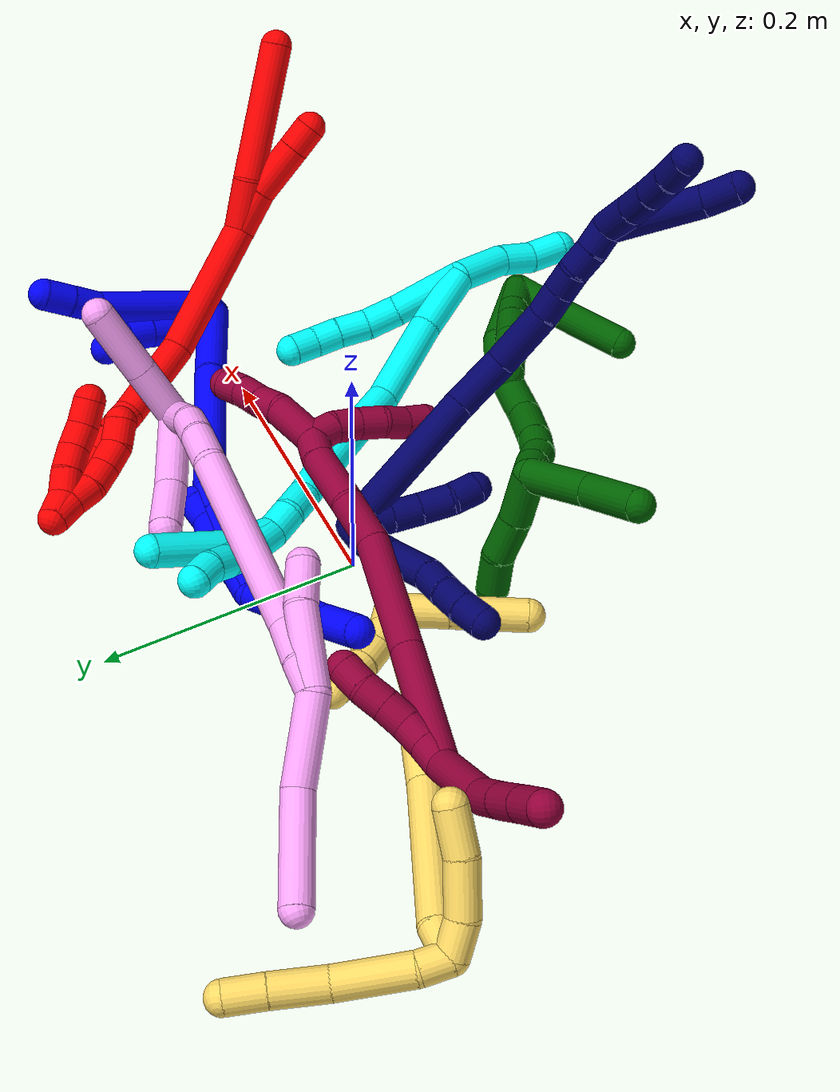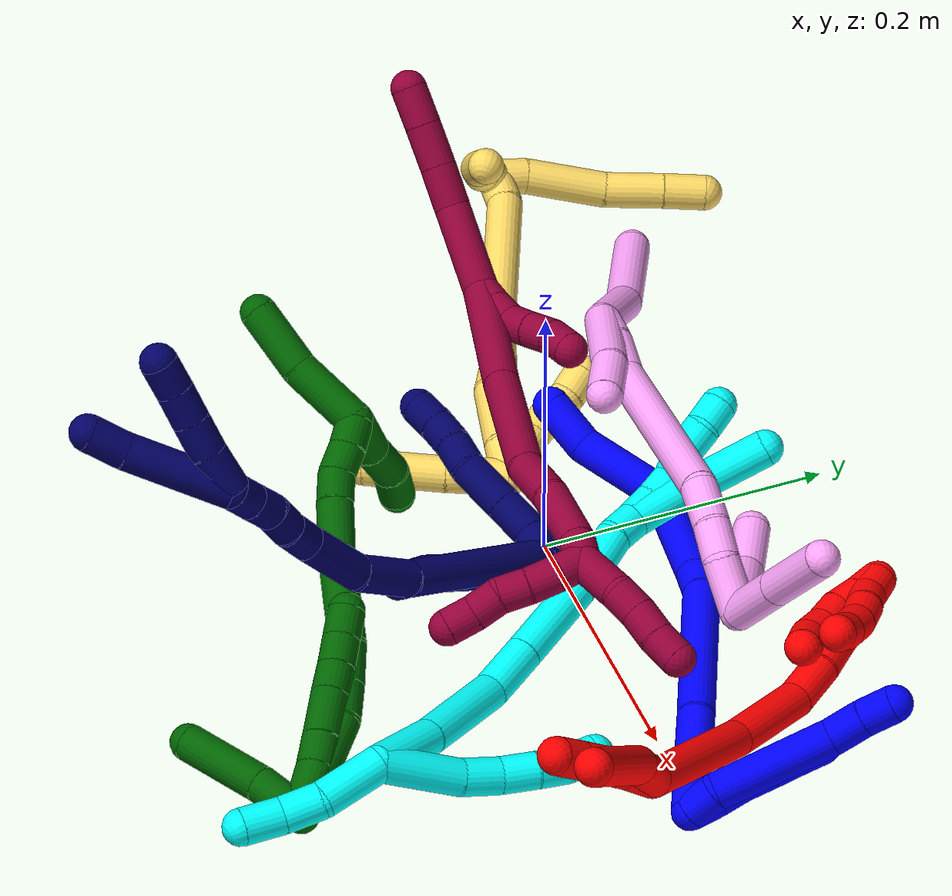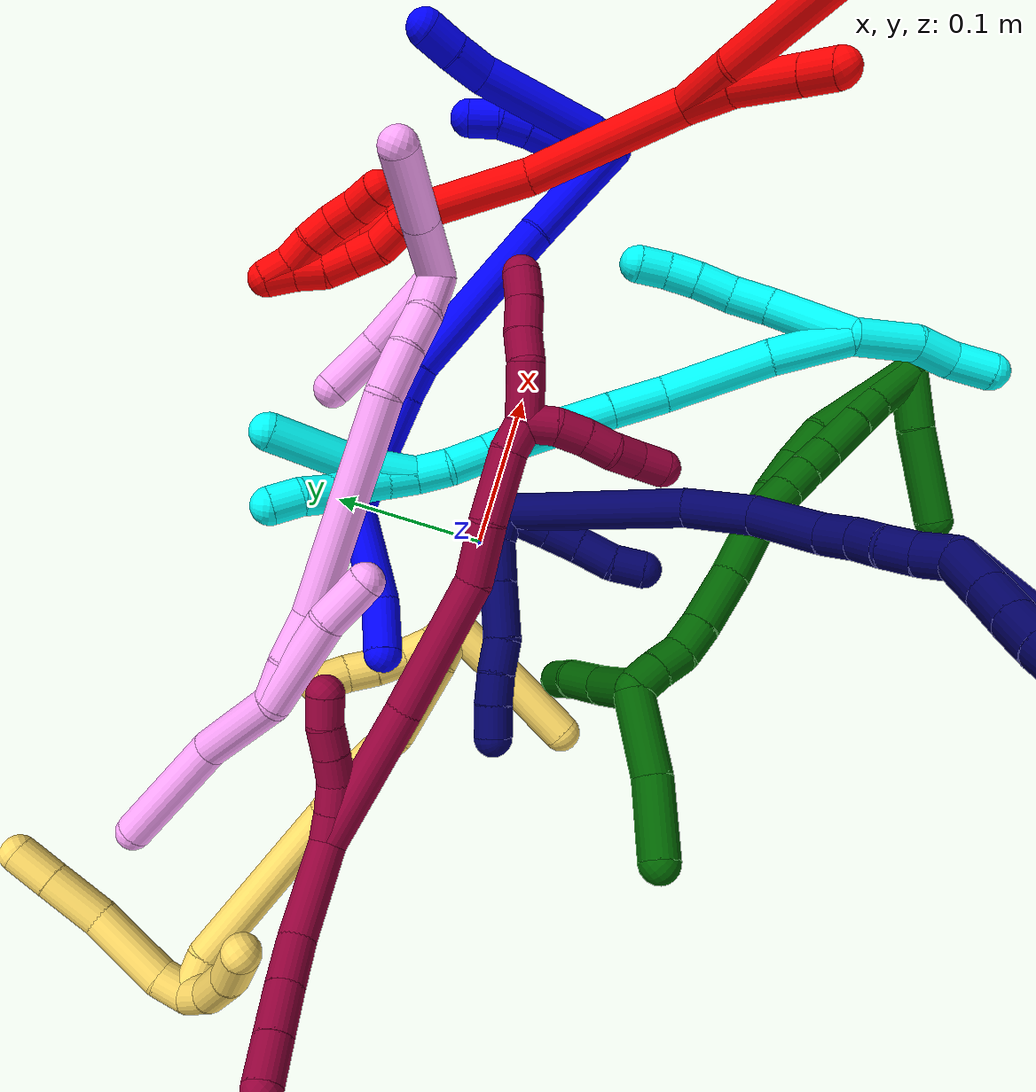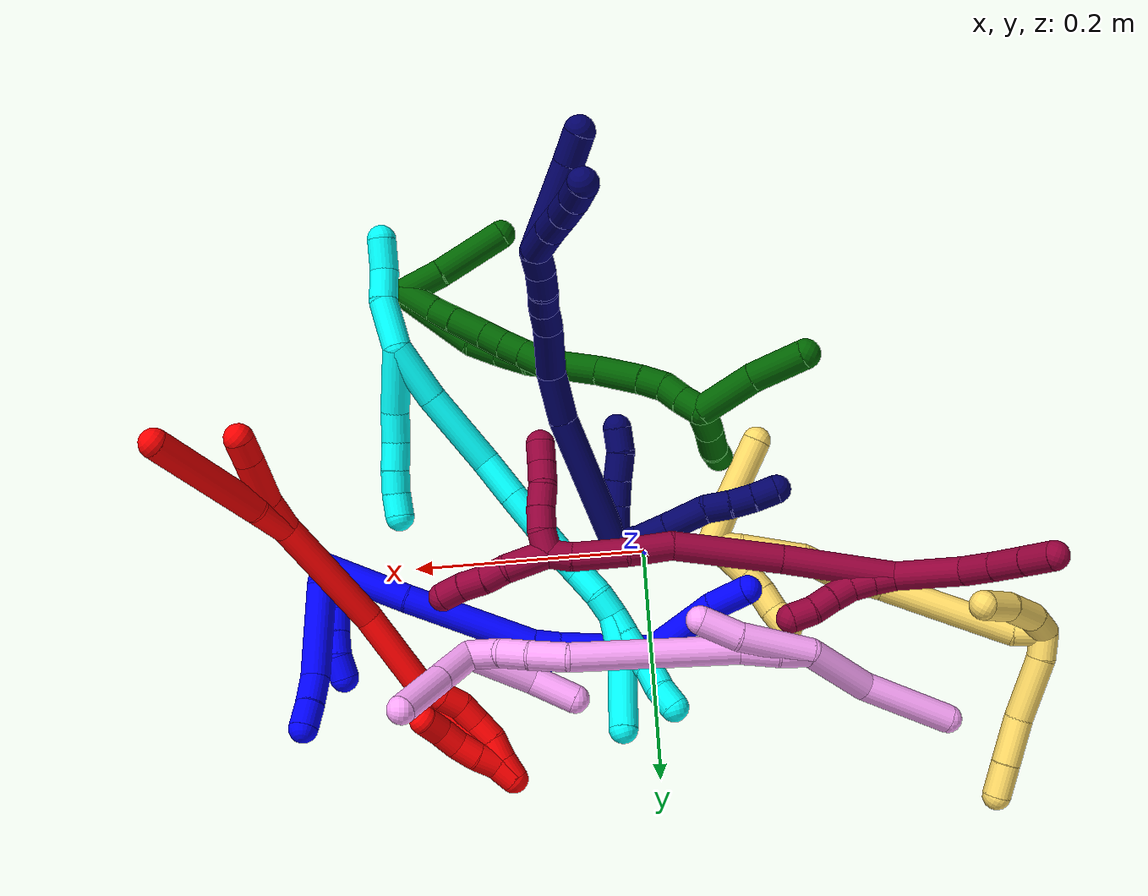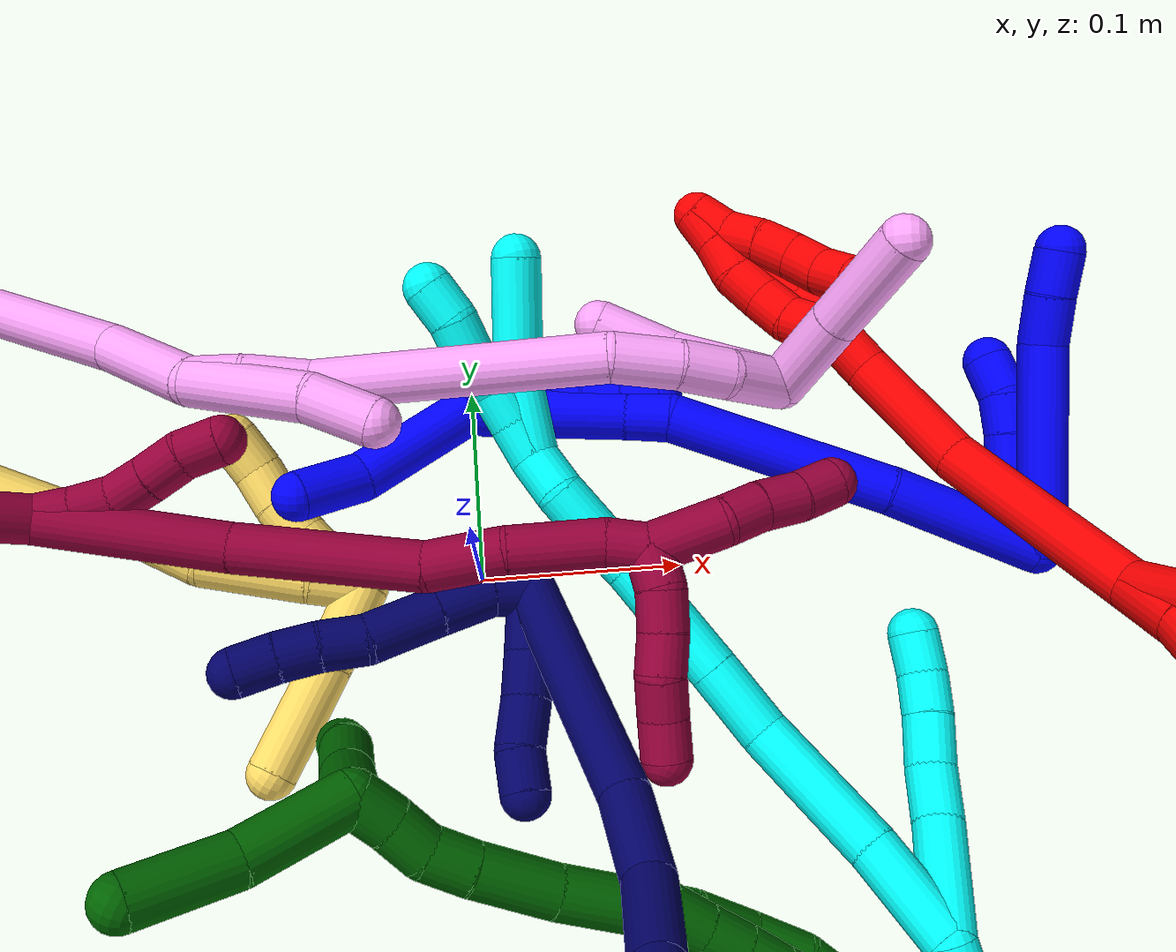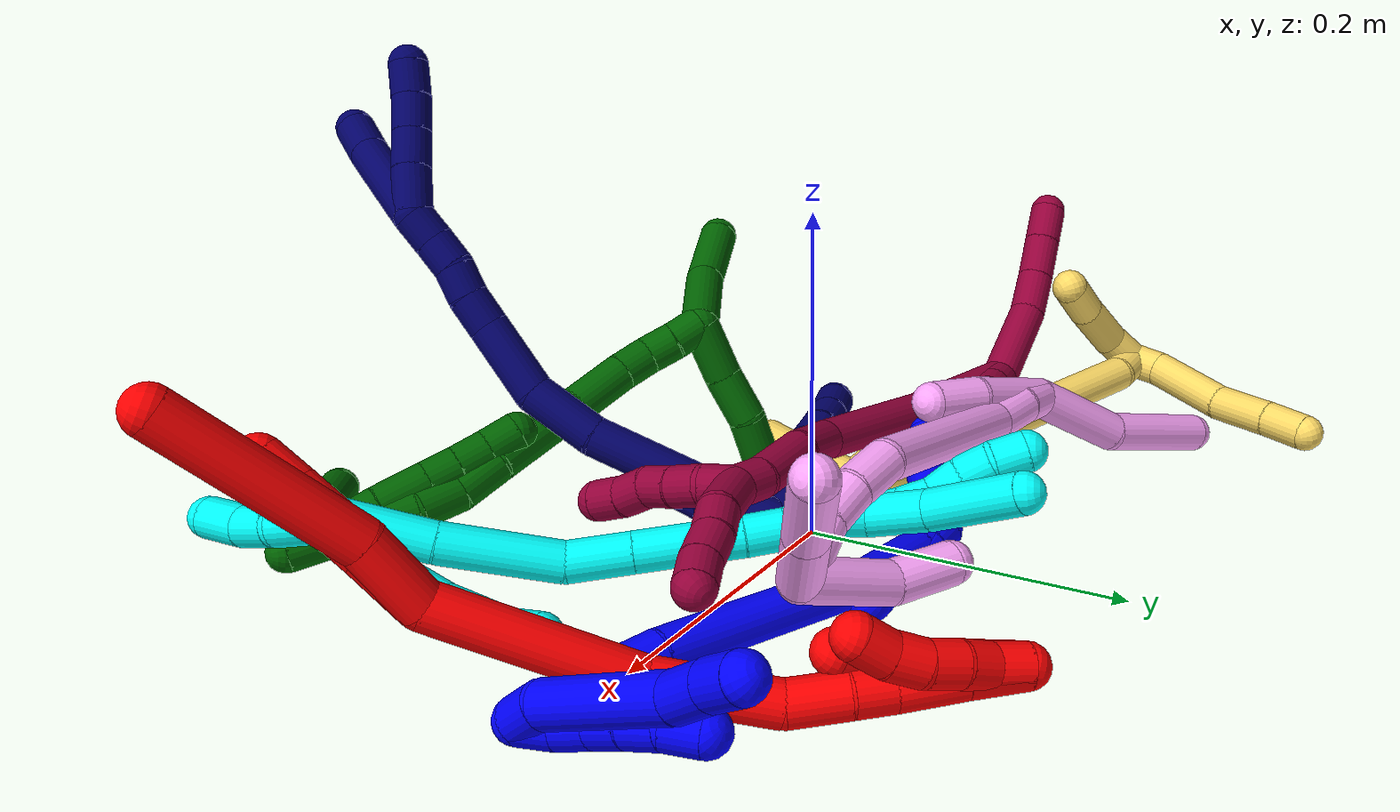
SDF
<sdf version="1.7">
 <world name="default">
  <plugin name="TubeGeneratorPlugin" filename="libtube_generator_plugin.so"/>
  <model name="photoneo_s_sensor">
   <static>1</static>
   <pose>0 0 2 1.57079 1.57079 3.14159</pose>
   <link name="link">
    <inertial><mass>0.1</mass></inertial>
    <sensor name="sensor" type="depth">
     <update_rate>30</update_rate>
     <camera>
      <horizontal_fov>1.22</horizontal_fov>
      <image><width>1920</width><height>1200</height><format>B8G8R8</format></image>
      <clip><near>0.1</near><far>4</far></clip>
      <depth_camera><output>points</output></depth_camera>
     </camera>
     <plugin name="camera_plugin" filename="libgazebo_ros_depth_camera.so">
      <baseline>0.2</baseline>
      <alwaysOn>1</alwaysOn>
      <updateRate>0.0</updateRate>
      <cameraName>camera_ir</cameraName>
      <imageTopicName>/camera/color/image_raw</imageTopicName>
      <cameraInfoTopicName>/camera/color/camera_info</cameraInfoTopicName>
      <depthImageTopicName>/camera/depth/image_raw</depthImageTopicName>
      <depthImageCameraInfoTopicName>/camera/depth/camera_info</depthImageCameraInfoTopicName>
      <pointCloudTopicName>/camera/depth/points</pointCloudTopicName>
      <frameName>fr_optical</frameName>
      <pointCloudCutoff>0.1</pointCloudCutoff>
      <pointCloudCutoffMax>2.0</pointCloudCutoffMax>
      <distortionK1>0</distortionK1>
      <distortionK2>0</distortionK2>
      <distortionK3>0</distortionK3>
      <distortionT1>0</distortionT1>
      <distortionT2>0</distortionT2>
      <CxPrime>0</CxPrime>
      <Cx>0</Cx>
      <Cy>0</Cy>
      <focalLength>0</focalLength>
      <hackBaseline>0</hackBaseline>
     </plugin>
    </sensor>
   </link>
  </model>
  <gravity>0 0 -9.8</gravity>
  <magnetic_field>6e-06 2.3e-05 -4.2e-05</magnetic_field>
  <atmosphere type="adiabatic"/>
  <physics name="default_physics" default="0" type="ode">
   <max_step_size>0.003</max_step_size>
   <real_time_factor>1</real_time_factor>
   <real_time_update_rate>1000</real_time_update_rate>
   <max_contacts>10000</max_contacts>
   <ode>
    <solver>
     <type>quick</type>
     <iters>100</iters>
     <sor>1.3</sor>
     <use_dynamic_moi_rescaling>0</use_dynamic_moi_rescaling>
    </solver>
    <constraints>
     <contact_max_correcting_vel>0</contact_max_correcting_vel>
     <contact_surface_layer>0.001</contact_surface_layer>
     <cfm>0</cfm>
     <erp>0.2</erp>
    </constraints>
   </ode>
  </physics>
  <scene><ambient>0.4 0.4 0.4 1</ambient><background>0.7 0.7 0.7 1</background><shadows>0</shadows></scene>
  <audio><device>default</device></audio>
  <spherical_coordinates>
   <surface_model>EARTH_WGS84</surface_model>
   <latitude_deg>0</latitude_deg>
   <longitude_deg>0</longitude_deg>
   <elevation>0</elevation>
   <heading_deg>0</heading_deg>
  </spherical_coordinates>
  <model name="bin">
   <static>1</static>
   <link name="bottom">
    <collision name="collision-bottom">
     <pose>0 0 -0.01 0 -0 0</pose>
     <geometry><box><size>0.8 0.6 0.02</size></box></geometry>
     <surface>
      <friction><ode><mu>100</mu><mu2>100</mu2></ode></friction>
      <contact><collide_bitmask>65535</collide_bitmask></contact>
     </surface>
    </collision>
   </link>
   <link name="west_wall">
    <collision name="collision-west_wall">
     <pose>-0.41 0 0.1 0 -0 0</pose>
     <geometry><box><size>0.02 0.6 0.2</size></box></geometry>
     <surface>
      <friction><ode><mu>100</mu><mu2>100</mu2></ode></friction>
      <contact><collide_bitmask>65535</collide_bitmask></contact>
     </surface>
    </collision>
   </link>
   <link name="east_wall">
    <collision name="collision-east_wall">
     <pose>0.41 0 0.1 0 -0 0</pose>
     <geometry><box><size>0.02 0.6 0.2</size></box></geometry>
     <surface>
      <friction><ode><mu>100</mu><mu2>100</mu2></ode></friction>
      <contact><collide_bitmask>65535</collide_bitmask></contact>
     </surface>
    </collision>
   </link>
   <link name="south_wall">
    <collision name="collision-south_wall">
     <pose>0 -0.31 0.1 0 -0 0</pose>
     <geometry><box><size>0.8 0.02 0.2</size></box></geometry>
     <surface>
      <friction><ode><mu>100</mu><mu2>100</mu2></ode></friction>
      <contact><collide_bitmask>65535</collide_bitmask></contact>
     </surface>
    </collision>
   </link>
   <link name="north_wall">
    <collision name="collision-north_wall">
     <pose>0 0.31 0.1 0 -0 0</pose>
     <geometry><box><size>0.8 0.02 0.2</size></box></geometry>
     <surface>
      <friction><ode><mu>100</mu><mu2>100</mu2></ode></friction>
      <contact><collide_bitmask>65535</collide_bitmask></contact>
     </surface>
    </collision>
   </link>
  </model>
  <model name="1">
   <static>0</static>
   <link name="1">
    <collision name="collision-cylinder-e_1_2_8">
     <pose>-2.2e-05 -0.000712 0.010663 0.066662 -0.002044 -6.8e-05</pose>
     <geometry><cylinder><radius>0.0125</radius><length>0.021373</length></cylinder></geometry>
     <surface>
      <friction><ode><mu>1.16</mu><mu2>1.16</mu2><slip1>0</slip1><slip2>0</slip2></ode></friction>
      <contact><ode><kp>1e+06</kp><kd>1</kd><max_vel>0</max_vel><min_depth>0.001</min_depth></ode></contact>
     </surface>
    </collision>
    <visual name="visual-cylinder-e_1_2_8">
     <pose>-2.2e-05 -0.000712 0.010663 0.066662 -0.002044 -6.8e-05</pose>
     <geometry><cylinder><radius>0.0125</radius><length>0.021373</length></cylinder></geometry>
     <material><ambient>0 0 1 1</ambient></material>
    </visual>
    <collision name="collision-cylinder-e_2_8_9">
     <pose>0.005551 0.008585 0.060712 -0.248848 0.13682 -0.017138</pose>
     <geometry><cylinder><radius>0.0125</radius><length>0.082044</length></cylinder></geometry>
     <surface>
      <friction><ode><mu>1.16</mu><mu2>1.16</mu2><slip1>0</slip1><slip2>0</slip2></ode></friction>
      <contact><ode><kp>1e+06</kp><kd>1</kd><max_vel>0</max_vel><min_depth>0.001</min_depth></ode></contact>
     </surface>
    </collision>
    <visual name="visual-cylinder-e_2_8_9">
     <pose>0.005551 0.008585 0.060712 -0.248848 0.13682 -0.017138</pose>
     <geometry><cylinder><radius>0.0125</radius><length>0.082044</length></cylinder></geometry>
     <material><ambient>0 0 1 1</ambient></material>
    </visual>
    <collision name="collision-cylinder-e_3_9_10">
     <pose>0.012414 0.01873 0.112392 -0.011045 0.102698 -0.000568</pose>
     <geometry><cylinder><radius>0.0125</radius><length>0.024717</length></cylinder></geometry>
     <surface>
      <friction><ode><mu>1.16</mu><mu2>1.16</mu2><slip1>0</slip1><slip2>0</slip2></ode></friction>
      <contact><ode><kp>1e+06</kp><kd>1</kd><max_vel>0</max_vel><min_depth>0.001</min_depth></ode></contact>
     </surface>
    </collision>
    <visual name="visual-cylinder-e_3_9_10">
     <pose>0.012414 0.01873 0.112392 -0.011045 0.102698 -0.000568</pose>
     <geometry><cylinder><radius>0.0125</radius><length>0.024717</length></cylinder></geometry>
     <material><ambient>0 0 1 1</ambient></material>
    </visual>
    <collision name="collision-cylinder-e_4_10_6">
     <pose>0.015833 0.019159 0.135399 -0.027346 0.198157 -0.002718</pose>
     <geometry><cylinder><radius>0.0125</radius><length>0.021866</length></cylinder></geometry>
     <surface>
      <friction><ode><mu>1.16</mu><mu2>1.16</mu2><slip1>0</slip1><slip2>0</slip2></ode></friction>
      <contact><ode><kp>1e+06</kp><kd>1</kd><max_vel>0</max_vel><min_depth>0.001</min_depth></ode></contact>
     </surface>
    </collision>
    <visual name="visual-cylinder-e_4_10_6">
     <pose>0.015833 0.019159 0.135399 -0.027346 0.198157 -0.002718</pose>
     <geometry><cylinder><radius>0.0125</radius><length>0.021866</length></cylinder></geometry>
     <material><ambient>0 0 1 1</ambient></material>
    </visual>
    <collision name="collision-cylinder-e_1_2_11">
     <pose>-0.000263 0.006347 0.007723 -0.687864 -0.026351 0.009439</pose>
     <geometry><cylinder><radius>0.0125</radius><length>0.02</length></cylinder></geometry>
     <surface>
      <friction><ode><mu>1.16</mu><mu2>1.16</mu2><slip1>0</slip1><slip2>0</slip2></ode></friction>
      <contact><ode><kp>1e+06</kp><kd>1</kd><max_vel>0</max_vel><min_depth>0.001</min_depth></ode></contact>
     </surface>
    </collision>
    <visual name="visual-cylinder-e_1_2_11">
     <pose>-0.000263 0.006347 0.007723 -0.687864 -0.026351 0.009439</pose>
     <geometry><cylinder><radius>0.0125</radius><length>0.02</length></cylinder></geometry>
     <material><ambient>0 0 1 1</ambient></material>
    </visual>
    <collision name="collision-cylinder-e_2_11_12">
     <pose>-0.000656 0.016773 0.024576 -0.420276 -0.012864 0.002744</pose>
     <geometry><cylinder><radius>0.0125</radius><length>0.02</length></cylinder></geometry>
     <surface>
      <friction><ode><mu>1.16</mu><mu2>1.16</mu2><slip1>0</slip1><slip2>0</slip2></ode></friction>
      <contact><ode><kp>1e+06</kp><kd>1</kd><max_vel>0</max_vel><min_depth>0.001</min_depth></ode></contact>
     </surface>
    </collision>
    <visual name="visual-cylinder-e_2_11_12">
     <pose>-0.000656 0.016773 0.024576 -0.420276 -0.012864 0.002744</pose>
     <geometry><cylinder><radius>0.0125</radius><length>0.02</length></cylinder></geometry>
     <material><ambient>0 0 1 1</ambient></material>
    </visual>
    <collision name="collision-cylinder-e_3_12_13">
     <pose>0.000445 0.0239 0.043149 -0.312112 0.123245 -0.019415</pose>
     <geometry><cylinder><radius>0.0125</radius><length>0.02</length></cylinder></geometry>
     <surface>
      <friction><ode><mu>1.16</mu><mu2>1.16</mu2><slip1>0</slip1><slip2>0</slip2></ode></friction>
      <contact><ode><kp>1e+06</kp><kd>1</kd><max_vel>0</max_vel><min_depth>0.001</min_depth></ode></contact>
     </surface>
    </collision>
    <visual name="visual-cylinder-e_3_12_13">
     <pose>0.000445 0.0239 0.043149 -0.312112 0.123245 -0.019415</pose>
     <geometry><cylinder><radius>0.0125</radius><length>0.02</length></cylinder></geometry>
     <material><ambient>0 0 1 1</ambient></material>
    </visual>
    <collision name="collision-cylinder-e_4_13_14">
     <pose>0.002455 0.030976 0.061714 -0.415908 0.078169 -0.016502</pose>
     <geometry><cylinder><radius>0.0125</radius><length>0.02</length></cylinder></geometry>
     <surface>
      <friction><ode><mu>1.16</mu><mu2>1.16</mu2><slip1>0</slip1><slip2>0</slip2></ode></friction>
      <contact><ode><kp>1e+06</kp><kd>1</kd><max_vel>0</max_vel><min_depth>0.001</min_depth></ode></contact>
     </surface>
    </collision>
    <visual name="visual-cylinder-e_4_13_14">
     <pose>0.002455 0.030976 0.061714 -0.415908 0.078169 -0.016502</pose>
     <geometry><cylinder><radius>0.0125</radius><length>0.02</length></cylinder></geometry>
     <material><ambient>0 0 1 1</ambient></material>
    </visual>
    <collision name="collision-cylinder-e_5_14_5">
     <pose>0.003254 0.041621 0.07833 -0.723205 0.001795 -0.000679</pose>
     <geometry><cylinder><radius>0.0125</radius><length>0.02</length></cylinder></geometry>
     <surface>
      <friction><ode><mu>1.16</mu><mu2>1.16</mu2><slip1>0</slip1><slip2>0</slip2></ode></friction>
      <contact><ode><kp>1e+06</kp><kd>1</kd><max_vel>0</max_vel><min_depth>0.001</min_depth></ode></contact>
     </surface>
    </collision>
    <visual name="visual-cylinder-e_5_14_5">
     <pose>0.003254 0.041621 0.07833 -0.723205 0.001795 -0.000679</pose>
     <geometry><cylinder><radius>0.0125</radius><length>0.02</length></cylinder></geometry>
     <material><ambient>0 0 1 1</ambient></material>
    </visual>
    <collision name="collision-cylinder-e_1_2_15">
     <pose>-0.030743 0.020169 0.014345 -0.952589 -0.892978 0.484273</pose>
     <geometry><cylinder><radius>0.0125</radius><length>0.078936</length></cylinder></geometry>
     <surface>
      <friction><ode><mu>1.16</mu><mu2>1.16</mu2><slip1>0</slip1><slip2>0</slip2></ode></friction>
      <contact><ode><kp>1e+06</kp><kd>1</kd><max_vel>0</max_vel><min_depth>0.001</min_depth></ode></contact>
     </surface>
    </collision>
    <visual name="visual-cylinder-e_1_2_15">
     <pose>-0.030743 0.020169 0.014345 -0.952589 -0.892978 0.484273</pose>
     <geometry><cylinder><radius>0.0125</radius><length>0.078936</length></cylinder></geometry>
     <material><ambient>0 0 1 1</ambient></material>
    </visual>
    <collision name="collision-cylinder-e_2_15_16">
     <pose>-0.104756 0.075348 0.044883 -1.13754 -0.84272 0.558065</pose>
     <geometry><cylinder><radius>0.0125</radius><length>0.115933</length></cylinder></geometry>
     <surface>
      <friction><ode><mu>1.16</mu><mu2>1.16</mu2><slip1>0</slip1><slip2>0</slip2></ode></friction>
      <contact><ode><kp>1e+06</kp><kd>1</kd><max_vel>0</max_vel><min_depth>0.001</min_depth></ode></contact>
     </surface>
    </collision>
    <visual name="visual-cylinder-e_2_15_16">
     <pose>-0.104756 0.075348 0.044883 -1.13754 -0.84272 0.558065</pose>
     <geometry><cylinder><radius>0.0125</radius><length>0.115933</length></cylinder></geometry>
     <material><ambient>0 0 1 1</ambient></material>
    </visual>
    <collision name="collision-cylinder-e_3_16_17">
     <pose>-0.157113 0.117488 0.061199 -1.55379 -0.90536 0.892055</pose>
     <geometry><cylinder><radius>0.0125</radius><length>0.023104</length></cylinder></geometry>
     <surface>
      <friction><ode><mu>1.16</mu><mu2>1.16</mu2><slip1>0</slip1><slip2>0</slip2></ode></friction>
      <contact><ode><kp>1e+06</kp><kd>1</kd><max_vel>0</max_vel><min_depth>0.001</min_depth></ode></contact>
     </surface>
    </collision>
    <visual name="visual-cylinder-e_3_16_17">
     <pose>-0.157113 0.117488 0.061199 -1.55379 -0.90536 0.892055</pose>
     <geometry><cylinder><radius>0.0125</radius><length>0.023104</length></cylinder></geometry>
     <material><ambient>0 0 1 1</ambient></material>
    </visual>
    <collision name="collision-cylinder-e_4_17_18">
     <pose>-0.189425 0.138305 0.061759 -1.53872 -1.03806 1.01065</pose>
     <geometry><cylinder><radius>0.0125</radius><length>0.053922</length></cylinder></geometry>
     <surface>
      <friction><ode><mu>1.16</mu><mu2>1.16</mu2><slip1>0</slip1><slip2>0</slip2></ode></friction>
      <contact><ode><kp>1e+06</kp><kd>1</kd><max_vel>0</max_vel><min_depth>0.001</min_depth></ode></contact>
     </surface>
    </collision>
    <visual name="visual-cylinder-e_4_17_18">
     <pose>-0.189425 0.138305 0.061759 -1.53872 -1.03806 1.01065</pose>
     <geometry><cylinder><radius>0.0125</radius><length>0.053922</length></cylinder></geometry>
     <material><ambient>0 0 1 1</ambient></material>
    </visual>
    <collision name="collision-cylinder-e_5_18_1">
     <pose>-0.225377 0.157911 0.062865 -1.45856 -1.13305 1.03373</pose>
     <geometry><cylinder><radius>0.0125</radius><length>0.028105</length></cylinder></geometry>
     <surface>
      <friction><ode><mu>1.16</mu><mu2>1.16</mu2><slip1>0</slip1><slip2>0</slip2></ode></friction>
      <contact><ode><kp>1e+06</kp><kd>1</kd><max_vel>0</max_vel><min_depth>0.001</min_depth></ode></contact>
     </surface>
    </collision>
    <visual name="visual-cylinder-e_5_18_1">
     <pose>-0.225377 0.157911 0.062865 -1.45856 -1.13305 1.03373</pose>
     <geometry><cylinder><radius>0.0125</radius><length>0.028105</length></cylinder></geometry>
     <material><ambient>0 0 1 1</ambient></material>
    </visual>
    <collision name="collision-cylinder-e_1_1_19">
     <pose>-0.228746 0.160312 0.063352 1.622 1.21079 1.25915</pose>
     <geometry><cylinder><radius>0.0125</radius><length>0.02</length></cylinder></geometry>
     <surface>
      <friction><ode><mu>1.16</mu><mu2>1.16</mu2><slip1>0</slip1><slip2>0</slip2></ode></friction>
      <contact><ode><kp>1e+06</kp><kd>1</kd><max_vel>0</max_vel><min_depth>0.001</min_depth></ode></contact>
     </surface>
    </collision>
    <visual name="visual-cylinder-e_1_1_19">
     <pose>-0.228746 0.160312 0.063352 1.622 1.21079 1.25915</pose>
     <geometry><cylinder><radius>0.0125</radius><length>0.02</length></cylinder></geometry>
     <material><ambient>0 0 1 1</ambient></material>
    </visual>
    <collision name="collision-cylinder-e_2_19_20">
     <pose>-0.209752 0.154128 0.062928 1.66195 1.29978 1.3887</pose>
     <geometry><cylinder><radius>0.0125</radius><length>0.02</length></cylinder></geometry>
     <surface>
      <friction><ode><mu>1.16</mu><mu2>1.16</mu2><slip1>0</slip1><slip2>0</slip2></ode></friction>
      <contact><ode><kp>1e+06</kp><kd>1</kd><max_vel>0</max_vel><min_depth>0.001</min_depth></ode></contact>
     </surface>
    </collision>
    <visual name="visual-cylinder-e_2_19_20">
     <pose>-0.209752 0.154128 0.062928 1.66195 1.29978 1.3887</pose>
     <geometry><cylinder><radius>0.0125</radius><length>0.02</length></cylinder></geometry>
     <material><ambient>0 0 1 1</ambient></material>
    </visual>
    <collision name="collision-cylinder-e_3_20_21">
     <pose>-0.191299 0.1472 0.064703 1.12843 1.07969 0.724914</pose>
     <geometry><cylinder><radius>0.0125</radius><length>0.02</length></cylinder></geometry>
     <surface>
      <friction><ode><mu>1.16</mu><mu2>1.16</mu2><slip1>0</slip1><slip2>0</slip2></ode></friction>
      <contact><ode><kp>1e+06</kp><kd>1</kd><max_vel>0</max_vel><min_depth>0.001</min_depth></ode></contact>
     </surface>
    </collision>
    <visual name="visual-cylinder-e_3_20_21">
     <pose>-0.191299 0.1472 0.064703 1.12843 1.07969 0.724914</pose>
     <geometry><cylinder><radius>0.0125</radius><length>0.02</length></cylinder></geometry>
     <material><ambient>0 0 1 1</ambient></material>
    </visual>
    <collision name="collision-cylinder-e_4_21_22">
     <pose>-0.173984 0.137728 0.065903 1.72669 1.01527 1.15347</pose>
     <geometry><cylinder><radius>0.0125</radius><length>0.02</length></cylinder></geometry>
     <surface>
      <friction><ode><mu>1.16</mu><mu2>1.16</mu2><slip1>0</slip1><slip2>0</slip2></ode></friction>
      <contact><ode><kp>1e+06</kp><kd>1</kd><max_vel>0</max_vel><min_depth>0.001</min_depth></ode></contact>
     </surface>
    </collision>
    <visual name="visual-cylinder-e_4_21_22">
     <pose>-0.173984 0.137728 0.065903 1.72669 1.01527 1.15347</pose>
     <geometry><cylinder><radius>0.0125</radius><length>0.02</length></cylinder></geometry>
     <material><ambient>0 0 1 1</ambient></material>
    </visual>
    <collision name="collision-cylinder-e_5_22_4">
     <pose>-0.156538 0.128547 0.067117 1.09772 1.10839 0.72363</pose>
     <geometry><cylinder><radius>0.0125</radius><length>0.02</length></cylinder></geometry>
     <surface>
      <friction><ode><mu>1.16</mu><mu2>1.16</mu2><slip1>0</slip1><slip2>0</slip2></ode></friction>
      <contact><ode><kp>1e+06</kp><kd>1</kd><max_vel>0</max_vel><min_depth>0.001</min_depth></ode></contact>
     </surface>
    </collision>
    <visual name="visual-cylinder-e_5_22_4">
     <pose>-0.156538 0.128547 0.067117 1.09772 1.10839 0.72363</pose>
     <geometry><cylinder><radius>0.0125</radius><length>0.02</length></cylinder></geometry>
     <material><ambient>0 0 1 1</ambient></material>
    </visual>
    <collision name="collision-cylinder-e_1_1_23">
     <pose>-0.267674 0.16221 0.051104 3.01201 -1.16987 -2.94627</pose>
     <geometry><cylinder><radius>0.0125</radius><length>0.064232</length></cylinder></geometry>
     <surface>
      <friction><ode><mu>1.16</mu><mu2>1.16</mu2><slip1>0</slip1><slip2>0</slip2></ode></friction>
      <contact><ode><kp>1e+06</kp><kd>1</kd><max_vel>0</max_vel><min_depth>0.001</min_depth></ode></contact>
     </surface>
    </collision>
    <visual name="visual-cylinder-e_1_1_23">
     <pose>-0.267674 0.16221 0.051104 3.01201 -1.16987 -2.94627</pose>
     <geometry><cylinder><radius>0.0125</radius><length>0.064232</length></cylinder></geometry>
     <material><ambient>0 0 1 1</ambient></material>
    </visual>
    <collision name="collision-cylinder-e_2_23_3">
     <pose>-0.31487 0.157868 0.037365 2.01917 -1.40104 -1.8603</pose>
     <geometry><cylinder><radius>0.0125</radius><length>0.035768</length></cylinder></geometry>
     <surface>
      <friction><ode><mu>1.16</mu><mu2>1.16</mu2><slip1>0</slip1><slip2>0</slip2></ode></friction>
      <contact><ode><kp>1e+06</kp><kd>1</kd><max_vel>0</max_vel><min_depth>0.001</min_depth></ode></contact>
     </surface>
    </collision>
    <visual name="visual-cylinder-e_2_23_3">
     <pose>-0.31487 0.157868 0.037365 2.01917 -1.40104 -1.8603</pose>
     <geometry><cylinder><radius>0.0125</radius><length>0.035768</length></cylinder></geometry>
     <material><ambient>0 0 1 1</ambient></material>
    </visual>
    <collision name="collision-sphere-3">
     <pose>-0.332497 0.155146 0.036056 0 -0 0</pose>
     <geometry><sphere><radius>0.0125</radius></sphere></geometry>
     <surface>
      <friction><ode><mu>1.16</mu><mu2>1.16</mu2><slip1>0</slip1><slip2>0</slip2></ode></friction>
      <contact><ode><kp>1e+06</kp><kd>1</kd><max_vel>0</max_vel><min_depth>0.001</min_depth></ode></contact>
     </surface>
    </collision>
    <visual name="visual-sphere-3">
     <pose>-0.332497 0.155146 0.036056 0 -0 0</pose>
     <geometry><sphere><radius>0.0125</radius></sphere></geometry>
     <material><ambient>0 0 1 1</ambient></material>
    </visual>
    <collision name="collision-sphere-23">
     <pose>-0.297243 0.160591 0.038675 0 -0 0</pose>
     <geometry><sphere><radius>0.0125</radius></sphere></geometry>
     <surface>
      <friction><ode><mu>1.16</mu><mu2>1.16</mu2><slip1>0</slip1><slip2>0</slip2></ode></friction>
      <contact><ode><kp>1e+06</kp><kd>1</kd><max_vel>0</max_vel><min_depth>0.001</min_depth></ode></contact>
     </surface>
    </collision>
    <visual name="visual-sphere-23">
     <pose>-0.297243 0.160591 0.038675 0 -0 0</pose>
     <geometry><sphere><radius>0.0125</radius></sphere></geometry>
     <material><ambient>0 0 1 1</ambient></material>
    </visual>
    <collision name="collision-sphere-4">
     <pose>-0.147588 0.124576 0.06915 0 -0 0</pose>
     <geometry><sphere><radius>0.0125</radius></sphere></geometry>
     <surface>
      <friction><ode><mu>1.16</mu><mu2>1.16</mu2><slip1>0</slip1><slip2>0</slip2></ode></friction>
      <contact><ode><kp>1e+06</kp><kd>1</kd><max_vel>0</max_vel><min_depth>0.001</min_depth></ode></contact>
     </surface>
    </collision>
    <visual name="visual-sphere-4">
     <pose>-0.147588 0.124576 0.06915 0 -0 0</pose>
     <geometry><sphere><radius>0.0125</radius></sphere></geometry>
     <material><ambient>0 0 1 1</ambient></material>
    </visual>
    <collision name="collision-sphere-22">
     <pose>-0.165488 0.132518 0.065085 0 -0 0</pose>
     <geometry><sphere><radius>0.0125</radius></sphere></geometry>
     <surface>
      <friction><ode><mu>1.16</mu><mu2>1.16</mu2><slip1>0</slip1><slip2>0</slip2></ode></friction>
      <contact><ode><kp>1e+06</kp><kd>1</kd><max_vel>0</max_vel><min_depth>0.001</min_depth></ode></contact>
     </surface>
    </collision>
    <visual name="visual-sphere-22">
     <pose>-0.165488 0.132518 0.065085 0 -0 0</pose>
     <geometry><sphere><radius>0.0125</radius></sphere></geometry>
     <material><ambient>0 0 1 1</ambient></material>
    </visual>
    <collision name="collision-sphere-21">
     <pose>-0.182481 0.142938 0.066722 0 -0 0</pose>
     <geometry><sphere><radius>0.0125</radius></sphere></geometry>
     <surface>
      <friction><ode><mu>1.16</mu><mu2>1.16</mu2><slip1>0</slip1><slip2>0</slip2></ode></friction>
      <contact><ode><kp>1e+06</kp><kd>1</kd><max_vel>0</max_vel><min_depth>0.001</min_depth></ode></contact>
     </surface>
    </collision>
    <visual name="visual-sphere-21">
     <pose>-0.182481 0.142938 0.066722 0 -0 0</pose>
     <geometry><sphere><radius>0.0125</radius></sphere></geometry>
     <material><ambient>0 0 1 1</ambient></material>
    </visual>
    <collision name="collision-sphere-20">
     <pose>-0.200117 0.151462 0.062685 0 -0 0</pose>
     <geometry><sphere><radius>0.0125</radius></sphere></geometry>
     <surface>
      <friction><ode><mu>1.16</mu><mu2>1.16</mu2><slip1>0</slip1><slip2>0</slip2></ode></friction>
      <contact><ode><kp>1e+06</kp><kd>1</kd><max_vel>0</max_vel><min_depth>0.001</min_depth></ode></contact>
     </surface>
    </collision>
    <visual name="visual-sphere-20">
     <pose>-0.200117 0.151462 0.062685 0 -0 0</pose>
     <geometry><sphere><radius>0.0125</radius></sphere></geometry>
     <material><ambient>0 0 1 1</ambient></material>
    </visual>
    <collision name="collision-sphere-11">
     <pose>-0.000527 0.012693 0.015447 0 -0 0</pose>
     <geometry><sphere><radius>0.0125</radius></sphere></geometry>
     <surface>
      <friction><ode><mu>1.16</mu><mu2>1.16</mu2><slip1>0</slip1><slip2>0</slip2></ode></friction>
      <contact><ode><kp>1e+06</kp><kd>1</kd><max_vel>0</max_vel><min_depth>0.001</min_depth></ode></contact>
     </surface>
    </collision>
    <visual name="visual-sphere-11">
     <pose>-0.000527 0.012693 0.015447 0 -0 0</pose>
     <geometry><sphere><radius>0.0125</radius></sphere></geometry>
     <material><ambient>0 0 1 1</ambient></material>
    </visual>
    <collision name="collision-sphere-6">
     <pose>0.017985 0.019452 0.146115 0 -0 0</pose>
     <geometry><sphere><radius>0.0125</radius></sphere></geometry>
     <surface>
      <friction><ode><mu>1.16</mu><mu2>1.16</mu2><slip1>0</slip1><slip2>0</slip2></ode></friction>
      <contact><ode><kp>1e+06</kp><kd>1</kd><max_vel>0</max_vel><min_depth>0.001</min_depth></ode></contact>
     </surface>
    </collision>
    <visual name="visual-sphere-6">
     <pose>0.017985 0.019452 0.146115 0 -0 0</pose>
     <geometry><sphere><radius>0.0125</radius></sphere></geometry>
     <material><ambient>0 0 1 1</ambient></material>
    </visual>
    <collision name="collision-sphere-10">
     <pose>0.013681 0.018865 0.124684 0 -0 0</pose>
     <geometry><sphere><radius>0.0125</radius></sphere></geometry>
     <surface>
      <friction><ode><mu>1.16</mu><mu2>1.16</mu2><slip1>0</slip1><slip2>0</slip2></ode></friction>
      <contact><ode><kp>1e+06</kp><kd>1</kd><max_vel>0</max_vel><min_depth>0.001</min_depth></ode></contact>
     </surface>
    </collision>
    <visual name="visual-sphere-10">
     <pose>0.013681 0.018865 0.124684 0 -0 0</pose>
     <geometry><sphere><radius>0.0125</radius></sphere></geometry>
     <material><ambient>0 0 1 1</ambient></material>
    </visual>
    <collision name="collision-sphere-9">
     <pose>0.011147 0.018594 0.100099 0 -0 0</pose>
     <geometry><sphere><radius>0.0125</radius></sphere></geometry>
     <surface>
      <friction><ode><mu>1.16</mu><mu2>1.16</mu2><slip1>0</slip1><slip2>0</slip2></ode></friction>
      <contact><ode><kp>1e+06</kp><kd>1</kd><max_vel>0</max_vel><min_depth>0.001</min_depth></ode></contact>
     </surface>
    </collision>
    <visual name="visual-sphere-9">
     <pose>0.011147 0.018594 0.100099 0 -0 0</pose>
     <geometry><sphere><radius>0.0125</radius></sphere></geometry>
     <material><ambient>0 0 1 1</ambient></material>
    </visual>
    <collision name="collision-sphere-2">
     <geometry><sphere><radius>0.0125</radius></sphere></geometry>
     <surface>
      <friction><ode><mu>1.16</mu><mu2>1.16</mu2><slip1>0</slip1><slip2>0</slip2></ode></friction>
      <contact><ode><kp>1e+06</kp><kd>1</kd><max_vel>0</max_vel><min_depth>0.001</min_depth></ode></contact>
     </surface>
    </collision>
    <visual name="visual-sphere-2">
     <geometry><sphere><radius>0.0125</radius></sphere></geometry>
     <material><ambient>0 0 1 1</ambient></material>
    </visual>
    <collision name="collision-sphere-19">
     <pose>-0.219387 0.156794 0.063172 0 -0 0</pose>
     <geometry><sphere><radius>0.0125</radius></sphere></geometry>
     <surface>
      <friction><ode><mu>1.16</mu><mu2>1.16</mu2><slip1>0</slip1><slip2>0</slip2></ode></friction>
      <contact><ode><kp>1e+06</kp><kd>1</kd><max_vel>0</max_vel><min_depth>0.001</min_depth></ode></contact>
     </surface>
    </collision>
    <visual name="visual-sphere-19">
     <pose>-0.219387 0.156794 0.063172 0 -0 0</pose>
     <geometry><sphere><radius>0.0125</radius></sphere></geometry>
     <material><ambient>0 0 1 1</ambient></material>
    </visual>
    <collision name="collision-sphere-8">
     <pose>-4.4e-05 -0.001424 0.021325 0 -0 0</pose>
     <geometry><sphere><radius>0.0125</radius></sphere></geometry>
     <surface>
      <friction><ode><mu>1.16</mu><mu2>1.16</mu2><slip1>0</slip1><slip2>0</slip2></ode></friction>
      <contact><ode><kp>1e+06</kp><kd>1</kd><max_vel>0</max_vel><min_depth>0.001</min_depth></ode></contact>
     </surface>
    </collision>
    <visual name="visual-sphere-8">
     <pose>-4.4e-05 -0.001424 0.021325 0 -0 0</pose>
     <geometry><sphere><radius>0.0125</radius></sphere></geometry>
     <material><ambient>0 0 1 1</ambient></material>
    </visual>
    <collision name="collision-sphere-12">
     <pose>-0.000784 0.020853 0.033705 0 -0 0</pose>
     <geometry><sphere><radius>0.0125</radius></sphere></geometry>
     <surface>
      <friction><ode><mu>1.16</mu><mu2>1.16</mu2><slip1>0</slip1><slip2>0</slip2></ode></friction>
      <contact><ode><kp>1e+06</kp><kd>1</kd><max_vel>0</max_vel><min_depth>0.001</min_depth></ode></contact>
     </surface>
    </collision>
    <visual name="visual-sphere-12">
     <pose>-0.000784 0.020853 0.033705 0 -0 0</pose>
     <geometry><sphere><radius>0.0125</radius></sphere></geometry>
     <material><ambient>0 0 1 1</ambient></material>
    </visual>
    <collision name="collision-sphere-13">
     <pose>0.001674 0.026948 0.052594 0 -0 0</pose>
     <geometry><sphere><radius>0.0125</radius></sphere></geometry>
     <surface>
      <friction><ode><mu>1.16</mu><mu2>1.16</mu2><slip1>0</slip1><slip2>0</slip2></ode></friction>
      <contact><ode><kp>1e+06</kp><kd>1</kd><max_vel>0</max_vel><min_depth>0.001</min_depth></ode></contact>
     </surface>
    </collision>
    <visual name="visual-sphere-13">
     <pose>0.001674 0.026948 0.052594 0 -0 0</pose>
     <geometry><sphere><radius>0.0125</radius></sphere></geometry>
     <material><ambient>0 0 1 1</ambient></material>
    </visual>
    <collision name="collision-sphere-14">
     <pose>0.003236 0.035003 0.070833 0 -0 0</pose>
     <geometry><sphere><radius>0.0125</radius></sphere></geometry>
     <surface>
      <friction><ode><mu>1.16</mu><mu2>1.16</mu2><slip1>0</slip1><slip2>0</slip2></ode></friction>
      <contact><ode><kp>1e+06</kp><kd>1</kd><max_vel>0</max_vel><min_depth>0.001</min_depth></ode></contact>
     </surface>
    </collision>
    <visual name="visual-sphere-14">
     <pose>0.003236 0.035003 0.070833 0 -0 0</pose>
     <geometry><sphere><radius>0.0125</radius></sphere></geometry>
     <material><ambient>0 0 1 1</ambient></material>
    </visual>
    <collision name="collision-sphere-5">
     <pose>0.003272 0.048239 0.085827 0 -0 0</pose>
     <geometry><sphere><radius>0.0125</radius></sphere></geometry>
     <surface>
      <friction><ode><mu>1.16</mu><mu2>1.16</mu2><slip1>0</slip1><slip2>0</slip2></ode></friction>
      <contact><ode><kp>1e+06</kp><kd>1</kd><max_vel>0</max_vel><min_depth>0.001</min_depth></ode></contact>
     </surface>
    </collision>
    <visual name="visual-sphere-5">
     <pose>0.003272 0.048239 0.085827 0 -0 0</pose>
     <geometry><sphere><radius>0.0125</radius></sphere></geometry>
     <material><ambient>0 0 1 1</ambient></material>
    </visual>
    <collision name="collision-sphere-15">
     <pose>-0.061487 0.040339 0.028689 0 -0 0</pose>
     <geometry><sphere><radius>0.0125</radius></sphere></geometry>
     <surface>
      <friction><ode><mu>1.16</mu><mu2>1.16</mu2><slip1>0</slip1><slip2>0</slip2></ode></friction>
      <contact><ode><kp>1e+06</kp><kd>1</kd><max_vel>0</max_vel><min_depth>0.001</min_depth></ode></contact>
     </surface>
    </collision>
    <visual name="visual-sphere-15">
     <pose>-0.061487 0.040339 0.028689 0 -0 0</pose>
     <geometry><sphere><radius>0.0125</radius></sphere></geometry>
     <material><ambient>0 0 1 1</ambient></material>
    </visual>
    <collision name="collision-sphere-16">
     <pose>-0.148025 0.110356 0.061077 0 -0 0</pose>
     <geometry><sphere><radius>0.0125</radius></sphere></geometry>
     <surface>
      <friction><ode><mu>1.16</mu><mu2>1.16</mu2><slip1>0</slip1><slip2>0</slip2></ode></friction>
      <contact><ode><kp>1e+06</kp><kd>1</kd><max_vel>0</max_vel><min_depth>0.001</min_depth></ode></contact>
     </surface>
    </collision>
    <visual name="visual-sphere-16">
     <pose>-0.148025 0.110356 0.061077 0 -0 0</pose>
     <geometry><sphere><radius>0.0125</radius></sphere></geometry>
     <material><ambient>0 0 1 1</ambient></material>
    </visual>
    <collision name="collision-sphere-17">
     <pose>-0.1662 0.124619 0.06132 0 -0 0</pose>
     <geometry><sphere><radius>0.0125</radius></sphere></geometry>
     <surface>
      <friction><ode><mu>1.16</mu><mu2>1.16</mu2><slip1>0</slip1><slip2>0</slip2></ode></friction>
      <contact><ode><kp>1e+06</kp><kd>1</kd><max_vel>0</max_vel><min_depth>0.001</min_depth></ode></contact>
     </surface>
    </collision>
    <visual name="visual-sphere-17">
     <pose>-0.1662 0.124619 0.06132 0 -0 0</pose>
     <geometry><sphere><radius>0.0125</radius></sphere></geometry>
     <material><ambient>0 0 1 1</ambient></material>
    </visual>
    <collision name="collision-sphere-18">
     <pose>-0.21265 0.151991 0.062198 0 -0 0</pose>
     <geometry><sphere><radius>0.0125</radius></sphere></geometry>
     <surface>
      <friction><ode><mu>1.16</mu><mu2>1.16</mu2><slip1>0</slip1><slip2>0</slip2></ode></friction>
      <contact><ode><kp>1e+06</kp><kd>1</kd><max_vel>0</max_vel><min_depth>0.001</min_depth></ode></contact>
     </surface>
    </collision>
    <visual name="visual-sphere-18">
     <pose>-0.21265 0.151991 0.062198 0 -0 0</pose>
     <geometry><sphere><radius>0.0125</radius></sphere></geometry>
     <material><ambient>0 0 1 1</ambient></material>
    </visual>
    <collision name="collision-sphere-1">
     <pose>-0.238105 0.16383 0.063533 0 -0 0</pose>
     <geometry><sphere><radius>0.0125</radius></sphere></geometry>
     <surface>
      <friction><ode><mu>1.16</mu><mu2>1.16</mu2><slip1>0</slip1><slip2>0</slip2></ode></friction>
      <contact><ode><kp>1e+06</kp><kd>1</kd><max_vel>0</max_vel><min_depth>0.001</min_depth></ode></contact>
     </surface>
    </collision>
    <visual name="visual-sphere-1">
     <pose>-0.238105 0.16383 0.063533 0 -0 0</pose>
     <geometry><sphere><radius>0.0125</radius></sphere></geometry>
     <material><ambient>0 0 1 1</ambient></material>
    </visual>
    <inertial>
     <pose>-0.108265 0.079367 0.052271 0 -0 0</pose>
     <mass>0.75</mass>
     <inertia><ixx>0.00021</ixx><ixy>0</ixy><ixz>0</ixz><iyy>0.000324</iyy><iyz>0</iyz><izz>6.3e-05</izz></inertia>
    </inertial>
   </link>
   <pose>0.278383 -0.008836 0.011417 -0.890684 0.378031 0.219576</pose>
  </model>
  <model name="2">
   <static>0</static>
   <link name="2">
    <collision name="collision-cylinder-e_1_2_8">
     <pose>-0.007889 0.006279 0.018081 -0.334264 -0.390944 0.066783</pose>
     <geometry><cylinder><radius>0.0125</radius><length>0.041405</length></cylinder></geometry>
     <surface>
      <friction><ode><mu>1.16</mu><mu2>1.16</mu2><slip1>0</slip1><slip2>0</slip2></ode></friction>
      <contact><ode><kp>1e+06</kp><kd>1</kd><max_vel>0</max_vel><min_depth>0.001</min_depth></ode></contact>
     </surface>
    </collision>
    <visual name="visual-cylinder-e_1_2_8">
     <pose>-0.007889 0.006279 0.018081 -0.334264 -0.390944 0.066783</pose>
     <geometry><cylinder><radius>0.0125</radius><length>0.041405</length></cylinder></geometry>
     <material><ambient>1 0 0 1</ambient></material>
    </visual>
    <collision name="collision-cylinder-e_2_8_6">
     <pose>-0.025904 0.024515 0.08815 -0.226039 -0.187599 0.021355</pose>
     <geometry><cylinder><radius>0.0125</radius><length>0.108595</length></cylinder></geometry>
     <surface>
      <friction><ode><mu>1.16</mu><mu2>1.16</mu2><slip1>0</slip1><slip2>0</slip2></ode></friction>
      <contact><ode><kp>1e+06</kp><kd>1</kd><max_vel>0</max_vel><min_depth>0.001</min_depth></ode></contact>
     </surface>
    </collision>
    <visual name="visual-cylinder-e_2_8_6">
     <pose>-0.025904 0.024515 0.08815 -0.226039 -0.187599 0.021355</pose>
     <geometry><cylinder><radius>0.0125</radius><length>0.108595</length></cylinder></geometry>
     <material><ambient>1 0 0 1</ambient></material>
    </visual>
    <collision name="collision-cylinder-e_1_2_9">
     <pose>-0.007754 0.000157 0.015743 -0.00999 -0.457651 0.002327</pose>
     <geometry><cylinder><radius>0.0125</radius><length>0.0351</length></cylinder></geometry>
     <surface>
      <friction><ode><mu>1.16</mu><mu2>1.16</mu2><slip1>0</slip1><slip2>0</slip2></ode></friction>
      <contact><ode><kp>1e+06</kp><kd>1</kd><max_vel>0</max_vel><min_depth>0.001</min_depth></ode></contact>
     </surface>
    </collision>
    <visual name="visual-cylinder-e_1_2_9">
     <pose>-0.007754 0.000157 0.015743 -0.00999 -0.457651 0.002327</pose>
     <geometry><cylinder><radius>0.0125</radius><length>0.0351</length></cylinder></geometry>
     <material><ambient>1 0 0 1</ambient></material>
    </visual>
    <collision name="collision-cylinder-e_2_9_10">
     <pose>-0.025437 -0.003348 0.050407 0.191234 -0.475718 -0.046498</pose>
     <geometry><cylinder><radius>0.0125</radius><length>0.043358</length></cylinder></geometry>
     <surface>
      <friction><ode><mu>1.16</mu><mu2>1.16</mu2><slip1>0</slip1><slip2>0</slip2></ode></friction>
      <contact><ode><kp>1e+06</kp><kd>1</kd><max_vel>0</max_vel><min_depth>0.001</min_depth></ode></contact>
     </surface>
    </collision>
    <visual name="visual-cylinder-e_2_9_10">
     <pose>-0.025437 -0.003348 0.050407 0.191234 -0.475718 -0.046498</pose>
     <geometry><cylinder><radius>0.0125</radius><length>0.043358</length></cylinder></geometry>
     <material><ambient>1 0 0 1</ambient></material>
    </visual>
    <collision name="collision-cylinder-e_3_10_5">
     <pose>-0.040139 -0.008804 0.078815 0.186784 -0.459133 -0.043769</pose>
     <geometry><cylinder><radius>0.0125</radius><length>0.021542</length></cylinder></geometry>
     <surface>
      <friction><ode><mu>1.16</mu><mu2>1.16</mu2><slip1>0</slip1><slip2>0</slip2></ode></friction>
      <contact><ode><kp>1e+06</kp><kd>1</kd><max_vel>0</max_vel><min_depth>0.001</min_depth></ode></contact>
     </surface>
    </collision>
    <visual name="visual-cylinder-e_3_10_5">
     <pose>-0.040139 -0.008804 0.078815 0.186784 -0.459133 -0.043769</pose>
     <geometry><cylinder><radius>0.0125</radius><length>0.021542</length></cylinder></geometry>
     <material><ambient>1 0 0 1</ambient></material>
    </visual>
    <collision name="collision-cylinder-e_1_2_11">
     <pose>0.003623 0.006092 -0.054379 -3.03002 0.066113 -1.06928</pose>
     <geometry><cylinder><radius>0.0125</radius><length>0.109678</length></cylinder></geometry>
     <surface>
      <friction><ode><mu>1.16</mu><mu2>1.16</mu2><slip1>0</slip1><slip2>0</slip2></ode></friction>
      <contact><ode><kp>1e+06</kp><kd>1</kd><max_vel>0</max_vel><min_depth>0.001</min_depth></ode></contact>
     </surface>
    </collision>
    <visual name="visual-cylinder-e_1_2_11">
     <pose>0.003623 0.006092 -0.054379 -3.03002 0.066113 -1.06928</pose>
     <geometry><cylinder><radius>0.0125</radius><length>0.109678</length></cylinder></geometry>
     <material><ambient>1 0 0 1</ambient></material>
    </visual>
    <collision name="collision-cylinder-e_2_11_12">
     <pose>0.005631 0.022044 -0.141027 -2.84507 -0.04781 0.317472</pose>
     <geometry><cylinder><radius>0.0125</radius><length>0.067559</length></cylinder></geometry>
     <surface>
      <friction><ode><mu>1.16</mu><mu2>1.16</mu2><slip1>0</slip1><slip2>0</slip2></ode></friction>
      <contact><ode><kp>1e+06</kp><kd>1</kd><max_vel>0</max_vel><min_depth>0.001</min_depth></ode></contact>
     </surface>
    </collision>
    <visual name="visual-cylinder-e_2_11_12">
     <pose>0.005631 0.022044 -0.141027 -2.84507 -0.04781 0.317472</pose>
     <geometry><cylinder><radius>0.0125</radius><length>0.067559</length></cylinder></geometry>
     <material><ambient>1 0 0 1</ambient></material>
    </visual>
    <collision name="collision-cylinder-e_3_12_13">
     <pose>-0.001177 0.038362 -0.187176 -2.70607 -0.327081 1.28157</pose>
     <geometry><cylinder><radius>0.0125</radius><length>0.032334</length></cylinder></geometry>
     <surface>
      <friction><ode><mu>1.16</mu><mu2>1.16</mu2><slip1>0</slip1><slip2>0</slip2></ode></friction>
      <contact><ode><kp>1e+06</kp><kd>1</kd><max_vel>0</max_vel><min_depth>0.001</min_depth></ode></contact>
     </surface>
    </collision>
    <visual name="visual-cylinder-e_3_12_13">
     <pose>-0.001177 0.038362 -0.187176 -2.70607 -0.327081 1.28157</pose>
     <geometry><cylinder><radius>0.0125</radius><length>0.032334</length></cylinder></geometry>
     <material><ambient>1 0 0 1</ambient></material>
    </visual>
    <collision name="collision-cylinder-e_4_13_14">
     <pose>-0.010185 0.04758 -0.210812 -2.86597 -0.359785 1.83853</pose>
     <geometry><cylinder><radius>0.0125</radius><length>0.021664</length></cylinder></geometry>
     <surface>
      <friction><ode><mu>1.16</mu><mu2>1.16</mu2><slip1>0</slip1><slip2>0</slip2></ode></friction>
      <contact><ode><kp>1e+06</kp><kd>1</kd><max_vel>0</max_vel><min_depth>0.001</min_depth></ode></contact>
     </surface>
    </collision>
    <visual name="visual-cylinder-e_4_13_14">
     <pose>-0.010185 0.04758 -0.210812 -2.86597 -0.359785 1.83853</pose>
     <geometry><cylinder><radius>0.0125</radius><length>0.021664</length></cylinder></geometry>
     <material><ambient>1 0 0 1</ambient></material>
    </visual>
    <collision name="collision-cylinder-e_5_14_15">
     <pose>-0.020662 0.056408 -0.236239 -2.77211 -0.377513 1.59279</pose>
     <geometry><cylinder><radius>0.0125</radius><length>0.036158</length></cylinder></geometry>
     <surface>
      <friction><ode><mu>1.16</mu><mu2>1.16</mu2><slip1>0</slip1><slip2>0</slip2></ode></friction>
      <contact><ode><kp>1e+06</kp><kd>1</kd><max_vel>0</max_vel><min_depth>0.001</min_depth></ode></contact>
     </surface>
    </collision>
    <visual name="visual-cylinder-e_5_14_15">
     <pose>-0.020662 0.056408 -0.236239 -2.77211 -0.377513 1.59279</pose>
     <geometry><cylinder><radius>0.0125</radius><length>0.036158</length></cylinder></geometry>
     <material><ambient>1 0 0 1</ambient></material>
    </visual>
    <collision name="collision-cylinder-e_6_15_1">
     <pose>-0.033124 0.066798 -0.266524 -2.85407 -0.363549 1.80736</pose>
     <geometry><cylinder><radius>0.0125</radius><length>0.032608</length></cylinder></geometry>
     <surface>
      <friction><ode><mu>1.16</mu><mu2>1.16</mu2><slip1>0</slip1><slip2>0</slip2></ode></friction>
      <contact><ode><kp>1e+06</kp><kd>1</kd><max_vel>0</max_vel><min_depth>0.001</min_depth></ode></contact>
     </surface>
    </collision>
    <visual name="visual-cylinder-e_6_15_1">
     <pose>-0.033124 0.066798 -0.266524 -2.85407 -0.363549 1.80736</pose>
     <geometry><cylinder><radius>0.0125</radius><length>0.032608</length></cylinder></geometry>
     <material><ambient>1 0 0 1</ambient></material>
    </visual>
    <collision name="collision-cylinder-e_1_1_16">
     <pose>-0.036362 0.069656 -0.271581 0.151926 0.25883 0.01981</pose>
     <geometry><cylinder><radius>0.0125</radius><length>0.02</length></cylinder></geometry>
     <surface>
      <friction><ode><mu>1.16</mu><mu2>1.16</mu2><slip1>0</slip1><slip2>0</slip2></ode></friction>
      <contact><ode><kp>1e+06</kp><kd>1</kd><max_vel>0</max_vel><min_depth>0.001</min_depth></ode></contact>
     </surface>
    </collision>
    <visual name="visual-cylinder-e_1_1_16">
     <pose>-0.036362 0.069656 -0.271581 0.151926 0.25883 0.01981</pose>
     <geometry><cylinder><radius>0.0125</radius><length>0.02</length></cylinder></geometry>
     <material><ambient>1 0 0 1</ambient></material>
    </visual>
    <collision name="collision-cylinder-e_2_16_17">
     <pose>-0.031422 0.069879 -0.25246 -0.174402 0.240345 -0.021113</pose>
     <geometry><cylinder><radius>0.0125</radius><length>0.02</length></cylinder></geometry>
     <surface>
      <friction><ode><mu>1.16</mu><mu2>1.16</mu2><slip1>0</slip1><slip2>0</slip2></ode></friction>
      <contact><ode><kp>1e+06</kp><kd>1</kd><max_vel>0</max_vel><min_depth>0.001</min_depth></ode></contact>
     </surface>
    </collision>
    <visual name="visual-cylinder-e_2_16_17">
     <pose>-0.031422 0.069879 -0.25246 -0.174402 0.240345 -0.021113</pose>
     <geometry><cylinder><radius>0.0125</radius><length>0.02</length></cylinder></geometry>
     <material><ambient>1 0 0 1</ambient></material>
    </visual>
    <collision name="collision-cylinder-e_3_17_18">
     <pose>-0.026455 0.071578 -0.233235 -0.001459 0.261636 -0.000192</pose>
     <geometry><cylinder><radius>0.0125</radius><length>0.02</length></cylinder></geometry>
     <surface>
      <friction><ode><mu>1.16</mu><mu2>1.16</mu2><slip1>0</slip1><slip2>0</slip2></ode></friction>
      <contact><ode><kp>1e+06</kp><kd>1</kd><max_vel>0</max_vel><min_depth>0.001</min_depth></ode></contact>
     </surface>
    </collision>
    <visual name="visual-cylinder-e_3_17_18">
     <pose>-0.026455 0.071578 -0.233235 -0.001459 0.261636 -0.000192</pose>
     <geometry><cylinder><radius>0.0125</radius><length>0.02</length></cylinder></geometry>
     <material><ambient>1 0 0 1</ambient></material>
    </visual>
    <collision name="collision-cylinder-e_4_18_19">
     <pose>-0.023395 0.071296 -0.213591 0.02967 0.047361 0.000703</pose>
     <geometry><cylinder><radius>0.0125</radius><length>0.02</length></cylinder></geometry>
     <surface>
      <friction><ode><mu>1.16</mu><mu2>1.16</mu2><slip1>0</slip1><slip2>0</slip2></ode></friction>
      <contact><ode><kp>1e+06</kp><kd>1</kd><max_vel>0</max_vel><min_depth>0.001</min_depth></ode></contact>
     </surface>
    </collision>
    <visual name="visual-cylinder-e_4_18_19">
     <pose>-0.023395 0.071296 -0.213591 0.02967 0.047361 0.000703</pose>
     <geometry><cylinder><radius>0.0125</radius><length>0.02</length></cylinder></geometry>
     <material><ambient>1 0 0 1</ambient></material>
    </visual>
    <collision name="collision-cylinder-e_5_19_4">
     <pose>-0.024161 0.072421 -0.193786 -0.14372 -0.124285 0.008958</pose>
     <geometry><cylinder><radius>0.0125</radius><length>0.02</length></cylinder></geometry>
     <surface>
      <friction><ode><mu>1.16</mu><mu2>1.16</mu2><slip1>0</slip1><slip2>0</slip2></ode></friction>
      <contact><ode><kp>1e+06</kp><kd>1</kd><max_vel>0</max_vel><min_depth>0.001</min_depth></ode></contact>
     </surface>
    </collision>
    <visual name="visual-cylinder-e_5_19_4">
     <pose>-0.024161 0.072421 -0.193786 -0.14372 -0.124285 0.008958</pose>
     <geometry><cylinder><radius>0.0125</radius><length>0.02</length></cylinder></geometry>
     <material><ambient>1 0 0 1</ambient></material>
    </visual>
    <collision name="collision-cylinder-e_1_1_20">
     <pose>-0.037416 0.066677 -0.272304 0.466031 0.1511 0.035925</pose>
     <geometry><cylinder><radius>0.0125</radius><length>0.02</length></cylinder></geometry>
     <surface>
      <friction><ode><mu>1.16</mu><mu2>1.16</mu2><slip1>0</slip1><slip2>0</slip2></ode></friction>
      <contact><ode><kp>1e+06</kp><kd>1</kd><max_vel>0</max_vel><min_depth>0.001</min_depth></ode></contact>
     </surface>
    </collision>
    <visual name="visual-cylinder-e_1_1_20">
     <pose>-0.037416 0.066677 -0.272304 0.466031 0.1511 0.035925</pose>
     <geometry><cylinder><radius>0.0125</radius><length>0.02</length></cylinder></geometry>
     <material><ambient>1 0 0 1</ambient></material>
    </visual>
    <collision name="collision-cylinder-e_2_20_21">
     <pose>-0.034912 0.056767 -0.255159 0.581757 0.100048 0.029974</pose>
     <geometry><cylinder><radius>0.0125</radius><length>0.02</length></cylinder></geometry>
     <surface>
      <friction><ode><mu>1.16</mu><mu2>1.16</mu2><slip1>0</slip1><slip2>0</slip2></ode></friction>
      <contact><ode><kp>1e+06</kp><kd>1</kd><max_vel>0</max_vel><min_depth>0.001</min_depth></ode></contact>
     </surface>
    </collision>
    <visual name="visual-cylinder-e_2_20_21">
     <pose>-0.034912 0.056767 -0.255159 0.581757 0.100048 0.029974</pose>
     <geometry><cylinder><radius>0.0125</radius><length>0.02</length></cylinder></geometry>
     <material><ambient>1 0 0 1</ambient></material>
    </visual>
    <collision name="collision-cylinder-e_3_21_22">
     <pose>-0.031441 0.04847 -0.237579 0.296424 0.249804 0.037488</pose>
     <geometry><cylinder><radius>0.0125</radius><length>0.02</length></cylinder></geometry>
     <surface>
      <friction><ode><mu>1.16</mu><mu2>1.16</mu2><slip1>0</slip1><slip2>0</slip2></ode></friction>
      <contact><ode><kp>1e+06</kp><kd>1</kd><max_vel>0</max_vel><min_depth>0.001</min_depth></ode></contact>
     </surface>
    </collision>
    <visual name="visual-cylinder-e_3_21_22">
     <pose>-0.031441 0.04847 -0.237579 0.296424 0.249804 0.037488</pose>
     <geometry><cylinder><radius>0.0125</radius><length>0.02</length></cylinder></geometry>
     <material><ambient>1 0 0 1</ambient></material>
    </visual>
    <collision name="collision-cylinder-e_4_22_23">
     <pose>-0.028109 0.043724 -0.218535 0.193468 0.086076 0.008358</pose>
     <geometry><cylinder><radius>0.0125</radius><length>0.02</length></cylinder></geometry>
     <surface>
      <friction><ode><mu>1.16</mu><mu2>1.16</mu2><slip1>0</slip1><slip2>0</slip2></ode></friction>
      <contact><ode><kp>1e+06</kp><kd>1</kd><max_vel>0</max_vel><min_depth>0.001</min_depth></ode></contact>
     </surface>
    </collision>
    <visual name="visual-cylinder-e_4_22_23">
     <pose>-0.028109 0.043724 -0.218535 0.193468 0.086076 0.008358</pose>
     <geometry><cylinder><radius>0.0125</radius><length>0.02</length></cylinder></geometry>
     <material><ambient>1 0 0 1</ambient></material>
    </visual>
    <collision name="collision-cylinder-e_5_23_3">
     <pose>-0.02573 0.043181 -0.19897 -0.13938 0.152523 -0.010667</pose>
     <geometry><cylinder><radius>0.0125</radius><length>0.02</length></cylinder></geometry>
     <surface>
      <friction><ode><mu>1.16</mu><mu2>1.16</mu2><slip1>0</slip1><slip2>0</slip2></ode></friction>
      <contact><ode><kp>1e+06</kp><kd>1</kd><max_vel>0</max_vel><min_depth>0.001</min_depth></ode></contact>
     </surface>
    </collision>
    <visual name="visual-cylinder-e_5_23_3">
     <pose>-0.02573 0.043181 -0.19897 -0.13938 0.152523 -0.010667</pose>
     <geometry><cylinder><radius>0.0125</radius><length>0.02</length></cylinder></geometry>
     <material><ambient>1 0 0 1</ambient></material>
    </visual>
    <collision name="collision-sphere-3">
     <pose>-0.024211 0.044555 -0.189182 0 -0 0</pose>
     <geometry><sphere><radius>0.0125</radius></sphere></geometry>
     <surface>
      <friction><ode><mu>1.16</mu><mu2>1.16</mu2><slip1>0</slip1><slip2>0</slip2></ode></friction>
      <contact><ode><kp>1e+06</kp><kd>1</kd><max_vel>0</max_vel><min_depth>0.001</min_depth></ode></contact>
     </surface>
    </collision>
    <visual name="visual-sphere-3">
     <pose>-0.024211 0.044555 -0.189182 0 -0 0</pose>
     <geometry><sphere><radius>0.0125</radius></sphere></geometry>
     <material><ambient>1 0 0 1</ambient></material>
    </visual>
    <collision name="collision-sphere-23">
     <pose>-0.02725 0.041808 -0.208758 0 -0 0</pose>
     <geometry><sphere><radius>0.0125</radius></sphere></geometry>
     <surface>
      <friction><ode><mu>1.16</mu><mu2>1.16</mu2><slip1>0</slip1><slip2>0</slip2></ode></friction>
      <contact><ode><kp>1e+06</kp><kd>1</kd><max_vel>0</max_vel><min_depth>0.001</min_depth></ode></contact>
     </surface>
    </collision>
    <visual name="visual-sphere-23">
     <pose>-0.02725 0.041808 -0.208758 0 -0 0</pose>
     <geometry><sphere><radius>0.0125</radius></sphere></geometry>
     <material><ambient>1 0 0 1</ambient></material>
    </visual>
    <collision name="collision-sphere-22">
     <pose>-0.028969 0.045639 -0.228312 0 -0 0</pose>
     <geometry><sphere><radius>0.0125</radius></sphere></geometry>
     <surface>
      <friction><ode><mu>1.16</mu><mu2>1.16</mu2><slip1>0</slip1><slip2>0</slip2></ode></friction>
      <contact><ode><kp>1e+06</kp><kd>1</kd><max_vel>0</max_vel><min_depth>0.001</min_depth></ode></contact>
     </surface>
    </collision>
    <visual name="visual-sphere-22">
     <pose>-0.028969 0.045639 -0.228312 0 -0 0</pose>
     <geometry><sphere><radius>0.0125</radius></sphere></geometry>
     <material><ambient>1 0 0 1</ambient></material>
    </visual>
    <collision name="collision-sphere-21">
     <pose>-0.033913 0.0513 -0.246846 0 -0 0</pose>
     <geometry><sphere><radius>0.0125</radius></sphere></geometry>
     <surface>
      <friction><ode><mu>1.16</mu><mu2>1.16</mu2><slip1>0</slip1><slip2>0</slip2></ode></friction>
      <contact><ode><kp>1e+06</kp><kd>1</kd><max_vel>0</max_vel><min_depth>0.001</min_depth></ode></contact>
     </surface>
    </collision>
    <visual name="visual-sphere-21">
     <pose>-0.033913 0.0513 -0.246846 0 -0 0</pose>
     <geometry><sphere><radius>0.0125</radius></sphere></geometry>
     <material><ambient>1 0 0 1</ambient></material>
    </visual>
    <collision name="collision-sphere-20">
     <pose>-0.035911 0.062235 -0.263473 0 -0 0</pose>
     <geometry><sphere><radius>0.0125</radius></sphere></geometry>
     <surface>
      <friction><ode><mu>1.16</mu><mu2>1.16</mu2><slip1>0</slip1><slip2>0</slip2></ode></friction>
      <contact><ode><kp>1e+06</kp><kd>1</kd><max_vel>0</max_vel><min_depth>0.001</min_depth></ode></contact>
     </surface>
    </collision>
    <visual name="visual-sphere-20">
     <pose>-0.035911 0.062235 -0.263473 0 -0 0</pose>
     <geometry><sphere><radius>0.0125</radius></sphere></geometry>
     <material><ambient>1 0 0 1</ambient></material>
    </visual>
    <collision name="collision-sphere-4">
     <pose>-0.025401 0.073842 -0.183965 0 -0 0</pose>
     <geometry><sphere><radius>0.0125</radius></sphere></geometry>
     <surface>
      <friction><ode><mu>1.16</mu><mu2>1.16</mu2><slip1>0</slip1><slip2>0</slip2></ode></friction>
      <contact><ode><kp>1e+06</kp><kd>1</kd><max_vel>0</max_vel><min_depth>0.001</min_depth></ode></contact>
     </surface>
    </collision>
    <visual name="visual-sphere-4">
     <pose>-0.025401 0.073842 -0.183965 0 -0 0</pose>
     <geometry><sphere><radius>0.0125</radius></sphere></geometry>
     <material><ambient>1 0 0 1</ambient></material>
    </visual>
    <collision name="collision-sphere-5">
     <pose>-0.044912 -0.010597 0.088303 0 -0 0</pose>
     <geometry><sphere><radius>0.0125</radius></sphere></geometry>
     <surface>
      <friction><ode><mu>1.16</mu><mu2>1.16</mu2><slip1>0</slip1><slip2>0</slip2></ode></friction>
      <contact><ode><kp>1e+06</kp><kd>1</kd><max_vel>0</max_vel><min_depth>0.001</min_depth></ode></contact>
     </surface>
    </collision>
    <visual name="visual-sphere-5">
     <pose>-0.044912 -0.010597 0.088303 0 -0 0</pose>
     <geometry><sphere><radius>0.0125</radius></sphere></geometry>
     <material><ambient>1 0 0 1</ambient></material>
    </visual>
    <collision name="collision-sphere-10">
     <pose>-0.035366 -0.007011 0.069327 0 -0 0</pose>
     <geometry><sphere><radius>0.0125</radius></sphere></geometry>
     <surface>
      <friction><ode><mu>1.16</mu><mu2>1.16</mu2><slip1>0</slip1><slip2>0</slip2></ode></friction>
      <contact><ode><kp>1e+06</kp><kd>1</kd><max_vel>0</max_vel><min_depth>0.001</min_depth></ode></contact>
     </surface>
    </collision>
    <visual name="visual-sphere-10">
     <pose>-0.035366 -0.007011 0.069327 0 -0 0</pose>
     <geometry><sphere><radius>0.0125</radius></sphere></geometry>
     <material><ambient>1 0 0 1</ambient></material>
    </visual>
    <collision name="collision-sphere-6">
     <pose>-0.036031 0.03647 0.140138 0 -0 0</pose>
     <geometry><sphere><radius>0.0125</radius></sphere></geometry>
     <surface>
      <friction><ode><mu>1.16</mu><mu2>1.16</mu2><slip1>0</slip1><slip2>0</slip2></ode></friction>
      <contact><ode><kp>1e+06</kp><kd>1</kd><max_vel>0</max_vel><min_depth>0.001</min_depth></ode></contact>
     </surface>
    </collision>
    <visual name="visual-sphere-6">
     <pose>-0.036031 0.03647 0.140138 0 -0 0</pose>
     <geometry><sphere><radius>0.0125</radius></sphere></geometry>
     <material><ambient>1 0 0 1</ambient></material>
    </visual>
    <collision name="collision-sphere-9">
     <pose>-0.015509 0.000315 0.031487 0 -0 0</pose>
     <geometry><sphere><radius>0.0125</radius></sphere></geometry>
     <surface>
      <friction><ode><mu>1.16</mu><mu2>1.16</mu2><slip1>0</slip1><slip2>0</slip2></ode></friction>
      <contact><ode><kp>1e+06</kp><kd>1</kd><max_vel>0</max_vel><min_depth>0.001</min_depth></ode></contact>
     </surface>
    </collision>
    <visual name="visual-sphere-9">
     <pose>-0.015509 0.000315 0.031487 0 -0 0</pose>
     <geometry><sphere><radius>0.0125</radius></sphere></geometry>
     <material><ambient>1 0 0 1</ambient></material>
    </visual>
    <collision name="collision-sphere-2">
     <geometry><sphere><radius>0.0125</radius></sphere></geometry>
     <surface>
      <friction><ode><mu>1.16</mu><mu2>1.16</mu2><slip1>0</slip1><slip2>0</slip2></ode></friction>
      <contact><ode><kp>1e+06</kp><kd>1</kd><max_vel>0</max_vel><min_depth>0.001</min_depth></ode></contact>
     </surface>
    </collision>
    <visual name="visual-sphere-2">
     <geometry><sphere><radius>0.0125</radius></sphere></geometry>
     <material><ambient>1 0 0 1</ambient></material>
    </visual>
    <collision name="collision-sphere-19">
     <pose>-0.022922 0.070999 -0.203607 0 -0 0</pose>
     <geometry><sphere><radius>0.0125</radius></sphere></geometry>
     <surface>
      <friction><ode><mu>1.16</mu><mu2>1.16</mu2><slip1>0</slip1><slip2>0</slip2></ode></friction>
      <contact><ode><kp>1e+06</kp><kd>1</kd><max_vel>0</max_vel><min_depth>0.001</min_depth></ode></contact>
     </surface>
    </collision>
    <visual name="visual-sphere-19">
     <pose>-0.022922 0.070999 -0.203607 0 -0 0</pose>
     <geometry><sphere><radius>0.0125</radius></sphere></geometry>
     <material><ambient>1 0 0 1</ambient></material>
    </visual>
    <collision name="collision-sphere-8">
     <pose>-0.015778 0.012559 0.036162 0 -0 0</pose>
     <geometry><sphere><radius>0.0125</radius></sphere></geometry>
     <surface>
      <friction><ode><mu>1.16</mu><mu2>1.16</mu2><slip1>0</slip1><slip2>0</slip2></ode></friction>
      <contact><ode><kp>1e+06</kp><kd>1</kd><max_vel>0</max_vel><min_depth>0.001</min_depth></ode></contact>
     </surface>
    </collision>
    <visual name="visual-sphere-8">
     <pose>-0.015778 0.012559 0.036162 0 -0 0</pose>
     <geometry><sphere><radius>0.0125</radius></sphere></geometry>
     <material><ambient>1 0 0 1</ambient></material>
    </visual>
    <collision name="collision-sphere-11">
     <pose>0.007246 0.012185 -0.108758 0 -0 0</pose>
     <geometry><sphere><radius>0.0125</radius></sphere></geometry>
     <surface>
      <friction><ode><mu>1.16</mu><mu2>1.16</mu2><slip1>0</slip1><slip2>0</slip2></ode></friction>
      <contact><ode><kp>1e+06</kp><kd>1</kd><max_vel>0</max_vel><min_depth>0.001</min_depth></ode></contact>
     </surface>
    </collision>
    <visual name="visual-sphere-11">
     <pose>0.007246 0.012185 -0.108758 0 -0 0</pose>
     <geometry><sphere><radius>0.0125</radius></sphere></geometry>
     <material><ambient>1 0 0 1</ambient></material>
    </visual>
    <collision name="collision-sphere-12">
     <pose>0.004017 0.031903 -0.173295 0 -0 0</pose>
     <geometry><sphere><radius>0.0125</radius></sphere></geometry>
     <surface>
      <friction><ode><mu>1.16</mu><mu2>1.16</mu2><slip1>0</slip1><slip2>0</slip2></ode></friction>
      <contact><ode><kp>1e+06</kp><kd>1</kd><max_vel>0</max_vel><min_depth>0.001</min_depth></ode></contact>
     </surface>
    </collision>
    <visual name="visual-sphere-12">
     <pose>0.004017 0.031903 -0.173295 0 -0 0</pose>
     <geometry><sphere><radius>0.0125</radius></sphere></geometry>
     <material><ambient>1 0 0 1</ambient></material>
    </visual>
    <collision name="collision-sphere-13">
     <pose>-0.006371 0.04482 -0.201056 0 -0 0</pose>
     <geometry><sphere><radius>0.0125</radius></sphere></geometry>
     <surface>
      <friction><ode><mu>1.16</mu><mu2>1.16</mu2><slip1>0</slip1><slip2>0</slip2></ode></friction>
      <contact><ode><kp>1e+06</kp><kd>1</kd><max_vel>0</max_vel><min_depth>0.001</min_depth></ode></contact>
     </surface>
    </collision>
    <visual name="visual-sphere-13">
     <pose>-0.006371 0.04482 -0.201056 0 -0 0</pose>
     <geometry><sphere><radius>0.0125</radius></sphere></geometry>
     <material><ambient>1 0 0 1</ambient></material>
    </visual>
    <collision name="collision-sphere-14">
     <pose>-0.013998 0.050339 -0.220568 0 -0 0</pose>
     <geometry><sphere><radius>0.0125</radius></sphere></geometry>
     <surface>
      <friction><ode><mu>1.16</mu><mu2>1.16</mu2><slip1>0</slip1><slip2>0</slip2></ode></friction>
      <contact><ode><kp>1e+06</kp><kd>1</kd><max_vel>0</max_vel><min_depth>0.001</min_depth></ode></contact>
     </surface>
    </collision>
    <visual name="visual-sphere-14">
     <pose>-0.013998 0.050339 -0.220568 0 -0 0</pose>
     <geometry><sphere><radius>0.0125</radius></sphere></geometry>
     <material><ambient>1 0 0 1</ambient></material>
    </visual>
    <collision name="collision-sphere-15">
     <pose>-0.027326 0.062477 -0.251911 0 -0 0</pose>
     <geometry><sphere><radius>0.0125</radius></sphere></geometry>
     <surface>
      <friction><ode><mu>1.16</mu><mu2>1.16</mu2><slip1>0</slip1><slip2>0</slip2></ode></friction>
      <contact><ode><kp>1e+06</kp><kd>1</kd><max_vel>0</max_vel><min_depth>0.001</min_depth></ode></contact>
     </surface>
    </collision>
    <visual name="visual-sphere-15">
     <pose>-0.027326 0.062477 -0.251911 0 -0 0</pose>
     <geometry><sphere><radius>0.0125</radius></sphere></geometry>
     <material><ambient>1 0 0 1</ambient></material>
    </visual>
    <collision name="collision-sphere-1">
     <pose>-0.038921 0.071119 -0.281136 0 -0 0</pose>
     <geometry><sphere><radius>0.0125</radius></sphere></geometry>
     <surface>
      <friction><ode><mu>1.16</mu><mu2>1.16</mu2><slip1>0</slip1><slip2>0</slip2></ode></friction>
      <contact><ode><kp>1e+06</kp><kd>1</kd><max_vel>0</max_vel><min_depth>0.001</min_depth></ode></contact>
     </surface>
    </collision>
    <visual name="visual-sphere-1">
     <pose>-0.038921 0.071119 -0.281136 0 -0 0</pose>
     <geometry><sphere><radius>0.0125</radius></sphere></geometry>
     <material><ambient>1 0 0 1</ambient></material>
    </visual>
    <collision name="collision-sphere-18">
     <pose>-0.023868 0.071592 -0.223575 0 -0 0</pose>
     <geometry><sphere><radius>0.0125</radius></sphere></geometry>
     <surface>
      <friction><ode><mu>1.16</mu><mu2>1.16</mu2><slip1>0</slip1><slip2>0</slip2></ode></friction>
      <contact><ode><kp>1e+06</kp><kd>1</kd><max_vel>0</max_vel><min_depth>0.001</min_depth></ode></contact>
     </surface>
    </collision>
    <visual name="visual-sphere-18">
     <pose>-0.023868 0.071592 -0.223575 0 -0 0</pose>
     <geometry><sphere><radius>0.0125</radius></sphere></geometry>
     <material><ambient>1 0 0 1</ambient></material>
    </visual>
    <collision name="collision-sphere-16">
     <pose>-0.033802 0.068193 -0.262025 0 -0 0</pose>
     <geometry><sphere><radius>0.0125</radius></sphere></geometry>
     <surface>
      <friction><ode><mu>1.16</mu><mu2>1.16</mu2><slip1>0</slip1><slip2>0</slip2></ode></friction>
      <contact><ode><kp>1e+06</kp><kd>1</kd><max_vel>0</max_vel><min_depth>0.001</min_depth></ode></contact>
     </surface>
    </collision>
    <visual name="visual-sphere-16">
     <pose>-0.033802 0.068193 -0.262025 0 -0 0</pose>
     <geometry><sphere><radius>0.0125</radius></sphere></geometry>
     <material><ambient>1 0 0 1</ambient></material>
    </visual>
    <collision name="collision-sphere-17">
     <pose>-0.029042 0.071564 -0.242895 0 -0 0</pose>
     <geometry><sphere><radius>0.0125</radius></sphere></geometry>
     <surface>
      <friction><ode><mu>1.16</mu><mu2>1.16</mu2><slip1>0</slip1><slip2>0</slip2></ode></friction>
      <contact><ode><kp>1e+06</kp><kd>1</kd><max_vel>0</max_vel><min_depth>0.001</min_depth></ode></contact>
     </surface>
    </collision>
    <visual name="visual-sphere-17">
     <pose>-0.029042 0.071564 -0.242895 0 -0 0</pose>
     <geometry><sphere><radius>0.0125</radius></sphere></geometry>
     <material><ambient>1 0 0 1</ambient></material>
    </visual>
    <inertial>
     <pose>-0.016901 0.031349 -0.100707 0 -0 0</pose>
     <mass>0.75</mass>
     <inertia><ixx>0.000143</ixx><ixy>0</ixy><ixz>0</ixz><iyy>-2e-06</iyy><iyz>0</iyz><izz>-1.1e-05</izz></inertia>
    </inertial>
   </link>
   <pose>0.298386 -0.043991 0.071578 0.904009 0.801216 0.237886</pose>
  </model>
  <model name="3">
   <static>0</static>
   <link name="3">
    <collision name="collision-cylinder-e_1_2_8">
     <pose>-0.015719 -0.009455 -0.021969 2.73516 -0.581431 -1.93537</pose>
     <geometry><cylinder><radius>0.0125</radius><length>0.057241</length></cylinder></geometry>
     <surface>
      <friction><ode><mu>1.16</mu><mu2>1.16</mu2><slip1>0</slip1><slip2>0</slip2></ode></friction>
      <contact><ode><kp>1e+06</kp><kd>1</kd><max_vel>0</max_vel><min_depth>0.001</min_depth></ode></contact>
     </surface>
    </collision>
    <visual name="visual-cylinder-e_1_2_8">
     <pose>-0.015719 -0.009455 -0.021969 2.73516 -0.581431 -1.93537</pose>
     <geometry><cylinder><radius>0.0125</radius><length>0.057241</length></cylinder></geometry>
     <material><ambient>0.003922 1 0.996078 1</ambient></material>
    </visual>
    <collision name="collision-cylinder-e_2_8_9">
     <pose>-0.036647 -0.022532 -0.055848 2.84639 -0.396313 -1.86681</pose>
     <geometry><cylinder><radius>0.0125</radius><length>0.026989</length></cylinder></geometry>
     <surface>
      <friction><ode><mu>1.16</mu><mu2>1.16</mu2><slip1>0</slip1><slip2>0</slip2></ode></friction>
      <contact><ode><kp>1e+06</kp><kd>1</kd><max_vel>0</max_vel><min_depth>0.001</min_depth></ode></contact>
     </surface>
    </collision>
    <visual name="visual-cylinder-e_2_8_9">
     <pose>-0.036647 -0.022532 -0.055848 2.84639 -0.396313 -1.86681</pose>
     <geometry><cylinder><radius>0.0125</radius><length>0.026989</length></cylinder></geometry>
     <material><ambient>0.003922 1 0.996078 1</ambient></material>
    </visual>
    <collision name="collision-cylinder-e_3_9_10">
     <pose>-0.044495 -0.03009 -0.079218 2.81079 -0.214465 -1.14553</pose>
     <geometry><cylinder><radius>0.0125</radius><length>0.024801</length></cylinder></geometry>
     <surface>
      <friction><ode><mu>1.16</mu><mu2>1.16</mu2><slip1>0</slip1><slip2>0</slip2></ode></friction>
      <contact><ode><kp>1e+06</kp><kd>1</kd><max_vel>0</max_vel><min_depth>0.001</min_depth></ode></contact>
     </surface>
    </collision>
    <visual name="visual-cylinder-e_3_9_10">
     <pose>-0.044495 -0.03009 -0.079218 2.81079 -0.214465 -1.14553</pose>
     <geometry><cylinder><radius>0.0125</radius><length>0.024801</length></cylinder></geometry>
     <material><ambient>0.003922 1 0.996078 1</ambient></material>
    </visual>
    <collision name="collision-cylinder-e_4_10_11">
     <pose>-0.049802 -0.036562 -0.100332 2.88464 -0.261161 -1.58723</pose>
     <geometry><cylinder><radius>0.0125</radius><length>0.020665</length></cylinder></geometry>
     <surface>
      <friction><ode><mu>1.16</mu><mu2>1.16</mu2><slip1>0</slip1><slip2>0</slip2></ode></friction>
      <contact><ode><kp>1e+06</kp><kd>1</kd><max_vel>0</max_vel><min_depth>0.001</min_depth></ode></contact>
     </surface>
    </collision>
    <visual name="visual-cylinder-e_4_10_11">
     <pose>-0.049802 -0.036562 -0.100332 2.88464 -0.261161 -1.58723</pose>
     <geometry><cylinder><radius>0.0125</radius><length>0.020665</length></cylinder></geometry>
     <material><ambient>0.003922 1 0.996078 1</ambient></material>
    </visual>
    <collision name="collision-cylinder-e_5_11_6">
     <pose>-0.053343 -0.040311 -0.120028 3.02142 -0.086107 -1.24293</pose>
     <geometry><cylinder><radius>0.0125</radius><length>0.020304</length></cylinder></geometry>
     <surface>
      <friction><ode><mu>1.16</mu><mu2>1.16</mu2><slip1>0</slip1><slip2>0</slip2></ode></friction>
      <contact><ode><kp>1e+06</kp><kd>1</kd><max_vel>0</max_vel><min_depth>0.001</min_depth></ode></contact>
     </surface>
    </collision>
    <visual name="visual-cylinder-e_5_11_6">
     <pose>-0.053343 -0.040311 -0.120028 3.02142 -0.086107 -1.24293</pose>
     <geometry><cylinder><radius>0.0125</radius><length>0.020304</length></cylinder></geometry>
     <material><ambient>0.003922 1 0.996078 1</ambient></material>
    </visual>
    <collision name="collision-cylinder-e_1_2_12">
     <pose>-0.000522 -0.000207 0.0223 0.009294 -0.023421 -0.000109</pose>
     <geometry><cylinder><radius>0.0125</radius><length>0.044614</length></cylinder></geometry>
     <surface>
      <friction><ode><mu>1.16</mu><mu2>1.16</mu2><slip1>0</slip1><slip2>0</slip2></ode></friction>
      <contact><ode><kp>1e+06</kp><kd>1</kd><max_vel>0</max_vel><min_depth>0.001</min_depth></ode></contact>
     </surface>
    </collision>
    <visual name="visual-cylinder-e_1_2_12">
     <pose>-0.000522 -0.000207 0.0223 0.009294 -0.023421 -0.000109</pose>
     <geometry><cylinder><radius>0.0125</radius><length>0.044614</length></cylinder></geometry>
     <material><ambient>0.003922 1 0.996078 1</ambient></material>
    </visual>
    <collision name="collision-cylinder-e_2_12_13">
     <pose>-0.00191 0.003454 0.057697 -0.287178 -0.063249 0.009148</pose>
     <geometry><cylinder><radius>0.0125</radius><length>0.027367</length></cylinder></geometry>
     <surface>
      <friction><ode><mu>1.16</mu><mu2>1.16</mu2><slip1>0</slip1><slip2>0</slip2></ode></friction>
      <contact><ode><kp>1e+06</kp><kd>1</kd><max_vel>0</max_vel><min_depth>0.001</min_depth></ode></contact>
     </surface>
    </collision>
    <visual name="visual-cylinder-e_2_12_13">
     <pose>-0.00191 0.003454 0.057697 -0.287178 -0.063249 0.009148</pose>
     <geometry><cylinder><radius>0.0125</radius><length>0.027367</length></cylinder></geometry>
     <material><ambient>0.003922 1 0.996078 1</ambient></material>
    </visual>
    <collision name="collision-cylinder-e_3_13_5">
     <pose>-0.000364 0.010078 0.084316 -0.201069 0.17292 -0.017486</pose>
     <geometry><cylinder><radius>0.0125</radius><length>0.028018</length></cylinder></geometry>
     <surface>
      <friction><ode><mu>1.16</mu><mu2>1.16</mu2><slip1>0</slip1><slip2>0</slip2></ode></friction>
      <contact><ode><kp>1e+06</kp><kd>1</kd><max_vel>0</max_vel><min_depth>0.001</min_depth></ode></contact>
     </surface>
    </collision>
    <visual name="visual-cylinder-e_3_13_5">
     <pose>-0.000364 0.010078 0.084316 -0.201069 0.17292 -0.017486</pose>
     <geometry><cylinder><radius>0.0125</radius><length>0.028018</length></cylinder></geometry>
     <material><ambient>0.003922 1 0.996078 1</ambient></material>
    </visual>
    <collision name="collision-cylinder-e_1_2_14">
     <pose>-0.010964 0.007816 -0.022084 -2.80143 -0.437741 1.82659</pose>
     <geometry><cylinder><radius>0.0125</radius><length>0.051731</length></cylinder></geometry>
     <surface>
      <friction><ode><mu>1.16</mu><mu2>1.16</mu2><slip1>0</slip1><slip2>0</slip2></ode></friction>
      <contact><ode><kp>1e+06</kp><kd>1</kd><max_vel>0</max_vel><min_depth>0.001</min_depth></ode></contact>
     </surface>
    </collision>
    <visual name="visual-cylinder-e_1_2_14">
     <pose>-0.010964 0.007816 -0.022084 -2.80143 -0.437741 1.82659</pose>
     <geometry><cylinder><radius>0.0125</radius><length>0.051731</length></cylinder></geometry>
     <material><ambient>0.003922 1 0.996078 1</ambient></material>
    </visual>
    <collision name="collision-cylinder-e_2_14_15">
     <pose>-0.035288 0.02983 -0.075168 -2.71212 -0.373444 1.42766</pose>
     <geometry><cylinder><radius>0.0125</radius><length>0.073238</length></cylinder></geometry>
     <surface>
      <friction><ode><mu>1.16</mu><mu2>1.16</mu2><slip1>0</slip1><slip2>0</slip2></ode></friction>
      <contact><ode><kp>1e+06</kp><kd>1</kd><max_vel>0</max_vel><min_depth>0.001</min_depth></ode></contact>
     </surface>
    </collision>
    <visual name="visual-cylinder-e_2_14_15">
     <pose>-0.035288 0.02983 -0.075168 -2.71212 -0.373444 1.42766</pose>
     <geometry><cylinder><radius>0.0125</radius><length>0.073238</length></cylinder></geometry>
     <material><ambient>0.003922 1 0.996078 1</ambient></material>
    </visual>
    <collision name="collision-cylinder-e_3_15_16">
     <pose>-0.049503 0.051251 -0.124146 -2.75953 -0.04413 0.227243</pose>
     <geometry><cylinder><radius>0.0125</radius><length>0.038791</length></cylinder></geometry>
     <surface>
      <friction><ode><mu>1.16</mu><mu2>1.16</mu2><slip1>0</slip1><slip2>0</slip2></ode></friction>
      <contact><ode><kp>1e+06</kp><kd>1</kd><max_vel>0</max_vel><min_depth>0.001</min_depth></ode></contact>
     </surface>
    </collision>
    <visual name="visual-cylinder-e_3_15_16">
     <pose>-0.049503 0.051251 -0.124146 -2.75953 -0.04413 0.227243</pose>
     <geometry><cylinder><radius>0.0125</radius><length>0.038791</length></cylinder></geometry>
     <material><ambient>0.003922 1 0.996078 1</ambient></material>
    </visual>
    <collision name="collision-cylinder-e_4_16_17">
     <pose>-0.051897 0.070769 -0.171438 -2.74446 -0.048341 0.239141</pose>
     <geometry><cylinder><radius>0.0125</radius><length>0.063647</length></cylinder></geometry>
     <surface>
      <friction><ode><mu>1.16</mu><mu2>1.16</mu2><slip1>0</slip1><slip2>0</slip2></ode></friction>
      <contact><ode><kp>1e+06</kp><kd>1</kd><max_vel>0</max_vel><min_depth>0.001</min_depth></ode></contact>
     </surface>
    </collision>
    <visual name="visual-cylinder-e_4_16_17">
     <pose>-0.051897 0.070769 -0.171438 -2.74446 -0.048341 0.239141</pose>
     <geometry><cylinder><radius>0.0125</radius><length>0.063647</length></cylinder></geometry>
     <material><ambient>0.003922 1 0.996078 1</ambient></material>
    </visual>
    <collision name="collision-cylinder-e_5_17_18">
     <pose>-0.053815 0.088468 -0.211569 -2.67832 -0.031482 0.133286</pose>
     <geometry><cylinder><radius>0.0125</radius><length>0.024199</length></cylinder></geometry>
     <surface>
      <friction><ode><mu>1.16</mu><mu2>1.16</mu2><slip1>0</slip1><slip2>0</slip2></ode></friction>
      <contact><ode><kp>1e+06</kp><kd>1</kd><max_vel>0</max_vel><min_depth>0.001</min_depth></ode></contact>
     </surface>
    </collision>
    <visual name="visual-cylinder-e_5_17_18">
     <pose>-0.053815 0.088468 -0.211569 -2.67832 -0.031482 0.133286</pose>
     <geometry><cylinder><radius>0.0125</radius><length>0.024199</length></cylinder></geometry>
     <material><ambient>0.003922 1 0.996078 1</ambient></material>
    </visual>
    <collision name="collision-cylinder-e_6_18_19">
     <pose>-0.05301 0.099464 -0.234265 -2.70161 0.090135 -0.398022</pose>
     <geometry><cylinder><radius>0.0125</radius><length>0.026361</length></cylinder></geometry>
     <surface>
      <friction><ode><mu>1.16</mu><mu2>1.16</mu2><slip1>0</slip1><slip2>0</slip2></ode></friction>
      <contact><ode><kp>1e+06</kp><kd>1</kd><max_vel>0</max_vel><min_depth>0.001</min_depth></ode></contact>
     </surface>
    </collision>
    <visual name="visual-cylinder-e_6_18_19">
     <pose>-0.05301 0.099464 -0.234265 -2.70161 0.090135 -0.398022</pose>
     <geometry><cylinder><radius>0.0125</radius><length>0.026361</length></cylinder></geometry>
     <material><ambient>0.003922 1 0.996078 1</ambient></material>
    </visual>
    <collision name="collision-cylinder-e_7_19_1">
     <pose>-0.053797 0.108555 -0.256399 -2.81276 -0.180106 0.996822</pose>
     <geometry><cylinder><radius>0.0125</radius><length>0.022032</length></cylinder></geometry>
     <surface>
      <friction><ode><mu>1.16</mu><mu2>1.16</mu2><slip1>0</slip1><slip2>0</slip2></ode></friction>
      <contact><ode><kp>1e+06</kp><kd>1</kd><max_vel>0</max_vel><min_depth>0.001</min_depth></ode></contact>
     </surface>
    </collision>
    <visual name="visual-cylinder-e_7_19_1">
     <pose>-0.053797 0.108555 -0.256399 -2.81276 -0.180106 0.996822</pose>
     <geometry><cylinder><radius>0.0125</radius><length>0.022032</length></cylinder></geometry>
     <material><ambient>0.003922 1 0.996078 1</ambient></material>
    </visual>
    <collision name="collision-cylinder-e_1_1_20">
     <pose>-0.055025 0.114463 -0.276333 -2.89769 0.074597 -0.59111</pose>
     <geometry><cylinder><radius>0.0125</radius><length>0.02</length></cylinder></geometry>
     <surface>
      <friction><ode><mu>1.16</mu><mu2>1.16</mu2><slip1>0</slip1><slip2>0</slip2></ode></friction>
      <contact><ode><kp>1e+06</kp><kd>1</kd><max_vel>0</max_vel><min_depth>0.001</min_depth></ode></contact>
     </surface>
    </collision>
    <visual name="visual-cylinder-e_1_1_20">
     <pose>-0.055025 0.114463 -0.276333 -2.89769 0.074597 -0.59111</pose>
     <geometry><cylinder><radius>0.0125</radius><length>0.02</length></cylinder></geometry>
     <material><ambient>0.003922 1 0.996078 1</ambient></material>
    </visual>
    <collision name="collision-cylinder-e_2_20_21">
     <pose>-0.052454 0.119343 -0.295527 -2.88749 0.183549 -1.24868</pose>
     <geometry><cylinder><radius>0.0125</radius><length>0.02</length></cylinder></geometry>
     <surface>
      <friction><ode><mu>1.16</mu><mu2>1.16</mu2><slip1>0</slip1><slip2>0</slip2></ode></friction>
      <contact><ode><kp>1e+06</kp><kd>1</kd><max_vel>0</max_vel><min_depth>0.001</min_depth></ode></contact>
     </surface>
    </collision>
    <visual name="visual-cylinder-e_2_20_21">
     <pose>-0.052454 0.119343 -0.295527 -2.88749 0.183549 -1.24868</pose>
     <geometry><cylinder><radius>0.0125</radius><length>0.02</length></cylinder></geometry>
     <material><ambient>0.003922 1 0.996078 1</ambient></material>
    </visual>
    <collision name="collision-cylinder-e_3_21_22">
     <pose>-0.04606 0.125224 -0.313259 -2.74824 0.474491 -1.76312</pose>
     <geometry><cylinder><radius>0.0125</radius><length>0.02</length></cylinder></geometry>
     <surface>
      <friction><ode><mu>1.16</mu><mu2>1.16</mu2><slip1>0</slip1><slip2>0</slip2></ode></friction>
      <contact><ode><kp>1e+06</kp><kd>1</kd><max_vel>0</max_vel><min_depth>0.001</min_depth></ode></contact>
     </surface>
    </collision>
    <visual name="visual-cylinder-e_3_21_22">
     <pose>-0.04606 0.125224 -0.313259 -2.74824 0.474491 -1.76312</pose>
     <geometry><cylinder><radius>0.0125</radius><length>0.02</length></cylinder></geometry>
     <material><ambient>0.003922 1 0.996078 1</ambient></material>
    </visual>
    <collision name="collision-cylinder-e_4_22_23">
     <pose>-0.038103 0.130269 -0.33074 -2.96685 0.345674 -2.21152</pose>
     <geometry><cylinder><radius>0.0125</radius><length>0.02</length></cylinder></geometry>
     <surface>
      <friction><ode><mu>1.16</mu><mu2>1.16</mu2><slip1>0</slip1><slip2>0</slip2></ode></friction>
      <contact><ode><kp>1e+06</kp><kd>1</kd><max_vel>0</max_vel><min_depth>0.001</min_depth></ode></contact>
     </surface>
    </collision>
    <visual name="visual-cylinder-e_4_22_23">
     <pose>-0.038103 0.130269 -0.33074 -2.96685 0.345674 -2.21152</pose>
     <geometry><cylinder><radius>0.0125</radius><length>0.02</length></cylinder></geometry>
     <material><ambient>0.003922 1 0.996078 1</ambient></material>
    </visual>
    <collision name="collision-cylinder-e_5_23_4">
     <pose>-0.03336 0.135486 -0.349243 -2.77173 0.135866 -0.697656</pose>
     <geometry><cylinder><radius>0.0125</radius><length>0.02</length></cylinder></geometry>
     <surface>
      <friction><ode><mu>1.16</mu><mu2>1.16</mu2><slip1>0</slip1><slip2>0</slip2></ode></friction>
      <contact><ode><kp>1e+06</kp><kd>1</kd><max_vel>0</max_vel><min_depth>0.001</min_depth></ode></contact>
     </surface>
    </collision>
    <visual name="visual-cylinder-e_5_23_4">
     <pose>-0.03336 0.135486 -0.349243 -2.77173 0.135866 -0.697656</pose>
     <geometry><cylinder><radius>0.0125</radius><length>0.02</length></cylinder></geometry>
     <material><ambient>0.003922 1 0.996078 1</ambient></material>
    </visual>
    <collision name="collision-cylinder-e_1_1_24">
     <pose>-0.054538 0.110564 -0.285686 3.06343 0.064479 1.37938</pose>
     <geometry><cylinder><radius>0.0125</radius><length>0.038256</length></cylinder></geometry>
     <surface>
      <friction><ode><mu>1.16</mu><mu2>1.16</mu2><slip1>0</slip1><slip2>0</slip2></ode></friction>
      <contact><ode><kp>1e+06</kp><kd>1</kd><max_vel>0</max_vel><min_depth>0.001</min_depth></ode></contact>
     </surface>
    </collision>
    <visual name="visual-cylinder-e_1_1_24">
     <pose>-0.054538 0.110564 -0.285686 3.06343 0.064479 1.37938</pose>
     <geometry><cylinder><radius>0.0125</radius><length>0.038256</length></cylinder></geometry>
     <material><ambient>0.003922 1 0.996078 1</ambient></material>
    </visual>
    <collision name="collision-cylinder-e_2_24_3">
     <pose>-0.046888 0.101101 -0.333842 2.87439 0.209405 1.32719</pose>
     <geometry><cylinder><radius>0.0125</radius><length>0.061744</length></cylinder></geometry>
     <surface>
      <friction><ode><mu>1.16</mu><mu2>1.16</mu2><slip1>0</slip1><slip2>0</slip2></ode></friction>
      <contact><ode><kp>1e+06</kp><kd>1</kd><max_vel>0</max_vel><min_depth>0.001</min_depth></ode></contact>
     </surface>
    </collision>
    <visual name="visual-cylinder-e_2_24_3">
     <pose>-0.046888 0.101101 -0.333842 2.87439 0.209405 1.32719</pose>
     <geometry><cylinder><radius>0.0125</radius><length>0.061744</length></cylinder></geometry>
     <material><ambient>0.003922 1 0.996078 1</ambient></material>
    </visual>
    <collision name="collision-sphere-3">
     <pose>-0.04047 0.093127 -0.362968 0 -0 0</pose>
     <geometry><sphere><radius>0.0125</radius></sphere></geometry>
     <surface>
      <friction><ode><mu>1.16</mu><mu2>1.16</mu2><slip1>0</slip1><slip2>0</slip2></ode></friction>
      <contact><ode><kp>1e+06</kp><kd>1</kd><max_vel>0</max_vel><min_depth>0.001</min_depth></ode></contact>
     </surface>
    </collision>
    <visual name="visual-sphere-3">
     <pose>-0.04047 0.093127 -0.362968 0 -0 0</pose>
     <geometry><sphere><radius>0.0125</radius></sphere></geometry>
     <material><ambient>0.003922 1 0.996078 1</ambient></material>
    </visual>
    <collision name="collision-sphere-24">
     <pose>-0.053305 0.109074 -0.304717 0 -0 0</pose>
     <geometry><sphere><radius>0.0125</radius></sphere></geometry>
     <surface>
      <friction><ode><mu>1.16</mu><mu2>1.16</mu2><slip1>0</slip1><slip2>0</slip2></ode></friction>
      <contact><ode><kp>1e+06</kp><kd>1</kd><max_vel>0</max_vel><min_depth>0.001</min_depth></ode></contact>
     </surface>
    </collision>
    <visual name="visual-sphere-24">
     <pose>-0.053305 0.109074 -0.304717 0 -0 0</pose>
     <geometry><sphere><radius>0.0125</radius></sphere></geometry>
     <material><ambient>0.003922 1 0.996078 1</ambient></material>
    </visual>
    <collision name="collision-sphere-4">
     <pose>-0.032006 0.139068 -0.358481 0 -0 0</pose>
     <geometry><sphere><radius>0.0125</radius></sphere></geometry>
     <surface>
      <friction><ode><mu>1.16</mu><mu2>1.16</mu2><slip1>0</slip1><slip2>0</slip2></ode></friction>
      <contact><ode><kp>1e+06</kp><kd>1</kd><max_vel>0</max_vel><min_depth>0.001</min_depth></ode></contact>
     </surface>
    </collision>
    <visual name="visual-sphere-4">
     <pose>-0.032006 0.139068 -0.358481 0 -0 0</pose>
     <geometry><sphere><radius>0.0125</radius></sphere></geometry>
     <material><ambient>0.003922 1 0.996078 1</ambient></material>
    </visual>
    <collision name="collision-sphere-23">
     <pose>-0.034715 0.131904 -0.340005 0 -0 0</pose>
     <geometry><sphere><radius>0.0125</radius></sphere></geometry>
     <surface>
      <friction><ode><mu>1.16</mu><mu2>1.16</mu2><slip1>0</slip1><slip2>0</slip2></ode></friction>
      <contact><ode><kp>1e+06</kp><kd>1</kd><max_vel>0</max_vel><min_depth>0.001</min_depth></ode></contact>
     </surface>
    </collision>
    <visual name="visual-sphere-23">
     <pose>-0.034715 0.131904 -0.340005 0 -0 0</pose>
     <geometry><sphere><radius>0.0125</radius></sphere></geometry>
     <material><ambient>0.003922 1 0.996078 1</ambient></material>
    </visual>
    <collision name="collision-sphere-22">
     <pose>-0.041491 0.128633 -0.321475 0 -0 0</pose>
     <geometry><sphere><radius>0.0125</radius></sphere></geometry>
     <surface>
      <friction><ode><mu>1.16</mu><mu2>1.16</mu2><slip1>0</slip1><slip2>0</slip2></ode></friction>
      <contact><ode><kp>1e+06</kp><kd>1</kd><max_vel>0</max_vel><min_depth>0.001</min_depth></ode></contact>
     </surface>
    </collision>
    <visual name="visual-sphere-22">
     <pose>-0.041491 0.128633 -0.321475 0 -0 0</pose>
     <geometry><sphere><radius>0.0125</radius></sphere></geometry>
     <material><ambient>0.003922 1 0.996078 1</ambient></material>
    </visual>
    <collision name="collision-sphere-21">
     <pose>-0.050629 0.121814 -0.305043 0 -0 0</pose>
     <geometry><sphere><radius>0.0125</radius></sphere></geometry>
     <surface>
      <friction><ode><mu>1.16</mu><mu2>1.16</mu2><slip1>0</slip1><slip2>0</slip2></ode></friction>
      <contact><ode><kp>1e+06</kp><kd>1</kd><max_vel>0</max_vel><min_depth>0.001</min_depth></ode></contact>
     </surface>
    </collision>
    <visual name="visual-sphere-21">
     <pose>-0.050629 0.121814 -0.305043 0 -0 0</pose>
     <geometry><sphere><radius>0.0125</radius></sphere></geometry>
     <material><ambient>0.003922 1 0.996078 1</ambient></material>
    </visual>
    <collision name="collision-sphere-20">
     <pose>-0.05428 0.116871 -0.28601 0 -0 0</pose>
     <geometry><sphere><radius>0.0125</radius></sphere></geometry>
     <surface>
      <friction><ode><mu>1.16</mu><mu2>1.16</mu2><slip1>0</slip1><slip2>0</slip2></ode></friction>
      <contact><ode><kp>1e+06</kp><kd>1</kd><max_vel>0</max_vel><min_depth>0.001</min_depth></ode></contact>
     </surface>
    </collision>
    <visual name="visual-sphere-20">
     <pose>-0.05428 0.116871 -0.28601 0 -0 0</pose>
     <geometry><sphere><radius>0.0125</radius></sphere></geometry>
     <material><ambient>0.003922 1 0.996078 1</ambient></material>
    </visual>
    <collision name="collision-sphere-6">
     <pose>-0.054216 -0.041524 -0.130069 0 -0 0</pose>
     <geometry><sphere><radius>0.0125</radius></sphere></geometry>
     <surface>
      <friction><ode><mu>1.16</mu><mu2>1.16</mu2><slip1>0</slip1><slip2>0</slip2></ode></friction>
      <contact><ode><kp>1e+06</kp><kd>1</kd><max_vel>0</max_vel><min_depth>0.001</min_depth></ode></contact>
     </surface>
    </collision>
    <visual name="visual-sphere-6">
     <pose>-0.054216 -0.041524 -0.130069 0 -0 0</pose>
     <geometry><sphere><radius>0.0125</radius></sphere></geometry>
     <material><ambient>0.003922 1 0.996078 1</ambient></material>
    </visual>
    <collision name="collision-sphere-11">
     <pose>-0.05247 -0.039099 -0.109986 0 -0 0</pose>
     <geometry><sphere><radius>0.0125</radius></sphere></geometry>
     <surface>
      <friction><ode><mu>1.16</mu><mu2>1.16</mu2><slip1>0</slip1><slip2>0</slip2></ode></friction>
      <contact><ode><kp>1e+06</kp><kd>1</kd><max_vel>0</max_vel><min_depth>0.001</min_depth></ode></contact>
     </surface>
    </collision>
    <visual name="visual-sphere-11">
     <pose>-0.05247 -0.039099 -0.109986 0 -0 0</pose>
     <geometry><sphere><radius>0.0125</radius></sphere></geometry>
     <material><ambient>0.003922 1 0.996078 1</ambient></material>
    </visual>
    <collision name="collision-sphere-10">
     <pose>-0.047134 -0.034025 -0.090677 0 -0 0</pose>
     <geometry><sphere><radius>0.0125</radius></sphere></geometry>
     <surface>
      <friction><ode><mu>1.16</mu><mu2>1.16</mu2><slip1>0</slip1><slip2>0</slip2></ode></friction>
      <contact><ode><kp>1e+06</kp><kd>1</kd><max_vel>0</max_vel><min_depth>0.001</min_depth></ode></contact>
     </surface>
    </collision>
    <visual name="visual-sphere-10">
     <pose>-0.047134 -0.034025 -0.090677 0 -0 0</pose>
     <geometry><sphere><radius>0.0125</radius></sphere></geometry>
     <material><ambient>0.003922 1 0.996078 1</ambient></material>
    </visual>
    <collision name="collision-sphere-9">
     <pose>-0.041856 -0.026154 -0.067758 0 -0 0</pose>
     <geometry><sphere><radius>0.0125</radius></sphere></geometry>
     <surface>
      <friction><ode><mu>1.16</mu><mu2>1.16</mu2><slip1>0</slip1><slip2>0</slip2></ode></friction>
      <contact><ode><kp>1e+06</kp><kd>1</kd><max_vel>0</max_vel><min_depth>0.001</min_depth></ode></contact>
     </surface>
    </collision>
    <visual name="visual-sphere-9">
     <pose>-0.041856 -0.026154 -0.067758 0 -0 0</pose>
     <geometry><sphere><radius>0.0125</radius></sphere></geometry>
     <material><ambient>0.003922 1 0.996078 1</ambient></material>
    </visual>
    <collision name="collision-sphere-2">
     <geometry><sphere><radius>0.0125</radius></sphere></geometry>
     <surface>
      <friction><ode><mu>1.16</mu><mu2>1.16</mu2><slip1>0</slip1><slip2>0</slip2></ode></friction>
      <contact><ode><kp>1e+06</kp><kd>1</kd><max_vel>0</max_vel><min_depth>0.001</min_depth></ode></contact>
     </surface>
    </collision>
    <visual name="visual-sphere-2">
     <geometry><sphere><radius>0.0125</radius></sphere></geometry>
     <material><ambient>0.003922 1 0.996078 1</ambient></material>
    </visual>
    <collision name="collision-sphere-19">
     <pose>-0.051823 0.105055 -0.246142 0 -0 0</pose>
     <geometry><sphere><radius>0.0125</radius></sphere></geometry>
     <surface>
      <friction><ode><mu>1.16</mu><mu2>1.16</mu2><slip1>0</slip1><slip2>0</slip2></ode></friction>
      <contact><ode><kp>1e+06</kp><kd>1</kd><max_vel>0</max_vel><min_depth>0.001</min_depth></ode></contact>
     </surface>
    </collision>
    <visual name="visual-sphere-19">
     <pose>-0.051823 0.105055 -0.246142 0 -0 0</pose>
     <geometry><sphere><radius>0.0125</radius></sphere></geometry>
     <material><ambient>0.003922 1 0.996078 1</ambient></material>
    </visual>
    <collision name="collision-sphere-8">
     <pose>-0.031438 -0.018911 -0.043938 0 -0 0</pose>
     <geometry><sphere><radius>0.0125</radius></sphere></geometry>
     <surface>
      <friction><ode><mu>1.16</mu><mu2>1.16</mu2><slip1>0</slip1><slip2>0</slip2></ode></friction>
      <contact><ode><kp>1e+06</kp><kd>1</kd><max_vel>0</max_vel><min_depth>0.001</min_depth></ode></contact>
     </surface>
    </collision>
    <visual name="visual-sphere-8">
     <pose>-0.031438 -0.018911 -0.043938 0 -0 0</pose>
     <geometry><sphere><radius>0.0125</radius></sphere></geometry>
     <material><ambient>0.003922 1 0.996078 1</ambient></material>
    </visual>
    <collision name="collision-sphere-12">
     <pose>-0.001045 -0.000415 0.0446 0 -0 0</pose>
     <geometry><sphere><radius>0.0125</radius></sphere></geometry>
     <surface>
      <friction><ode><mu>1.16</mu><mu2>1.16</mu2><slip1>0</slip1><slip2>0</slip2></ode></friction>
      <contact><ode><kp>1e+06</kp><kd>1</kd><max_vel>0</max_vel><min_depth>0.001</min_depth></ode></contact>
     </surface>
    </collision>
    <visual name="visual-sphere-12">
     <pose>-0.001045 -0.000415 0.0446 0 -0 0</pose>
     <geometry><sphere><radius>0.0125</radius></sphere></geometry>
     <material><ambient>0.003922 1 0.996078 1</ambient></material>
    </visual>
    <collision name="collision-sphere-13">
     <pose>-0.002775 0.007322 0.070794 0 -0 0</pose>
     <geometry><sphere><radius>0.0125</radius></sphere></geometry>
     <surface>
      <friction><ode><mu>1.16</mu><mu2>1.16</mu2><slip1>0</slip1><slip2>0</slip2></ode></friction>
      <contact><ode><kp>1e+06</kp><kd>1</kd><max_vel>0</max_vel><min_depth>0.001</min_depth></ode></contact>
     </surface>
    </collision>
    <visual name="visual-sphere-13">
     <pose>-0.002775 0.007322 0.070794 0 -0 0</pose>
     <geometry><sphere><radius>0.0125</radius></sphere></geometry>
     <material><ambient>0.003922 1 0.996078 1</ambient></material>
    </visual>
    <collision name="collision-sphere-5">
     <pose>0.002046 0.012834 0.097839 0 -0 0</pose>
     <geometry><sphere><radius>0.0125</radius></sphere></geometry>
     <surface>
      <friction><ode><mu>1.16</mu><mu2>1.16</mu2><slip1>0</slip1><slip2>0</slip2></ode></friction>
      <contact><ode><kp>1e+06</kp><kd>1</kd><max_vel>0</max_vel><min_depth>0.001</min_depth></ode></contact>
     </surface>
    </collision>
    <visual name="visual-sphere-5">
     <pose>0.002046 0.012834 0.097839 0 -0 0</pose>
     <geometry><sphere><radius>0.0125</radius></sphere></geometry>
     <material><ambient>0.003922 1 0.996078 1</ambient></material>
    </visual>
    <collision name="collision-sphere-14">
     <pose>-0.021929 0.015632 -0.044169 0 -0 0</pose>
     <geometry><sphere><radius>0.0125</radius></sphere></geometry>
     <surface>
      <friction><ode><mu>1.16</mu><mu2>1.16</mu2><slip1>0</slip1><slip2>0</slip2></ode></friction>
      <contact><ode><kp>1e+06</kp><kd>1</kd><max_vel>0</max_vel><min_depth>0.001</min_depth></ode></contact>
     </surface>
    </collision>
    <visual name="visual-sphere-14">
     <pose>-0.021929 0.015632 -0.044169 0 -0 0</pose>
     <geometry><sphere><radius>0.0125</radius></sphere></geometry>
     <material><ambient>0.003922 1 0.996078 1</ambient></material>
    </visual>
    <collision name="collision-sphere-15">
     <pose>-0.048648 0.044027 -0.106167 0 -0 0</pose>
     <geometry><sphere><radius>0.0125</radius></sphere></geometry>
     <surface>
      <friction><ode><mu>1.16</mu><mu2>1.16</mu2><slip1>0</slip1><slip2>0</slip2></ode></friction>
      <contact><ode><kp>1e+06</kp><kd>1</kd><max_vel>0</max_vel><min_depth>0.001</min_depth></ode></contact>
     </surface>
    </collision>
    <visual name="visual-sphere-15">
     <pose>-0.048648 0.044027 -0.106167 0 -0 0</pose>
     <geometry><sphere><radius>0.0125</radius></sphere></geometry>
     <material><ambient>0.003922 1 0.996078 1</ambient></material>
    </visual>
    <collision name="collision-sphere-16">
     <pose>-0.050359 0.058475 -0.142125 0 -0 0</pose>
     <geometry><sphere><radius>0.0125</radius></sphere></geometry>
     <surface>
      <friction><ode><mu>1.16</mu><mu2>1.16</mu2><slip1>0</slip1><slip2>0</slip2></ode></friction>
      <contact><ode><kp>1e+06</kp><kd>1</kd><max_vel>0</max_vel><min_depth>0.001</min_depth></ode></contact>
     </surface>
    </collision>
    <visual name="visual-sphere-16">
     <pose>-0.050359 0.058475 -0.142125 0 -0 0</pose>
     <geometry><sphere><radius>0.0125</radius></sphere></geometry>
     <material><ambient>0.003922 1 0.996078 1</ambient></material>
    </visual>
    <collision name="collision-sphere-17">
     <pose>-0.053435 0.083064 -0.20075 0 -0 0</pose>
     <geometry><sphere><radius>0.0125</radius></sphere></geometry>
     <surface>
      <friction><ode><mu>1.16</mu><mu2>1.16</mu2><slip1>0</slip1><slip2>0</slip2></ode></friction>
      <contact><ode><kp>1e+06</kp><kd>1</kd><max_vel>0</max_vel><min_depth>0.001</min_depth></ode></contact>
     </surface>
    </collision>
    <visual name="visual-sphere-17">
     <pose>-0.053435 0.083064 -0.20075 0 -0 0</pose>
     <geometry><sphere><radius>0.0125</radius></sphere></geometry>
     <material><ambient>0.003922 1 0.996078 1</ambient></material>
    </visual>
    <collision name="collision-sphere-18">
     <pose>-0.054196 0.093872 -0.222388 0 -0 0</pose>
     <geometry><sphere><radius>0.0125</radius></sphere></geometry>
     <surface>
      <friction><ode><mu>1.16</mu><mu2>1.16</mu2><slip1>0</slip1><slip2>0</slip2></ode></friction>
      <contact><ode><kp>1e+06</kp><kd>1</kd><max_vel>0</max_vel><min_depth>0.001</min_depth></ode></contact>
     </surface>
    </collision>
    <visual name="visual-sphere-18">
     <pose>-0.054196 0.093872 -0.222388 0 -0 0</pose>
     <geometry><sphere><radius>0.0125</radius></sphere></geometry>
     <material><ambient>0.003922 1 0.996078 1</ambient></material>
    </visual>
    <collision name="collision-sphere-1">
     <pose>-0.05577 0.112055 -0.266656 0 -0 0</pose>
     <geometry><sphere><radius>0.0125</radius></sphere></geometry>
     <surface>
      <friction><ode><mu>1.16</mu><mu2>1.16</mu2><slip1>0</slip1><slip2>0</slip2></ode></friction>
      <contact><ode><kp>1e+06</kp><kd>1</kd><max_vel>0</max_vel><min_depth>0.001</min_depth></ode></contact>
     </surface>
    </collision>
    <visual name="visual-sphere-1">
     <pose>-0.05577 0.112055 -0.266656 0 -0 0</pose>
     <geometry><sphere><radius>0.0125</radius></sphere></geometry>
     <material><ambient>0.003922 1 0.996078 1</ambient></material>
    </visual>
    <inertial>
     <pose>-0.035909 0.048136 -0.141956 0 -0 0</pose>
     <mass>0.75</mass>
     <inertia>
      <ixx>0.000102</ixx>
      <ixy>0</ixy>
      <ixz>0</ixz>
      <iyy>5.2e-05</iyy>
      <iyz>0</iyz>
      <izz>-3.4e-05</izz>
     </inertia>
    </inertial>
   </link>
   <pose>0.197189 -0.190541 0.044819 -3.0356 -1.39791 -1.46296</pose>
  </model>
  <model name="4">
   <static>0</static>
   <link name="4">
    <collision name="collision-cylinder-e_1_2_8">
     <pose>-0.01227 0.011873 -0.028662 -2.74886 -0.376635 1.5279</pose>
     <geometry><cylinder><radius>0.0125</radius><length>0.066724</length></cylinder></geometry>
     <surface>
      <friction><ode><mu>1.16</mu><mu2>1.16</mu2><slip1>0</slip1><slip2>0</slip2></ode></friction>
      <contact><ode><kp>1e+06</kp><kd>1</kd><max_vel>0</max_vel><min_depth>0.001</min_depth></ode></contact>
     </surface>
    </collision>
    <visual name="visual-cylinder-e_1_2_8">
     <pose>-0.01227 0.011873 -0.028662 -2.74886 -0.376635 1.5279</pose>
     <geometry><cylinder><radius>0.0125</radius><length>0.066724</length></cylinder></geometry>
     <material><ambient>1 0.65098 0.996078 1</ambient></material>
    </visual>
    <collision name="collision-cylinder-e_2_8_6">
     <pose>-0.038467 0.025149 -0.096538 -3.10583 -0.34104 2.93464</pose>
     <geometry><cylinder><radius>0.0125</radius><length>0.083276</length></cylinder></geometry>
     <surface>
      <friction><ode><mu>1.16</mu><mu2>1.16</mu2><slip1>0</slip1><slip2>0</slip2></ode></friction>
      <contact><ode><kp>1e+06</kp><kd>1</kd><max_vel>0</max_vel><min_depth>0.001</min_depth></ode></contact>
     </surface>
    </collision>
    <visual name="visual-cylinder-e_2_8_6">
     <pose>-0.038467 0.025149 -0.096538 -3.10583 -0.34104 2.93464</pose>
     <geometry><cylinder><radius>0.0125</radius><length>0.083276</length></cylinder></geometry>
     <material><ambient>1 0.65098 0.996078 1</ambient></material>
    </visual>
    <collision name="collision-cylinder-e_1_2_9">
     <pose>0.006347 -0.000342 0.031759 0.010776 0.197227 0.001066</pose>
     <geometry><cylinder><radius>0.0125</radius><length>0.064777</length></cylinder></geometry>
     <surface>
      <friction><ode><mu>1.16</mu><mu2>1.16</mu2><slip1>0</slip1><slip2>0</slip2></ode></friction>
      <contact><ode><kp>1e+06</kp><kd>1</kd><max_vel>0</max_vel><min_depth>0.001</min_depth></ode></contact>
     </surface>
    </collision>
    <visual name="visual-cylinder-e_1_2_9">
     <pose>0.006347 -0.000342 0.031759 0.010776 0.197227 0.001066</pose>
     <geometry><cylinder><radius>0.0125</radius><length>0.064777</length></cylinder></geometry>
     <material><ambient>1 0.65098 0.996078 1</ambient></material>
    </visual>
    <collision name="collision-cylinder-e_2_9_5">
     <pose>0.01958 0.000688 0.079668 -0.084754 0.401766 -0.017268</pose>
     <geometry><cylinder><radius>0.0125</radius><length>0.035223</length></cylinder></geometry>
     <surface>
      <friction><ode><mu>1.16</mu><mu2>1.16</mu2><slip1>0</slip1><slip2>0</slip2></ode></friction>
      <contact><ode><kp>1e+06</kp><kd>1</kd><max_vel>0</max_vel><min_depth>0.001</min_depth></ode></contact>
     </surface>
    </collision>
    <visual name="visual-cylinder-e_2_9_5">
     <pose>0.01958 0.000688 0.079668 -0.084754 0.401766 -0.017268</pose>
     <geometry><cylinder><radius>0.0125</radius><length>0.035223</length></cylinder></geometry>
     <material><ambient>1 0.65098 0.996078 1</ambient></material>
    </visual>
    <collision name="collision-cylinder-e_1_2_10">
     <pose>0.000109 0.002516 0.013048 -0.190461 0.008175 -0.000781</pose>
     <geometry><cylinder><radius>0.0125</radius><length>0.026578</length></cylinder></geometry>
     <surface>
      <friction><ode><mu>1.16</mu><mu2>1.16</mu2><slip1>0</slip1><slip2>0</slip2></ode></friction>
      <contact><ode><kp>1e+06</kp><kd>1</kd><max_vel>0</max_vel><min_depth>0.001</min_depth></ode></contact>
     </surface>
    </collision>
    <visual name="visual-cylinder-e_1_2_10">
     <pose>0.000109 0.002516 0.013048 -0.190461 0.008175 -0.000781</pose>
     <geometry><cylinder><radius>0.0125</radius><length>0.026578</length></cylinder></geometry>
     <material><ambient>1 0.65098 0.996078 1</ambient></material>
    </visual>
    <collision name="collision-cylinder-e_2_10_11">
     <pose>0.002276 0.010036 0.042054 -0.303932 0.122509 -0.018785</pose>
     <geometry><cylinder><radius>0.0125</radius><length>0.033701</length></cylinder></geometry>
     <surface>
      <friction><ode><mu>1.16</mu><mu2>1.16</mu2><slip1>0</slip1><slip2>0</slip2></ode></friction>
      <contact><ode><kp>1e+06</kp><kd>1</kd><max_vel>0</max_vel><min_depth>0.001</min_depth></ode></contact>
     </surface>
    </collision>
    <visual name="visual-cylinder-e_2_10_11">
     <pose>0.002276 0.010036 0.042054 -0.303932 0.122509 -0.018785</pose>
     <geometry><cylinder><radius>0.0125</radius><length>0.033701</length></cylinder></geometry>
     <material><ambient>1 0.65098 0.996078 1</ambient></material>
    </visual>
    <collision name="collision-cylinder-e_3_11_12">
     <pose>0.002024 0.025049 0.129906 -0.138313 -0.031833 0.002205</pose>
     <geometry><cylinder><radius>0.0125</radius><length>0.145249</length></cylinder></geometry>
     <surface>
      <friction><ode><mu>1.16</mu><mu2>1.16</mu2><slip1>0</slip1><slip2>0</slip2></ode></friction>
      <contact><ode><kp>1e+06</kp><kd>1</kd><max_vel>0</max_vel><min_depth>0.001</min_depth></ode></contact>
     </surface>
    </collision>
    <visual name="visual-cylinder-e_3_11_12">
     <pose>0.002024 0.025049 0.129906 -0.138313 -0.031833 0.002205</pose>
     <geometry><cylinder><radius>0.0125</radius><length>0.145249</length></cylinder></geometry>
     <material><ambient>1 0.65098 0.996078 1</ambient></material>
    </visual>
    <collision name="collision-cylinder-e_4_12_13">
     <pose>0.00164 0.042114 0.216444 -0.449099 0.118018 -0.026985</pose>
     <geometry><cylinder><radius>0.0125</radius><length>0.032738</length></cylinder></geometry>
     <surface>
      <friction><ode><mu>1.16</mu><mu2>1.16</mu2><slip1>0</slip1><slip2>0</slip2></ode></friction>
      <contact><ode><kp>1e+06</kp><kd>1</kd><max_vel>0</max_vel><min_depth>0.001</min_depth></ode></contact>
     </surface>
    </collision>
    <visual name="visual-cylinder-e_4_12_13">
     <pose>0.00164 0.042114 0.216444 -0.449099 0.118018 -0.026985</pose>
     <geometry><cylinder><radius>0.0125</radius><length>0.032738</length></cylinder></geometry>
     <material><ambient>1 0.65098 0.996078 1</ambient></material>
    </visual>
    <collision name="collision-cylinder-e_5_13_14">
     <pose>0.005642 0.056581 0.241483 -0.619199 0.161136 -0.051645</pose>
     <geometry><cylinder><radius>0.0125</radius><length>0.025868</length></cylinder></geometry>
     <surface>
      <friction><ode><mu>1.16</mu><mu2>1.16</mu2><slip1>0</slip1><slip2>0</slip2></ode></friction>
      <contact><ode><kp>1e+06</kp><kd>1</kd><max_vel>0</max_vel><min_depth>0.001</min_depth></ode></contact>
     </surface>
    </collision>
    <visual name="visual-cylinder-e_5_13_14">
     <pose>0.005642 0.056581 0.241483 -0.619199 0.161136 -0.051645</pose>
     <geometry><cylinder><radius>0.0125</radius><length>0.025868</length></cylinder></geometry>
     <material><ambient>1 0.65098 0.996078 1</ambient></material>
    </visual>
    <collision name="collision-cylinder-e_6_14_1">
     <pose>0.009184 0.07835 0.262521 -0.933053 0.081888 -0.041256</pose>
     <geometry><cylinder><radius>0.0125</radius><length>0.035866</length></cylinder></geometry>
     <surface>
      <friction><ode><mu>1.16</mu><mu2>1.16</mu2><slip1>0</slip1><slip2>0</slip2></ode></friction>
      <contact><ode><kp>1e+06</kp><kd>1</kd><max_vel>0</max_vel><min_depth>0.001</min_depth></ode></contact>
     </surface>
    </collision>
    <visual name="visual-cylinder-e_6_14_1">
     <pose>0.009184 0.07835 0.262521 -0.933053 0.081888 -0.041256</pose>
     <geometry><cylinder><radius>0.0125</radius><length>0.035866</length></cylinder></geometry>
     <material><ambient>1 0.65098 0.996078 1</ambient></material>
    </visual>
    <collision name="collision-cylinder-e_1_1_15">
     <pose>-0.001727 0.080684 0.288503 0.664873 -0.565777 -0.200047</pose>
     <geometry><cylinder><radius>0.0125</radius><length>0.046182</length></cylinder></geometry>
     <surface>
      <friction><ode><mu>1.16</mu><mu2>1.16</mu2><slip1>0</slip1><slip2>0</slip2></ode></friction>
      <contact><ode><kp>1e+06</kp><kd>1</kd><max_vel>0</max_vel><min_depth>0.001</min_depth></ode></contact>
     </surface>
    </collision>
    <visual name="visual-cylinder-e_1_1_15">
     <pose>-0.001727 0.080684 0.288503 0.664873 -0.565777 -0.200047</pose>
     <geometry><cylinder><radius>0.0125</radius><length>0.046182</length></cylinder></geometry>
     <material><ambient>1 0.65098 0.996078 1</ambient></material>
    </visual>
    <collision name="collision-cylinder-e_2_15_4">
     <pose>-0.028528 0.054749 0.321806 0.658898 -0.565647 -0.198077</pose>
     <geometry><cylinder><radius>0.0125</radius><length>0.053818</length></cylinder></geometry>
     <surface>
      <friction><ode><mu>1.16</mu><mu2>1.16</mu2><slip1>0</slip1><slip2>0</slip2></ode></friction>
      <contact><ode><kp>1e+06</kp><kd>1</kd><max_vel>0</max_vel><min_depth>0.001</min_depth></ode></contact>
     </surface>
    </collision>
    <visual name="visual-cylinder-e_2_15_4">
     <pose>-0.028528 0.054749 0.321806 0.658898 -0.565647 -0.198077</pose>
     <geometry><cylinder><radius>0.0125</radius><length>0.053818</length></cylinder></geometry>
     <material><ambient>1 0.65098 0.996078 1</ambient></material>
    </visual>
    <collision name="collision-cylinder-e_1_1_16">
     <pose>0.00068 0.095895 0.245179 -3.02829 -0.340271 2.50389</pose>
     <geometry><cylinder><radius>0.0125</radius><length>0.059754</length></cylinder></geometry>
     <surface>
      <friction><ode><mu>1.16</mu><mu2>1.16</mu2><slip1>0</slip1><slip2>0</slip2></ode></friction>
      <contact><ode><kp>1e+06</kp><kd>1</kd><max_vel>0</max_vel><min_depth>0.001</min_depth></ode></contact>
     </surface>
    </collision>
    <visual name="visual-cylinder-e_1_1_16">
     <pose>0.00068 0.095895 0.245179 -3.02829 -0.340271 2.50389</pose>
     <geometry><cylinder><radius>0.0125</radius><length>0.059754</length></cylinder></geometry>
     <material><ambient>1 0.65098 0.996078 1</ambient></material>
    </visual>
    <collision name="collision-cylinder-e_2_16_3">
     <pose>-0.018142 0.095202 0.199544 2.9254 -0.45543 -2.26566</pose>
     <geometry><cylinder><radius>0.0125</radius><length>0.040246</length></cylinder></geometry>
     <surface>
      <friction><ode><mu>1.16</mu><mu2>1.16</mu2><slip1>0</slip1><slip2>0</slip2></ode></friction>
      <contact><ode><kp>1e+06</kp><kd>1</kd><max_vel>0</max_vel><min_depth>0.001</min_depth></ode></contact>
     </surface>
    </collision>
    <visual name="visual-cylinder-e_2_16_3">
     <pose>-0.018142 0.095202 0.199544 2.9254 -0.45543 -2.26566</pose>
     <geometry><cylinder><radius>0.0125</radius><length>0.040246</length></cylinder></geometry>
     <material><ambient>1 0.65098 0.996078 1</ambient></material>
    </visual>
    <collision name="collision-sphere-3">
     <pose>-0.026993 0.091326 0.181893 0 -0 0</pose>
     <geometry><sphere><radius>0.0125</radius></sphere></geometry>
     <surface>
      <friction><ode><mu>1.16</mu><mu2>1.16</mu2><slip1>0</slip1><slip2>0</slip2></ode></friction>
      <contact><ode><kp>1e+06</kp><kd>1</kd><max_vel>0</max_vel><min_depth>0.001</min_depth></ode></contact>
     </surface>
    </collision>
    <visual name="visual-sphere-3">
     <pose>-0.026993 0.091326 0.181893 0 -0 0</pose>
     <geometry><sphere><radius>0.0125</radius></sphere></geometry>
     <material><ambient>1 0.65098 0.996078 1</ambient></material>
    </visual>
    <collision name="collision-sphere-16">
     <pose>-0.009291 0.099079 0.217195 0 -0 0</pose>
     <geometry><sphere><radius>0.0125</radius></sphere></geometry>
     <surface>
      <friction><ode><mu>1.16</mu><mu2>1.16</mu2><slip1>0</slip1><slip2>0</slip2></ode></friction>
      <contact><ode><kp>1e+06</kp><kd>1</kd><max_vel>0</max_vel><min_depth>0.001</min_depth></ode></contact>
     </surface>
    </collision>
    <visual name="visual-sphere-16">
     <pose>-0.009291 0.099079 0.217195 0 -0 0</pose>
     <geometry><sphere><radius>0.0125</radius></sphere></geometry>
     <material><ambient>1 0.65098 0.996078 1</ambient></material>
    </visual>
    <collision name="collision-sphere-4">
     <pose>-0.04295 0.04084 0.339768 0 -0 0</pose>
     <geometry><sphere><radius>0.0125</radius></sphere></geometry>
     <surface>
      <friction><ode><mu>1.16</mu><mu2>1.16</mu2><slip1>0</slip1><slip2>0</slip2></ode></friction>
      <contact><ode><kp>1e+06</kp><kd>1</kd><max_vel>0</max_vel><min_depth>0.001</min_depth></ode></contact>
     </surface>
    </collision>
    <visual name="visual-sphere-4">
     <pose>-0.04295 0.04084 0.339768 0 -0 0</pose>
     <geometry><sphere><radius>0.0125</radius></sphere></geometry>
     <material><ambient>1 0.65098 0.996078 1</ambient></material>
    </visual>
    <collision name="collision-sphere-15">
     <pose>-0.014105 0.068658 0.303844 0 -0 0</pose>
     <geometry><sphere><radius>0.0125</radius></sphere></geometry>
     <surface>
      <friction><ode><mu>1.16</mu><mu2>1.16</mu2><slip1>0</slip1><slip2>0</slip2></ode></friction>
      <contact><ode><kp>1e+06</kp><kd>1</kd><max_vel>0</max_vel><min_depth>0.001</min_depth></ode></contact>
     </surface>
    </collision>
    <visual name="visual-sphere-15">
     <pose>-0.014105 0.068658 0.303844 0 -0 0</pose>
     <geometry><sphere><radius>0.0125</radius></sphere></geometry>
     <material><ambient>1 0.65098 0.996078 1</ambient></material>
    </visual>
    <collision name="collision-sphere-1">
     <pose>0.010651 0.09271 0.273162 0 -0 0</pose>
     <geometry><sphere><radius>0.0125</radius></sphere></geometry>
     <surface>
      <friction><ode><mu>1.16</mu><mu2>1.16</mu2><slip1>0</slip1><slip2>0</slip2></ode></friction>
      <contact><ode><kp>1e+06</kp><kd>1</kd><max_vel>0</max_vel><min_depth>0.001</min_depth></ode></contact>
     </surface>
    </collision>
    <visual name="visual-sphere-1">
     <pose>0.010651 0.09271 0.273162 0 -0 0</pose>
     <geometry><sphere><radius>0.0125</radius></sphere></geometry>
     <material><ambient>1 0.65098 0.996078 1</ambient></material>
    </visual>
    <collision name="collision-sphere-14">
     <pose>0.007718 0.06399 0.251879 0 -0 0</pose>
     <geometry><sphere><radius>0.0125</radius></sphere></geometry>
     <surface>
      <friction><ode><mu>1.16</mu><mu2>1.16</mu2><slip1>0</slip1><slip2>0</slip2></ode></friction>
      <contact><ode><kp>1e+06</kp><kd>1</kd><max_vel>0</max_vel><min_depth>0.001</min_depth></ode></contact>
     </surface>
    </collision>
    <visual name="visual-sphere-14">
     <pose>0.007718 0.06399 0.251879 0 -0 0</pose>
     <geometry><sphere><radius>0.0125</radius></sphere></geometry>
     <material><ambient>1 0.65098 0.996078 1</ambient></material>
    </visual>
    <collision name="collision-sphere-13">
     <pose>0.003567 0.049172 0.231087 0 -0 0</pose>
     <geometry><sphere><radius>0.0125</radius></sphere></geometry>
     <surface>
      <friction><ode><mu>1.16</mu><mu2>1.16</mu2><slip1>0</slip1><slip2>0</slip2></ode></friction>
      <contact><ode><kp>1e+06</kp><kd>1</kd><max_vel>0</max_vel><min_depth>0.001</min_depth></ode></contact>
     </surface>
    </collision>
    <visual name="visual-sphere-13">
     <pose>0.003567 0.049172 0.231087 0 -0 0</pose>
     <geometry><sphere><radius>0.0125</radius></sphere></geometry>
     <material><ambient>1 0.65098 0.996078 1</ambient></material>
    </visual>
    <collision name="collision-sphere-12">
     <pose>-0.000287 0.035057 0.201801 0 -0 0</pose>
     <geometry><sphere><radius>0.0125</radius></sphere></geometry>
     <surface>
      <friction><ode><mu>1.16</mu><mu2>1.16</mu2><slip1>0</slip1><slip2>0</slip2></ode></friction>
      <contact><ode><kp>1e+06</kp><kd>1</kd><max_vel>0</max_vel><min_depth>0.001</min_depth></ode></contact>
     </surface>
    </collision>
    <visual name="visual-sphere-12">
     <pose>-0.000287 0.035057 0.201801 0 -0 0</pose>
     <geometry><sphere><radius>0.0125</radius></sphere></geometry>
     <material><ambient>1 0.65098 0.996078 1</ambient></material>
    </visual>
    <collision name="collision-sphere-11">
     <pose>0.004336 0.015042 0.058011 0 -0 0</pose>
     <geometry><sphere><radius>0.0125</radius></sphere></geometry>
     <surface>
      <friction><ode><mu>1.16</mu><mu2>1.16</mu2><slip1>0</slip1><slip2>0</slip2></ode></friction>
      <contact><ode><kp>1e+06</kp><kd>1</kd><max_vel>0</max_vel><min_depth>0.001</min_depth></ode></contact>
     </surface>
    </collision>
    <visual name="visual-sphere-11">
     <pose>0.004336 0.015042 0.058011 0 -0 0</pose>
     <geometry><sphere><radius>0.0125</radius></sphere></geometry>
     <material><ambient>1 0.65098 0.996078 1</ambient></material>
    </visual>
    <collision name="collision-sphere-8">
     <pose>-0.024541 0.023746 -0.057323 0 -0 0</pose>
     <geometry><sphere><radius>0.0125</radius></sphere></geometry>
     <surface>
      <friction><ode><mu>1.16</mu><mu2>1.16</mu2><slip1>0</slip1><slip2>0</slip2></ode></friction>
      <contact><ode><kp>1e+06</kp><kd>1</kd><max_vel>0</max_vel><min_depth>0.001</min_depth></ode></contact>
     </surface>
    </collision>
    <visual name="visual-sphere-8">
     <pose>-0.024541 0.023746 -0.057323 0 -0 0</pose>
     <geometry><sphere><radius>0.0125</radius></sphere></geometry>
     <material><ambient>1 0.65098 0.996078 1</ambient></material>
    </visual>
    <collision name="collision-sphere-2">
     <geometry><sphere><radius>0.0125</radius></sphere></geometry>
     <surface>
      <friction><ode><mu>1.16</mu><mu2>1.16</mu2><slip1>0</slip1><slip2>0</slip2></ode></friction>
      <contact><ode><kp>1e+06</kp><kd>1</kd><max_vel>0</max_vel><min_depth>0.001</min_depth></ode></contact>
     </surface>
    </collision>
    <visual name="visual-sphere-2">
     <geometry><sphere><radius>0.0125</radius></sphere></geometry>
     <material><ambient>1 0.65098 0.996078 1</ambient></material>
    </visual>
    <collision name="collision-sphere-9">
     <pose>0.012693 -0.000685 0.063517 0 -0 0</pose>
     <geometry><sphere><radius>0.0125</radius></sphere></geometry>
     <surface>
      <friction><ode><mu>1.16</mu><mu2>1.16</mu2><slip1>0</slip1><slip2>0</slip2></ode></friction>
      <contact><ode><kp>1e+06</kp><kd>1</kd><max_vel>0</max_vel><min_depth>0.001</min_depth></ode></contact>
     </surface>
    </collision>
    <visual name="visual-sphere-9">
     <pose>0.012693 -0.000685 0.063517 0 -0 0</pose>
     <geometry><sphere><radius>0.0125</radius></sphere></geometry>
     <material><ambient>1 0.65098 0.996078 1</ambient></material>
    </visual>
    <collision name="collision-sphere-6">
     <pose>-0.052394 0.026552 -0.135753 0 -0 0</pose>
     <geometry><sphere><radius>0.0125</radius></sphere></geometry>
     <surface>
      <friction><ode><mu>1.16</mu><mu2>1.16</mu2><slip1>0</slip1><slip2>0</slip2></ode></friction>
      <contact><ode><kp>1e+06</kp><kd>1</kd><max_vel>0</max_vel><min_depth>0.001</min_depth></ode></contact>
     </surface>
    </collision>
    <visual name="visual-sphere-6">
     <pose>-0.052394 0.026552 -0.135753 0 -0 0</pose>
     <geometry><sphere><radius>0.0125</radius></sphere></geometry>
     <material><ambient>1 0.65098 0.996078 1</ambient></material>
    </visual>
    <collision name="collision-sphere-5">
     <pose>0.026467 0.00206 0.095819 0 -0 0</pose>
     <geometry><sphere><radius>0.0125</radius></sphere></geometry>
     <surface>
      <friction><ode><mu>1.16</mu><mu2>1.16</mu2><slip1>0</slip1><slip2>0</slip2></ode></friction>
      <contact><ode><kp>1e+06</kp><kd>1</kd><max_vel>0</max_vel><min_depth>0.001</min_depth></ode></contact>
     </surface>
    </collision>
    <visual name="visual-sphere-5">
     <pose>0.026467 0.00206 0.095819 0 -0 0</pose>
     <geometry><sphere><radius>0.0125</radius></sphere></geometry>
     <material><ambient>1 0.65098 0.996078 1</ambient></material>
    </visual>
    <collision name="collision-sphere-10">
     <pose>0.000217 0.005031 0.026096 0 -0 0</pose>
     <geometry><sphere><radius>0.0125</radius></sphere></geometry>
     <surface>
      <friction><ode><mu>1.16</mu><mu2>1.16</mu2><slip1>0</slip1><slip2>0</slip2></ode></friction>
      <contact><ode><kp>1e+06</kp><kd>1</kd><max_vel>0</max_vel><min_depth>0.001</min_depth></ode></contact>
     </surface>
    </collision>
    <visual name="visual-sphere-10">
     <pose>0.000217 0.005031 0.026096 0 -0 0</pose>
     <geometry><sphere><radius>0.0125</radius></sphere></geometry>
     <material><ambient>1 0.65098 0.996078 1</ambient></material>
    </visual>
    <inertial>
     <pose>-0.005764 0.038425 0.122155 0 -0 0</pose>
     <mass>0.75</mass>
     <inertia>
      <ixx>0.000294</ixx>
      <ixy>0</ixy>
      <ixz>0</ixz>
      <iyy>0.000443</iyy>
      <iyz>0</iyz>
      <izz>2.2e-05</izz>
     </inertia>
    </inertial>
   </link>
   <pose>-0.133108 0.094731 0.062701 -1.27975 0.224996 -1.61145</pose>
  </model>
  <model name="5">
   <static>0</static>
   <link name="5">
    <collision name="collision-cylinder-e_1_2_8">
     <pose>0.001507 0.010247 0.004462 -1.16008 0.13399 -0.087869</pose>
     <geometry><cylinder><radius>0.0125</radius><length>0.022556</length></cylinder></geometry>
     <surface>
      <friction><ode><mu>1.16</mu><mu2>1.16</mu2><slip1>0</slip1><slip2>0</slip2></ode></friction>
      <contact><ode><kp>1e+06</kp><kd>1</kd><max_vel>0</max_vel><min_depth>0.001</min_depth></ode></contact>
     </surface>
    </collision>
    <visual name="visual-cylinder-e_1_2_8">
     <pose>0.001507 0.010247 0.004462 -1.16008 0.13399 -0.087869</pose>
     <geometry><cylinder><radius>0.0125</radius><length>0.022556</length></cylinder></geometry>
     <material><ambient>1 0.858824 0.4 1</ambient></material>
    </visual>
    <collision name="collision-cylinder-e_2_8_9">
     <pose>0.006708 0.048263 0.013899 -1.39353 0.130227 -0.109017</pose>
     <geometry><cylinder><radius>0.0125</radius><length>0.056903</length></cylinder></geometry>
     <surface>
      <friction><ode><mu>1.16</mu><mu2>1.16</mu2><slip1>0</slip1><slip2>0</slip2></ode></friction>
      <contact><ode><kp>1e+06</kp><kd>1</kd><max_vel>0</max_vel><min_depth>0.001</min_depth></ode></contact>
     </surface>
    </collision>
    <visual name="visual-cylinder-e_2_8_9">
     <pose>0.006708 0.048263 0.013899 -1.39353 0.130227 -0.109017</pose>
     <geometry><cylinder><radius>0.0125</radius><length>0.056903</length></cylinder></geometry>
     <material><ambient>1 0.858824 0.4 1</ambient></material>
    </visual>
    <collision name="collision-cylinder-e_3_9_10">
     <pose>0.016138 0.095145 0.023923 -1.31253 0.282354 -0.21804</pose>
     <geometry><cylinder><radius>0.0125</radius><length>0.041169</length></cylinder></geometry>
     <surface>
      <friction><ode><mu>1.16</mu><mu2>1.16</mu2><slip1>0</slip1><slip2>0</slip2></ode></friction>
      <contact><ode><kp>1e+06</kp><kd>1</kd><max_vel>0</max_vel><min_depth>0.001</min_depth></ode></contact>
     </surface>
    </collision>
    <visual name="visual-cylinder-e_3_9_10">
     <pose>0.016138 0.095145 0.023923 -1.31253 0.282354 -0.21804</pose>
     <geometry><cylinder><radius>0.0125</radius><length>0.041169</length></cylinder></geometry>
     <material><ambient>1 0.858824 0.4 1</ambient></material>
    </visual>
    <collision name="collision-cylinder-e_4_10_6">
     <pose>0.025348 0.128051 0.032632 -1.31142 0.238864 -0.184105</pose>
     <geometry><cylinder><radius>0.0125</radius><length>0.029372</length></cylinder></geometry>
     <surface>
      <friction><ode><mu>1.16</mu><mu2>1.16</mu2><slip1>0</slip1><slip2>0</slip2></ode></friction>
      <contact><ode><kp>1e+06</kp><kd>1</kd><max_vel>0</max_vel><min_depth>0.001</min_depth></ode></contact>
     </surface>
    </collision>
    <visual name="visual-cylinder-e_4_10_6">
     <pose>0.025348 0.128051 0.032632 -1.31142 0.238864 -0.184105</pose>
     <geometry><cylinder><radius>0.0125</radius><length>0.029372</length></cylinder></geometry>
     <material><ambient>1 0.858824 0.4 1</ambient></material>
    </visual>
    <collision name="collision-cylinder-e_1_2_11">
     <pose>0.008784 -0.005915 -0.007787 2.49199 0.731822 1.69964</pose>
     <geometry><cylinder><radius>0.0125</radius><length>0.026289</length></cylinder></geometry>
     <surface>
      <friction><ode><mu>1.16</mu><mu2>1.16</mu2><slip1>0</slip1><slip2>0</slip2></ode></friction>
      <contact><ode><kp>1e+06</kp><kd>1</kd><max_vel>0</max_vel><min_depth>0.001</min_depth></ode></contact>
     </surface>
    </collision>
    <visual name="visual-cylinder-e_1_2_11">
     <pose>0.008784 -0.005915 -0.007787 2.49199 0.731822 1.69964</pose>
     <geometry><cylinder><radius>0.0125</radius><length>0.026289</length></cylinder></geometry>
     <material><ambient>1 0.858824 0.4 1</ambient></material>
    </visual>
    <collision name="collision-cylinder-e_2_11_12">
     <pose>0.033602 -0.015505 -0.026826 2.82587 0.934924 2.53061</pose>
     <geometry><cylinder><radius>0.0125</radius><length>0.039862</length></cylinder></geometry>
     <surface>
      <friction><ode><mu>1.16</mu><mu2>1.16</mu2><slip1>0</slip1><slip2>0</slip2></ode></friction>
      <contact><ode><kp>1e+06</kp><kd>1</kd><max_vel>0</max_vel><min_depth>0.001</min_depth></ode></contact>
     </surface>
    </collision>
    <visual name="visual-cylinder-e_2_11_12">
     <pose>0.033602 -0.015505 -0.026826 2.82587 0.934924 2.53061</pose>
     <geometry><cylinder><radius>0.0125</radius><length>0.039862</length></cylinder></geometry>
     <material><ambient>1 0.858824 0.4 1</ambient></material>
    </visual>
    <collision name="collision-cylinder-e_3_12_5">
     <pose>0.063853 -0.019023 -0.047261 -3.12447 0.997158 -3.11014</pose>
     <geometry><cylinder><radius>0.0125</radius><length>0.033849</length></cylinder></geometry>
     <surface>
      <friction><ode><mu>1.16</mu><mu2>1.16</mu2><slip1>0</slip1><slip2>0</slip2></ode></friction>
      <contact><ode><kp>1e+06</kp><kd>1</kd><max_vel>0</max_vel><min_depth>0.001</min_depth></ode></contact>
     </surface>
    </collision>
    <visual name="visual-cylinder-e_3_12_5">
     <pose>0.063853 -0.019023 -0.047261 -3.12447 0.997158 -3.11014</pose>
     <geometry><cylinder><radius>0.0125</radius><length>0.033849</length></cylinder></geometry>
     <material><ambient>1 0.858824 0.4 1</ambient></material>
    </visual>
    <collision name="collision-cylinder-e_1_2_13">
     <pose>0.002698 0.006018 -0.011508 -2.65977 0.204824 -0.79238</pose>
     <geometry><cylinder><radius>0.0125</radius><length>0.026527</length></cylinder></geometry>
     <surface>
      <friction><ode><mu>1.16</mu><mu2>1.16</mu2><slip1>0</slip1><slip2>0</slip2></ode></friction>
      <contact><ode><kp>1e+06</kp><kd>1</kd><max_vel>0</max_vel><min_depth>0.001</min_depth></ode></contact>
     </surface>
    </collision>
    <visual name="visual-cylinder-e_1_2_13">
     <pose>0.002698 0.006018 -0.011508 -2.65977 0.204824 -0.79238</pose>
     <geometry><cylinder><radius>0.0125</radius><length>0.026527</length></cylinder></geometry>
     <material><ambient>1 0.858824 0.4 1</ambient></material>
    </visual>
    <collision name="collision-cylinder-e_2_13_14">
     <pose>0.013678 0.0212 -0.080988 -2.98481 0.140187 -1.45872</pose>
     <geometry><cylinder><radius>0.0125</radius><length>0.118548</length></cylinder></geometry>
     <surface>
      <friction><ode><mu>1.16</mu><mu2>1.16</mu2><slip1>0</slip1><slip2>0</slip2></ode></friction>
      <contact><ode><kp>1e+06</kp><kd>1</kd><max_vel>0</max_vel><min_depth>0.001</min_depth></ode></contact>
     </surface>
    </collision>
    <visual name="visual-cylinder-e_2_13_14">
     <pose>0.013678 0.0212 -0.080988 -2.98481 0.140187 -1.45872</pose>
     <geometry><cylinder><radius>0.0125</radius><length>0.118548</length></cylinder></geometry>
     <material><ambient>1 0.858824 0.4 1</ambient></material>
    </visual>
    <collision name="collision-cylinder-e_3_14_15">
     <pose>0.02926 0.033427 -0.158799 -2.98844 0.348822 -2.32021</pose>
     <geometry><cylinder><radius>0.0125</radius><length>0.042719</length></cylinder></geometry>
     <surface>
      <friction><ode><mu>1.16</mu><mu2>1.16</mu2><slip1>0</slip1><slip2>0</slip2></ode></friction>
      <contact><ode><kp>1e+06</kp><kd>1</kd><max_vel>0</max_vel><min_depth>0.001</min_depth></ode></contact>
     </surface>
    </collision>
    <visual name="visual-cylinder-e_3_14_15">
     <pose>0.02926 0.033427 -0.158799 -2.98844 0.348822 -2.32021</pose>
     <geometry><cylinder><radius>0.0125</radius><length>0.042719</length></cylinder></geometry>
     <material><ambient>1 0.858824 0.4 1</ambient></material>
    </visual>
    <collision name="collision-cylinder-e_4_15_16">
     <pose>0.040103 0.036549 -0.193562 -3.13755 0.233005 -3.10707</pose>
     <geometry><cylinder><radius>0.0125</radius><length>0.030677</length></cylinder></geometry>
     <surface>
      <friction><ode><mu>1.16</mu><mu2>1.16</mu2><slip1>0</slip1><slip2>0</slip2></ode></friction>
      <contact><ode><kp>1e+06</kp><kd>1</kd><max_vel>0</max_vel><min_depth>0.001</min_depth></ode></contact>
     </surface>
    </collision>
    <visual name="visual-cylinder-e_4_15_16">
     <pose>0.040103 0.036549 -0.193562 -3.13755 0.233005 -3.10707</pose>
     <geometry><cylinder><radius>0.0125</radius><length>0.030677</length></cylinder></geometry>
     <material><ambient>1 0.858824 0.4 1</ambient></material>
    </visual>
    <collision name="collision-cylinder-e_5_16_17">
     <pose>0.051494 0.044282 -0.233619 -2.84531 0.290272 -1.55</pose>
     <geometry><cylinder><radius>0.0125</radius><length>0.054852</length></cylinder></geometry>
     <surface>
      <friction><ode><mu>1.16</mu><mu2>1.16</mu2><slip1>0</slip1><slip2>0</slip2></ode></friction>
      <contact><ode><kp>1e+06</kp><kd>1</kd><max_vel>0</max_vel><min_depth>0.001</min_depth></ode></contact>
     </surface>
    </collision>
    <visual name="visual-cylinder-e_5_16_17">
     <pose>0.051494 0.044282 -0.233619 -2.84531 0.290272 -1.55</pose>
     <geometry><cylinder><radius>0.0125</radius><length>0.054852</length></cylinder></geometry>
     <material><ambient>1 0.858824 0.4 1</ambient></material>
    </visual>
    <collision name="collision-cylinder-e_6_17_1">
     <pose>0.061098 0.057241 -0.270873 -2.73032 0.131897 -0.613282</pose>
     <geometry><cylinder><radius>0.0125</radius><length>0.026677</length></cylinder></geometry>
     <surface>
      <friction><ode><mu>1.16</mu><mu2>1.16</mu2><slip1>0</slip1><slip2>0</slip2></ode></friction>
      <contact><ode><kp>1e+06</kp><kd>1</kd><max_vel>0</max_vel><min_depth>0.001</min_depth></ode></contact>
     </surface>
    </collision>
    <visual name="visual-cylinder-e_6_17_1">
     <pose>0.061098 0.057241 -0.270873 -2.73032 0.131897 -0.613282</pose>
     <geometry><cylinder><radius>0.0125</radius><length>0.026677</length></cylinder></geometry>
     <material><ambient>1 0.858824 0.4 1</ambient></material>
    </visual>
    <collision name="collision-cylinder-e_1_1_18">
     <pose>0.062403 0.063074 -0.273017 -0.054757 -0.04489 0.00123</pose>
     <geometry><cylinder><radius>0.0125</radius><length>0.02</length></cylinder></geometry>
     <surface>
      <friction><ode><mu>1.16</mu><mu2>1.16</mu2><slip1>0</slip1><slip2>0</slip2></ode></friction>
      <contact><ode><kp>1e+06</kp><kd>1</kd><max_vel>0</max_vel><min_depth>0.001</min_depth></ode></contact>
     </surface>
    </collision>
    <visual name="visual-cylinder-e_1_1_18">
     <pose>0.062403 0.063074 -0.273017 -0.054757 -0.04489 0.00123</pose>
     <geometry><cylinder><radius>0.0125</radius><length>0.02</length></cylinder></geometry>
     <material><ambient>1 0.858824 0.4 1</ambient></material>
    </visual>
    <collision name="collision-cylinder-e_2_18_19">
     <pose>0.062389 0.066098 -0.253364 -0.25056 0.043442 -0.005472</pose>
     <geometry><cylinder><radius>0.0125</radius><length>0.02</length></cylinder></geometry>
     <surface>
      <friction><ode><mu>1.16</mu><mu2>1.16</mu2><slip1>0</slip1><slip2>0</slip2></ode></friction>
      <contact><ode><kp>1e+06</kp><kd>1</kd><max_vel>0</max_vel><min_depth>0.001</min_depth></ode></contact>
     </surface>
    </collision>
    <visual name="visual-cylinder-e_2_18_19">
     <pose>0.062389 0.066098 -0.253364 -0.25056 0.043442 -0.005472</pose>
     <geometry><cylinder><radius>0.0125</radius><length>0.02</length></cylinder></geometry>
     <material><ambient>1 0.858824 0.4 1</ambient></material>
    </visual>
    <collision name="collision-cylinder-e_3_19_20">
     <pose>0.064004 0.071684 -0.234254 -0.318444 0.118386 -0.019032</pose>
     <geometry><cylinder><radius>0.0125</radius><length>0.02</length></cylinder></geometry>
     <surface>
      <friction><ode><mu>1.16</mu><mu2>1.16</mu2><slip1>0</slip1><slip2>0</slip2></ode></friction>
      <contact><ode><kp>1e+06</kp><kd>1</kd><max_vel>0</max_vel><min_depth>0.001</min_depth></ode></contact>
     </surface>
    </collision>
    <visual name="visual-cylinder-e_3_19_20">
     <pose>0.064004 0.071684 -0.234254 -0.318444 0.118386 -0.019032</pose>
     <geometry><cylinder><radius>0.0125</radius><length>0.02</length></cylinder></geometry>
     <material><ambient>1 0.858824 0.4 1</ambient></material>
    </visual>
    <collision name="collision-cylinder-e_4_20_21">
     <pose>0.067181 0.0788 -0.215882 -0.421279 0.200926 -0.043099</pose>
     <geometry><cylinder><radius>0.0125</radius><length>0.02</length></cylinder></geometry>
     <surface>
      <friction><ode><mu>1.16</mu><mu2>1.16</mu2><slip1>0</slip1><slip2>0</slip2></ode></friction>
      <contact><ode><kp>1e+06</kp><kd>1</kd><max_vel>0</max_vel><min_depth>0.001</min_depth></ode></contact>
     </surface>
    </collision>
    <visual name="visual-cylinder-e_4_20_21">
     <pose>0.067181 0.0788 -0.215882 -0.421279 0.200926 -0.043099</pose>
     <geometry><cylinder><radius>0.0125</radius><length>0.02</length></cylinder></geometry>
     <material><ambient>1 0.858824 0.4 1</ambient></material>
    </visual>
    <collision name="collision-cylinder-e_5_21_4">
     <pose>0.072397 0.084947 -0.197717 -0.228029 0.32782 -0.037874</pose>
     <geometry><cylinder><radius>0.0125</radius><length>0.02</length></cylinder></geometry>
     <surface>
      <friction><ode><mu>1.16</mu><mu2>1.16</mu2><slip1>0</slip1><slip2>0</slip2></ode></friction>
      <contact><ode><kp>1e+06</kp><kd>1</kd><max_vel>0</max_vel><min_depth>0.001</min_depth></ode></contact>
     </surface>
    </collision>
    <visual name="visual-cylinder-e_5_21_4">
     <pose>0.072397 0.084947 -0.197717 -0.228029 0.32782 -0.037874</pose>
     <geometry><cylinder><radius>0.0125</radius><length>0.02</length></cylinder></geometry>
     <material><ambient>1 0.858824 0.4 1</ambient></material>
    </visual>
    <collision name="collision-cylinder-e_1_1_22">
     <pose>0.054542 0.043098 -0.28599 1.72386 -0.399917 -0.464144</pose>
     <geometry><cylinder><radius>0.0125</radius><length>0.042687</length></cylinder></geometry>
     <surface>
      <friction><ode><mu>1.16</mu><mu2>1.16</mu2><slip1>0</slip1><slip2>0</slip2></ode></friction>
      <contact><ode><kp>1e+06</kp><kd>1</kd><max_vel>0</max_vel><min_depth>0.001</min_depth></ode></contact>
     </surface>
    </collision>
    <visual name="visual-cylinder-e_1_1_22">
     <pose>0.054542 0.043098 -0.28599 1.72386 -0.399917 -0.464144</pose>
     <geometry><cylinder><radius>0.0125</radius><length>0.042687</length></cylinder></geometry>
     <material><ambient>1 0.858824 0.4 1</ambient></material>
    </visual>
    <collision name="collision-cylinder-e_2_22_3">
     <pose>0.036005 -0.002938 -0.291945 1.6815 -0.364931 -0.406633</pose>
     <geometry><cylinder><radius>0.0125</radius><length>0.057313</length></cylinder></geometry>
     <surface>
      <friction><ode><mu>1.16</mu><mu2>1.16</mu2><slip1>0</slip1><slip2>0</slip2></ode></friction>
      <contact><ode><kp>1e+06</kp><kd>1</kd><max_vel>0</max_vel><min_depth>0.001</min_depth></ode></contact>
     </surface>
    </collision>
    <visual name="visual-cylinder-e_2_22_3">
     <pose>0.036005 -0.002938 -0.291945 1.6815 -0.364931 -0.406633</pose>
     <geometry><cylinder><radius>0.0125</radius><length>0.057313</length></cylinder></geometry>
     <material><ambient>1 0.858824 0.4 1</ambient></material>
    </visual>
    <collision name="collision-sphere-3">
     <pose>0.025778 -0.029543 -0.294902 0 -0 0</pose>
     <geometry><sphere><radius>0.0125</radius></sphere></geometry>
     <surface>
      <friction><ode><mu>1.16</mu><mu2>1.16</mu2><slip1>0</slip1><slip2>0</slip2></ode></friction>
      <contact><ode><kp>1e+06</kp><kd>1</kd><max_vel>0</max_vel><min_depth>0.001</min_depth></ode></contact>
     </surface>
    </collision>
    <visual name="visual-sphere-3">
     <pose>0.025778 -0.029543 -0.294902 0 -0 0</pose>
     <geometry><sphere><radius>0.0125</radius></sphere></geometry>
     <material><ambient>1 0.858824 0.4 1</ambient></material>
    </visual>
    <collision name="collision-sphere-22">
     <pose>0.046232 0.023668 -0.288987 0 -0 0</pose>
     <geometry><sphere><radius>0.0125</radius></sphere></geometry>
     <surface>
      <friction><ode><mu>1.16</mu><mu2>1.16</mu2><slip1>0</slip1><slip2>0</slip2></ode></friction>
      <contact><ode><kp>1e+06</kp><kd>1</kd><max_vel>0</max_vel><min_depth>0.001</min_depth></ode></contact>
     </surface>
    </collision>
    <visual name="visual-sphere-22">
     <pose>0.046232 0.023668 -0.288987 0 -0 0</pose>
     <geometry><sphere><radius>0.0125</radius></sphere></geometry>
     <material><ambient>1 0.858824 0.4 1</ambient></material>
    </visual>
    <collision name="collision-sphere-4">
     <pose>0.075616 0.087087 -0.188495 0 -0 0</pose>
     <geometry><sphere><radius>0.0125</radius></sphere></geometry>
     <surface>
      <friction><ode><mu>1.16</mu><mu2>1.16</mu2><slip1>0</slip1><slip2>0</slip2></ode></friction>
      <contact><ode><kp>1e+06</kp><kd>1</kd><max_vel>0</max_vel><min_depth>0.001</min_depth></ode></contact>
     </surface>
    </collision>
    <visual name="visual-sphere-4">
     <pose>0.075616 0.087087 -0.188495 0 -0 0</pose>
     <geometry><sphere><radius>0.0125</radius></sphere></geometry>
     <material><ambient>1 0.858824 0.4 1</ambient></material>
    </visual>
    <collision name="collision-sphere-21">
     <pose>0.069177 0.082807 -0.20694 0 -0 0</pose>
     <geometry><sphere><radius>0.0125</radius></sphere></geometry>
     <surface>
      <friction><ode><mu>1.16</mu><mu2>1.16</mu2><slip1>0</slip1><slip2>0</slip2></ode></friction>
      <contact><ode><kp>1e+06</kp><kd>1</kd><max_vel>0</max_vel><min_depth>0.001</min_depth></ode></contact>
     </surface>
    </collision>
    <visual name="visual-sphere-21">
     <pose>0.069177 0.082807 -0.20694 0 -0 0</pose>
     <geometry><sphere><radius>0.0125</radius></sphere></geometry>
     <material><ambient>1 0.858824 0.4 1</ambient></material>
    </visual>
    <collision name="collision-sphere-20">
     <pose>0.065185 0.074793 -0.224824 0 -0 0</pose>
     <geometry><sphere><radius>0.0125</radius></sphere></geometry>
     <surface>
      <friction><ode><mu>1.16</mu><mu2>1.16</mu2><slip1>0</slip1><slip2>0</slip2></ode></friction>
      <contact><ode><kp>1e+06</kp><kd>1</kd><max_vel>0</max_vel><min_depth>0.001</min_depth></ode></contact>
     </surface>
    </collision>
    <visual name="visual-sphere-20">
     <pose>0.065185 0.074793 -0.224824 0 -0 0</pose>
     <geometry><sphere><radius>0.0125</radius></sphere></geometry>
     <material><ambient>1 0.858824 0.4 1</ambient></material>
    </visual>
    <collision name="collision-sphere-11">
     <pose>0.017567 -0.01183 -0.015574 0 -0 0</pose>
     <geometry><sphere><radius>0.0125</radius></sphere></geometry>
     <surface>
      <friction><ode><mu>1.16</mu><mu2>1.16</mu2><slip1>0</slip1><slip2>0</slip2></ode></friction>
      <contact><ode><kp>1e+06</kp><kd>1</kd><max_vel>0</max_vel><min_depth>0.001</min_depth></ode></contact>
     </surface>
    </collision>
    <visual name="visual-sphere-11">
     <pose>0.017567 -0.01183 -0.015574 0 -0 0</pose>
     <geometry><sphere><radius>0.0125</radius></sphere></geometry>
     <material><ambient>1 0.858824 0.4 1</ambient></material>
    </visual>
    <collision name="collision-sphere-6">
     <pose>0.028822 0.141843 0.036292 0 -0 0</pose>
     <geometry><sphere><radius>0.0125</radius></sphere></geometry>
     <surface>
      <friction><ode><mu>1.16</mu><mu2>1.16</mu2><slip1>0</slip1><slip2>0</slip2></ode></friction>
      <contact><ode><kp>1e+06</kp><kd>1</kd><max_vel>0</max_vel><min_depth>0.001</min_depth></ode></contact>
     </surface>
    </collision>
    <visual name="visual-sphere-6">
     <pose>0.028822 0.141843 0.036292 0 -0 0</pose>
     <geometry><sphere><radius>0.0125</radius></sphere></geometry>
     <material><ambient>1 0.858824 0.4 1</ambient></material>
    </visual>
    <collision name="collision-sphere-10">
     <pose>0.021873 0.114259 0.028972 0 -0 0</pose>
     <geometry><sphere><radius>0.0125</radius></sphere></geometry>
     <surface>
      <friction><ode><mu>1.16</mu><mu2>1.16</mu2><slip1>0</slip1><slip2>0</slip2></ode></friction>
      <contact><ode><kp>1e+06</kp><kd>1</kd><max_vel>0</max_vel><min_depth>0.001</min_depth></ode></contact>
     </surface>
    </collision>
    <visual name="visual-sphere-10">
     <pose>0.021873 0.114259 0.028972 0 -0 0</pose>
     <geometry><sphere><radius>0.0125</radius></sphere></geometry>
     <material><ambient>1 0.858824 0.4 1</ambient></material>
    </visual>
    <collision name="collision-sphere-9">
     <pose>0.010403 0.076031 0.018874 0 -0 0</pose>
     <geometry><sphere><radius>0.0125</radius></sphere></geometry>
     <surface>
      <friction><ode><mu>1.16</mu><mu2>1.16</mu2><slip1>0</slip1><slip2>0</slip2></ode></friction>
      <contact><ode><kp>1e+06</kp><kd>1</kd><max_vel>0</max_vel><min_depth>0.001</min_depth></ode></contact>
     </surface>
    </collision>
    <visual name="visual-sphere-9">
     <pose>0.010403 0.076031 0.018874 0 -0 0</pose>
     <geometry><sphere><radius>0.0125</radius></sphere></geometry>
     <material><ambient>1 0.858824 0.4 1</ambient></material>
    </visual>
    <collision name="collision-sphere-2">
     <geometry><sphere><radius>0.0125</radius></sphere></geometry>
     <surface>
      <friction><ode><mu>1.16</mu><mu2>1.16</mu2><slip1>0</slip1><slip2>0</slip2></ode></friction>
      <contact><ode><kp>1e+06</kp><kd>1</kd><max_vel>0</max_vel><min_depth>0.001</min_depth></ode></contact>
     </surface>
    </collision>
    <visual name="visual-sphere-2">
     <geometry><sphere><radius>0.0125</radius></sphere></geometry>
     <material><ambient>1 0.858824 0.4 1</ambient></material>
    </visual>
    <collision name="collision-sphere-19">
     <pose>0.062823 0.068575 -0.243685 0 -0 0</pose>
     <geometry><sphere><radius>0.0125</radius></sphere></geometry>
     <surface>
      <friction><ode><mu>1.16</mu><mu2>1.16</mu2><slip1>0</slip1><slip2>0</slip2></ode></friction>
      <contact><ode><kp>1e+06</kp><kd>1</kd><max_vel>0</max_vel><min_depth>0.001</min_depth></ode></contact>
     </surface>
    </collision>
    <visual name="visual-sphere-19">
     <pose>0.062823 0.068575 -0.243685 0 -0 0</pose>
     <geometry><sphere><radius>0.0125</radius></sphere></geometry>
     <material><ambient>1 0.858824 0.4 1</ambient></material>
    </visual>
    <collision name="collision-sphere-8">
     <pose>0.003013 0.020494 0.008925 0 -0 0</pose>
     <geometry><sphere><radius>0.0125</radius></sphere></geometry>
     <surface>
      <friction><ode><mu>1.16</mu><mu2>1.16</mu2><slip1>0</slip1><slip2>0</slip2></ode></friction>
      <contact><ode><kp>1e+06</kp><kd>1</kd><max_vel>0</max_vel><min_depth>0.001</min_depth></ode></contact>
     </surface>
    </collision>
    <visual name="visual-sphere-8">
     <pose>0.003013 0.020494 0.008925 0 -0 0</pose>
     <geometry><sphere><radius>0.0125</radius></sphere></geometry>
     <material><ambient>1 0.858824 0.4 1</ambient></material>
    </visual>
    <collision name="collision-sphere-12">
     <pose>0.049638 -0.019181 -0.038077 0 -0 0</pose>
     <geometry><sphere><radius>0.0125</radius></sphere></geometry>
     <surface>
      <friction><ode><mu>1.16</mu><mu2>1.16</mu2><slip1>0</slip1><slip2>0</slip2></ode></friction>
      <contact><ode><kp>1e+06</kp><kd>1</kd><max_vel>0</max_vel><min_depth>0.001</min_depth></ode></contact>
     </surface>
    </collision>
    <visual name="visual-sphere-12">
     <pose>0.049638 -0.019181 -0.038077 0 -0 0</pose>
     <geometry><sphere><radius>0.0125</radius></sphere></geometry>
     <material><ambient>1 0.858824 0.4 1</ambient></material>
    </visual>
    <collision name="collision-sphere-5">
     <pose>0.078069 -0.018866 -0.056444 0 -0 0</pose>
     <geometry><sphere><radius>0.0125</radius></sphere></geometry>
     <surface>
      <friction><ode><mu>1.16</mu><mu2>1.16</mu2><slip1>0</slip1><slip2>0</slip2></ode></friction>
      <contact><ode><kp>1e+06</kp><kd>1</kd><max_vel>0</max_vel><min_depth>0.001</min_depth></ode></contact>
     </surface>
    </collision>
    <visual name="visual-sphere-5">
     <pose>0.078069 -0.018866 -0.056444 0 -0 0</pose>
     <geometry><sphere><radius>0.0125</radius></sphere></geometry>
     <material><ambient>1 0.858824 0.4 1</ambient></material>
    </visual>
    <collision name="collision-sphere-13">
     <pose>0.005395 0.012036 -0.023016 0 -0 0</pose>
     <geometry><sphere><radius>0.0125</radius></sphere></geometry>
     <surface>
      <friction><ode><mu>1.16</mu><mu2>1.16</mu2><slip1>0</slip1><slip2>0</slip2></ode></friction>
      <contact><ode><kp>1e+06</kp><kd>1</kd><max_vel>0</max_vel><min_depth>0.001</min_depth></ode></contact>
     </surface>
    </collision>
    <visual name="visual-sphere-13">
     <pose>0.005395 0.012036 -0.023016 0 -0 0</pose>
     <geometry><sphere><radius>0.0125</radius></sphere></geometry>
     <material><ambient>1 0.858824 0.4 1</ambient></material>
    </visual>
    <collision name="collision-sphere-14">
     <pose>0.02196 0.030364 -0.138961 0 -0 0</pose>
     <geometry><sphere><radius>0.0125</radius></sphere></geometry>
     <surface>
      <friction><ode><mu>1.16</mu><mu2>1.16</mu2><slip1>0</slip1><slip2>0</slip2></ode></friction>
      <contact><ode><kp>1e+06</kp><kd>1</kd><max_vel>0</max_vel><min_depth>0.001</min_depth></ode></contact>
     </surface>
    </collision>
    <visual name="visual-sphere-14">
     <pose>0.02196 0.030364 -0.138961 0 -0 0</pose>
     <geometry><sphere><radius>0.0125</radius></sphere></geometry>
     <material><ambient>1 0.858824 0.4 1</ambient></material>
    </visual>
    <collision name="collision-sphere-15">
     <pose>0.036561 0.036489 -0.178638 0 -0 0</pose>
     <geometry><sphere><radius>0.0125</radius></sphere></geometry>
     <surface>
      <friction><ode><mu>1.16</mu><mu2>1.16</mu2><slip1>0</slip1><slip2>0</slip2></ode></friction>
      <contact><ode><kp>1e+06</kp><kd>1</kd><max_vel>0</max_vel><min_depth>0.001</min_depth></ode></contact>
     </surface>
    </collision>
    <visual name="visual-sphere-15">
     <pose>0.036561 0.036489 -0.178638 0 -0 0</pose>
     <geometry><sphere><radius>0.0125</radius></sphere></geometry>
     <material><ambient>1 0.858824 0.4 1</ambient></material>
    </visual>
    <collision name="collision-sphere-16">
     <pose>0.043644 0.03661 -0.208485 0 -0 0</pose>
     <geometry><sphere><radius>0.0125</radius></sphere></geometry>
     <surface>
      <friction><ode><mu>1.16</mu><mu2>1.16</mu2><slip1>0</slip1><slip2>0</slip2></ode></friction>
      <contact><ode><kp>1e+06</kp><kd>1</kd><max_vel>0</max_vel><min_depth>0.001</min_depth></ode></contact>
     </surface>
    </collision>
    <visual name="visual-sphere-16">
     <pose>0.043644 0.03661 -0.208485 0 -0 0</pose>
     <geometry><sphere><radius>0.0125</radius></sphere></geometry>
     <material><ambient>1 0.858824 0.4 1</ambient></material>
    </visual>
    <collision name="collision-sphere-17">
     <pose>0.059344 0.051955 -0.258753 0 -0 0</pose>
     <geometry><sphere><radius>0.0125</radius></sphere></geometry>
     <surface>
      <friction><ode><mu>1.16</mu><mu2>1.16</mu2><slip1>0</slip1><slip2>0</slip2></ode></friction>
      <contact><ode><kp>1e+06</kp><kd>1</kd><max_vel>0</max_vel><min_depth>0.001</min_depth></ode></contact>
     </surface>
    </collision>
    <visual name="visual-sphere-17">
     <pose>0.059344 0.051955 -0.258753 0 -0 0</pose>
     <geometry><sphere><radius>0.0125</radius></sphere></geometry>
     <material><ambient>1 0.858824 0.4 1</ambient></material>
    </visual>
    <collision name="collision-sphere-1">
     <pose>0.062852 0.062527 -0.282992 0 -0 0</pose>
     <geometry><sphere><radius>0.0125</radius></sphere></geometry>
     <surface>
      <friction><ode><mu>1.16</mu><mu2>1.16</mu2><slip1>0</slip1><slip2>0</slip2></ode></friction>
      <contact><ode><kp>1e+06</kp><kd>1</kd><max_vel>0</max_vel><min_depth>0.001</min_depth></ode></contact>
     </surface>
    </collision>
    <visual name="visual-sphere-1">
     <pose>0.062852 0.062527 -0.282992 0 -0 0</pose>
     <geometry><sphere><radius>0.0125</radius></sphere></geometry>
     <material><ambient>1 0.858824 0.4 1</ambient></material>
    </visual>
    <collision name="collision-sphere-18">
     <pose>0.061955 0.06362 -0.263042 0 -0 0</pose>
     <geometry><sphere><radius>0.0125</radius></sphere></geometry>
     <surface>
      <friction><ode><mu>1.16</mu><mu2>1.16</mu2><slip1>0</slip1><slip2>0</slip2></ode></friction>
      <contact><ode><kp>1e+06</kp><kd>1</kd><max_vel>0</max_vel><min_depth>0.001</min_depth></ode></contact>
     </surface>
    </collision>
    <visual name="visual-sphere-18">
     <pose>0.061955 0.06362 -0.263042 0 -0 0</pose>
     <geometry><sphere><radius>0.0125</radius></sphere></geometry>
     <material><ambient>1 0.858824 0.4 1</ambient></material>
    </visual>
    <inertial>
     <pose>0.033524 0.036506 -0.126843 0 -0 0</pose>
     <mass>0.75</mass>
     <inertia>
      <ixx>-0.0001</ixx>
      <ixy>0</ixy>
      <ixz>0</ixz>
      <iyy>-0.000145</iyy>
      <iyz>0</iyz>
      <izz>-8.8e-05</izz>
     </inertia>
    </inertial>
   </link>
   <pose>-0.338544 0.095207 0.030207 -1.11166 -1.1531 0.535487</pose>
  </model>
  <model name="6">
   <static>0</static>
   <link name="6">
    <collision name="collision-cylinder-e_1_2_8">
     <pose>-0.002831 0.005158 -0.016562 -2.83965 -0.161786 0.97924</pose>
     <geometry><cylinder><radius>0.0125</radius><length>0.035152</length></cylinder></geometry>
     <surface>
      <friction><ode><mu>1.16</mu><mu2>1.16</mu2><slip1>0</slip1><slip2>0</slip2></ode></friction>
      <contact><ode><kp>1e+06</kp><kd>1</kd><max_vel>0</max_vel><min_depth>0.001</min_depth></ode></contact>
     </surface>
    </collision>
    <visual name="visual-cylinder-e_1_2_8">
     <pose>-0.002831 0.005158 -0.016562 -2.83965 -0.161786 0.97924</pose>
     <geometry><cylinder><radius>0.0125</radius><length>0.035152</length></cylinder></geometry>
     <material><ambient>0 0.392157 0.003922 1</ambient></material>
    </visual>
    <collision name="collision-cylinder-e_2_8_9">
     <pose>-0.008404 0.013534 -0.043115 -2.83012 -0.255538 1.37151</pose>
     <geometry><cylinder><radius>0.0125</radius><length>0.021697</length></cylinder></geometry>
     <surface>
      <friction><ode><mu>1.16</mu><mu2>1.16</mu2><slip1>0</slip1><slip2>0</slip2></ode></friction>
      <contact><ode><kp>1e+06</kp><kd>1</kd><max_vel>0</max_vel><min_depth>0.001</min_depth></ode></contact>
     </surface>
    </collision>
    <visual name="visual-cylinder-e_2_8_9">
     <pose>-0.008404 0.013534 -0.043115 -2.83012 -0.255538 1.37151</pose>
     <geometry><cylinder><radius>0.0125</radius><length>0.021697</length></cylinder></geometry>
     <material><ambient>0 0.392157 0.003922 1</ambient></material>
    </visual>
    <collision name="collision-cylinder-e_3_9_10">
     <pose>-0.014801 0.020684 -0.068073 -2.8846 -0.231899 1.4672</pose>
     <geometry><cylinder><radius>0.0125</radius><length>0.031803</length></cylinder></geometry>
     <surface>
      <friction><ode><mu>1.16</mu><mu2>1.16</mu2><slip1>0</slip1><slip2>0</slip2></ode></friction>
      <contact><ode><kp>1e+06</kp><kd>1</kd><max_vel>0</max_vel><min_depth>0.001</min_depth></ode></contact>
     </surface>
    </collision>
    <visual name="visual-cylinder-e_3_9_10">
     <pose>-0.014801 0.020684 -0.068073 -2.8846 -0.231899 1.4672</pose>
     <geometry><cylinder><radius>0.0125</radius><length>0.031803</length></cylinder></geometry>
     <material><ambient>0 0.392157 0.003922 1</ambient></material>
    </visual>
    <collision name="collision-cylinder-e_4_10_11">
     <pose>-0.02059 0.02736 -0.092501 -2.85943 -0.213394 1.29228</pose>
     <geometry><cylinder><radius>0.0125</radius><length>0.020155</length></cylinder></geometry>
     <surface>
      <friction><ode><mu>1.16</mu><mu2>1.16</mu2><slip1>0</slip1><slip2>0</slip2></ode></friction>
      <contact><ode><kp>1e+06</kp><kd>1</kd><max_vel>0</max_vel><min_depth>0.001</min_depth></ode></contact>
     </surface>
    </collision>
    <visual name="visual-cylinder-e_4_10_11">
     <pose>-0.02059 0.02736 -0.092501 -2.85943 -0.213394 1.29228</pose>
     <geometry><cylinder><radius>0.0125</radius><length>0.020155</length></cylinder></geometry>
     <material><ambient>0 0.392157 0.003922 1</ambient></material>
    </visual>
    <collision name="collision-cylinder-e_5_11_12">
     <pose>-0.025318 0.03279 -0.111503 -2.86705 -0.255887 1.49964</pose>
     <geometry><cylinder><radius>0.0125</radius><length>0.020495</length></cylinder></geometry>
     <surface>
      <friction><ode><mu>1.16</mu><mu2>1.16</mu2><slip1>0</slip1><slip2>0</slip2></ode></friction>
      <contact><ode><kp>1e+06</kp><kd>1</kd><max_vel>0</max_vel><min_depth>0.001</min_depth></ode></contact>
     </surface>
    </collision>
    <visual name="visual-cylinder-e_5_11_12">
     <pose>-0.025318 0.03279 -0.111503 -2.86705 -0.255887 1.49964</pose>
     <geometry><cylinder><radius>0.0125</radius><length>0.020495</length></cylinder></geometry>
     <material><ambient>0 0.392157 0.003922 1</ambient></material>
    </visual>
    <collision name="collision-cylinder-e_6_12_6">
     <pose>-0.030707 0.0386 -0.130507 -2.82286 -0.273565 1.41634</pose>
     <geometry><cylinder><radius>0.0125</radius><length>0.020698</length></cylinder></geometry>
     <surface>
      <friction><ode><mu>1.16</mu><mu2>1.16</mu2><slip1>0</slip1><slip2>0</slip2></ode></friction>
      <contact><ode><kp>1e+06</kp><kd>1</kd><max_vel>0</max_vel><min_depth>0.001</min_depth></ode></contact>
     </surface>
    </collision>
    <visual name="visual-cylinder-e_6_12_6">
     <pose>-0.030707 0.0386 -0.130507 -2.82286 -0.273565 1.41634</pose>
     <geometry><cylinder><radius>0.0125</radius><length>0.020698</length></cylinder></geometry>
     <material><ambient>0 0.392157 0.003922 1</ambient></material>
    </visual>
    <collision name="collision-cylinder-e_1_2_13">
     <pose>-0.011464 -0.009818 -0.010935 2.40995 -0.662462 -1.46316</pose>
     <geometry><cylinder><radius>0.0125</radius><length>0.037276</length></cylinder></geometry>
     <surface>
      <friction><ode><mu>1.16</mu><mu2>1.16</mu2><slip1>0</slip1><slip2>0</slip2></ode></friction>
      <contact><ode><kp>1e+06</kp><kd>1</kd><max_vel>0</max_vel><min_depth>0.001</min_depth></ode></contact>
     </surface>
    </collision>
    <visual name="visual-cylinder-e_1_2_13">
     <pose>-0.011464 -0.009818 -0.010935 2.40995 -0.662462 -1.46316</pose>
     <geometry><cylinder><radius>0.0125</radius><length>0.037276</length></cylinder></geometry>
     <material><ambient>0 0.392157 0.003922 1</ambient></material>
    </visual>
    <collision name="collision-cylinder-e_2_13_5">
     <pose>-0.04219 -0.038422 -0.037982 2.27974 -0.661406 -1.28283</pose>
     <geometry><cylinder><radius>0.0125</radius><length>0.062724</length></cylinder></geometry>
     <surface>
      <friction><ode><mu>1.16</mu><mu2>1.16</mu2><slip1>0</slip1><slip2>0</slip2></ode></friction>
      <contact><ode><kp>1e+06</kp><kd>1</kd><max_vel>0</max_vel><min_depth>0.001</min_depth></ode></contact>
     </surface>
    </collision>
    <visual name="visual-cylinder-e_2_13_5">
     <pose>-0.04219 -0.038422 -0.037982 2.27974 -0.661406 -1.28283</pose>
     <geometry><cylinder><radius>0.0125</radius><length>0.062724</length></cylinder></geometry>
     <material><ambient>0 0.392157 0.003922 1</ambient></material>
    </visual>
    <collision name="collision-cylinder-e_1_2_14">
     <pose>-0.001317 0.010944 -0.037053 -2.85441 -0.034086 0.234684</pose>
     <geometry><cylinder><radius>0.0125</radius><length>0.077316</length></cylinder></geometry>
     <surface>
      <friction><ode><mu>1.16</mu><mu2>1.16</mu2><slip1>0</slip1><slip2>0</slip2></ode></friction>
      <contact><ode><kp>1e+06</kp><kd>1</kd><max_vel>0</max_vel><min_depth>0.001</min_depth></ode></contact>
     </surface>
    </collision>
    <visual name="visual-cylinder-e_1_2_14">
     <pose>-0.001317 0.010944 -0.037053 -2.85441 -0.034086 0.234684</pose>
     <geometry><cylinder><radius>0.0125</radius><length>0.077316</length></cylinder></geometry>
     <material><ambient>0 0.392157 0.003922 1</ambient></material>
    </visual>
    <collision name="collision-cylinder-e_2_14_15">
     <pose>-0.00555 0.023208 -0.087377 -3.04237 -0.215189 2.27985</pose>
     <geometry><cylinder><radius>0.0125</radius><length>0.027302</length></cylinder></geometry>
     <surface>
      <friction><ode><mu>1.16</mu><mu2>1.16</mu2><slip1>0</slip1><slip2>0</slip2></ode></friction>
      <contact><ode><kp>1e+06</kp><kd>1</kd><max_vel>0</max_vel><min_depth>0.001</min_depth></ode></contact>
     </surface>
    </collision>
    <visual name="visual-cylinder-e_2_14_15">
     <pose>-0.00555 0.023208 -0.087377 -3.04237 -0.215189 2.27985</pose>
     <geometry><cylinder><radius>0.0125</radius><length>0.027302</length></cylinder></geometry>
     <material><ambient>0 0.392157 0.003922 1</ambient></material>
    </visual>
    <collision name="collision-cylinder-e_3_15_16">
     <pose>-0.014266 0.02819 -0.113729 -2.86874 -0.403618 1.95963</pose>
     <geometry><cylinder><radius>0.0125</radius><length>0.029542</length></cylinder></geometry>
     <surface>
      <friction><ode><mu>1.16</mu><mu2>1.16</mu2><slip1>0</slip1><slip2>0</slip2></ode></friction>
      <contact><ode><kp>1e+06</kp><kd>1</kd><max_vel>0</max_vel><min_depth>0.001</min_depth></ode></contact>
     </surface>
    </collision>
    <visual name="visual-cylinder-e_3_15_16">
     <pose>-0.014266 0.02819 -0.113729 -2.86874 -0.403618 1.95963</pose>
     <geometry><cylinder><radius>0.0125</radius><length>0.029542</length></cylinder></geometry>
     <material><ambient>0 0.392157 0.003922 1</ambient></material>
    </visual>
    <collision name="collision-cylinder-e_4_16_17">
     <pose>-0.033975 0.033805 -0.155753 -3.07416 -0.447074 2.84702</pose>
     <geometry><cylinder><radius>0.0125</radius><length>0.064341</length></cylinder></geometry>
     <surface>
      <friction><ode><mu>1.16</mu><mu2>1.16</mu2><slip1>0</slip1><slip2>0</slip2></ode></friction>
      <contact><ode><kp>1e+06</kp><kd>1</kd><max_vel>0</max_vel><min_depth>0.001</min_depth></ode></contact>
     </surface>
    </collision>
    <visual name="visual-cylinder-e_4_16_17">
     <pose>-0.033975 0.033805 -0.155753 -3.07416 -0.447074 2.84702</pose>
     <geometry><cylinder><radius>0.0125</radius><length>0.064341</length></cylinder></geometry>
     <material><ambient>0 0.392157 0.003922 1</ambient></material>
    </visual>
    <collision name="collision-cylinder-e_5_17_18">
     <pose>-0.056022 0.0388 -0.202271 -2.97028 -0.428083 2.38917</pose>
     <geometry><cylinder><radius>0.0125</radius><length>0.039211</length></cylinder></geometry>
     <surface>
      <friction><ode><mu>1.16</mu><mu2>1.16</mu2><slip1>0</slip1><slip2>0</slip2></ode></friction>
      <contact><ode><kp>1e+06</kp><kd>1</kd><max_vel>0</max_vel><min_depth>0.001</min_depth></ode></contact>
     </surface>
    </collision>
    <visual name="visual-cylinder-e_5_17_18">
     <pose>-0.056022 0.0388 -0.202271 -2.97028 -0.428083 2.38917</pose>
     <geometry><cylinder><radius>0.0125</radius><length>0.039211</length></cylinder></geometry>
     <material><ambient>0 0.392157 0.003922 1</ambient></material>
    </visual>
    <collision name="collision-cylinder-e_6_18_19">
     <pose>-0.067925 0.043903 -0.23001 -2.94144 -0.348149 2.10397</pose>
     <geometry><cylinder><radius>0.0125</radius><length>0.022065</length></cylinder></geometry>
     <surface>
      <friction><ode><mu>1.16</mu><mu2>1.16</mu2><slip1>0</slip1><slip2>0</slip2></ode></friction>
      <contact><ode><kp>1e+06</kp><kd>1</kd><max_vel>0</max_vel><min_depth>0.001</min_depth></ode></contact>
     </surface>
    </collision>
    <visual name="visual-cylinder-e_6_18_19">
     <pose>-0.067925 0.043903 -0.23001 -2.94144 -0.348149 2.10397</pose>
     <geometry><cylinder><radius>0.0125</radius><length>0.022065</length></cylinder></geometry>
     <material><ambient>0 0.392157 0.003922 1</ambient></material>
    </visual>
    <collision name="collision-cylinder-e_7_19_20">
     <pose>-0.073319 0.050583 -0.248948 -2.65705 -0.16291 0.638111</pose>
     <geometry><cylinder><radius>0.0125</radius><length>0.020097</length></cylinder></geometry>
     <surface>
      <friction><ode><mu>1.16</mu><mu2>1.16</mu2><slip1>0</slip1><slip2>0</slip2></ode></friction>
      <contact><ode><kp>1e+06</kp><kd>1</kd><max_vel>0</max_vel><min_depth>0.001</min_depth></ode></contact>
     </surface>
    </collision>
    <visual name="visual-cylinder-e_7_19_20">
     <pose>-0.073319 0.050583 -0.248948 -2.65705 -0.16291 0.638111</pose>
     <geometry><cylinder><radius>0.0125</radius><length>0.020097</length></cylinder></geometry>
     <material><ambient>0 0.392157 0.003922 1</ambient></material>
    </visual>
    <collision name="collision-cylinder-e_8_20_1">
     <pose>-0.077493 0.059456 -0.266479 -2.68937 -0.255666 1.01904</pose>
     <geometry><cylinder><radius>0.0125</radius><length>0.020126</length></cylinder></geometry>
     <surface>
      <friction><ode><mu>1.16</mu><mu2>1.16</mu2><slip1>0</slip1><slip2>0</slip2></ode></friction>
      <contact><ode><kp>1e+06</kp><kd>1</kd><max_vel>0</max_vel><min_depth>0.001</min_depth></ode></contact>
     </surface>
    </collision>
    <visual name="visual-cylinder-e_8_20_1">
     <pose>-0.077493 0.059456 -0.266479 -2.68937 -0.255666 1.01904</pose>
     <geometry><cylinder><radius>0.0125</radius><length>0.020126</length></cylinder></geometry>
     <material><ambient>0 0.392157 0.003922 1</ambient></material>
    </visual>
    <collision name="collision-cylinder-e_1_1_21">
     <pose>-0.065254 0.05392 -0.281986 2.17439 0.893415 1.47885</pose>
     <geometry><cylinder><radius>0.0125</radius><length>0.037946</length></cylinder></geometry>
     <surface>
      <friction><ode><mu>1.16</mu><mu2>1.16</mu2><slip1>0</slip1><slip2>0</slip2></ode></friction>
      <contact><ode><kp>1e+06</kp><kd>1</kd><max_vel>0</max_vel><min_depth>0.001</min_depth></ode></contact>
     </surface>
    </collision>
    <visual name="visual-cylinder-e_1_1_21">
     <pose>-0.065254 0.05392 -0.281986 2.17439 0.893415 1.47885</pose>
     <geometry><cylinder><radius>0.0125</radius><length>0.037946</length></cylinder></geometry>
     <material><ambient>0 0.392157 0.003922 1</ambient></material>
    </visual>
    <collision name="collision-cylinder-e_2_21_22">
     <pose>-0.036711 0.037797 -0.295109 2.35937 0.992315 1.83963</pose>
     <geometry><cylinder><radius>0.0125</radius><length>0.032865</length></cylinder></geometry>
     <surface>
      <friction><ode><mu>1.16</mu><mu2>1.16</mu2><slip1>0</slip1><slip2>0</slip2></ode></friction>
      <contact><ode><kp>1e+06</kp><kd>1</kd><max_vel>0</max_vel><min_depth>0.001</min_depth></ode></contact>
     </surface>
    </collision>
    <visual name="visual-cylinder-e_2_21_22">
     <pose>-0.036711 0.037797 -0.295109 2.35937 0.992315 1.83963</pose>
     <geometry><cylinder><radius>0.0125</radius><length>0.032865</length></cylinder></geometry>
     <material><ambient>0 0.392157 0.003922 1</ambient></material>
    </visual>
    <collision name="collision-cylinder-e_3_22_4">
     <pose>-0.012493 0.022433 -0.306176 2.05008 0.799021 1.21507</pose>
     <geometry><cylinder><radius>0.0125</radius><length>0.029189</length></cylinder></geometry>
     <surface>
      <friction><ode><mu>1.16</mu><mu2>1.16</mu2><slip1>0</slip1><slip2>0</slip2></ode></friction>
      <contact><ode><kp>1e+06</kp><kd>1</kd><max_vel>0</max_vel><min_depth>0.001</min_depth></ode></contact>
     </surface>
    </collision>
    <visual name="visual-cylinder-e_3_22_4">
     <pose>-0.012493 0.022433 -0.306176 2.05008 0.799021 1.21507</pose>
     <geometry><cylinder><radius>0.0125</radius><length>0.029189</length></cylinder></geometry>
     <material><ambient>0 0.392157 0.003922 1</ambient></material>
    </visual>
    <collision name="collision-cylinder-e_1_1_23">
     <pose>-0.101265 0.055687 -0.287909 2.57716 -0.955641 -2.12073</pose>
     <geometry><cylinder><radius>0.0125</radius><length>0.051983</length></cylinder></geometry>
     <surface>
      <friction><ode><mu>1.16</mu><mu2>1.16</mu2><slip1>0</slip1><slip2>0</slip2></ode></friction>
      <contact><ode><kp>1e+06</kp><kd>1</kd><max_vel>0</max_vel><min_depth>0.001</min_depth></ode></contact>
     </surface>
    </collision>
    <visual name="visual-cylinder-e_1_1_23">
     <pose>-0.101265 0.055687 -0.287909 2.57716 -0.955641 -2.12073</pose>
     <geometry><cylinder><radius>0.0125</radius><length>0.051983</length></cylinder></geometry>
     <material><ambient>0 0.392157 0.003922 1</ambient></material>
    </visual>
    <collision name="collision-cylinder-e_2_23_3">
     <pose>-0.14177 0.044128 -0.314448 2.89195 -0.932287 -2.65278</pose>
     <geometry><cylinder><radius>0.0125</radius><length>0.048017</length></cylinder></geometry>
     <surface>
      <friction><ode><mu>1.16</mu><mu2>1.16</mu2><slip1>0</slip1><slip2>0</slip2></ode></friction>
      <contact><ode><kp>1e+06</kp><kd>1</kd><max_vel>0</max_vel><min_depth>0.001</min_depth></ode></contact>
     </surface>
    </collision>
    <visual name="visual-cylinder-e_2_23_3">
     <pose>-0.14177 0.044128 -0.314448 2.89195 -0.932287 -2.65278</pose>
     <geometry><cylinder><radius>0.0125</radius><length>0.048017</length></cylinder></geometry>
     <material><ambient>0 0.392157 0.003922 1</ambient></material>
    </visual>
    <collision name="collision-sphere-3">
     <pose>-0.161049 0.040593 -0.328313 0 -0 0</pose>
     <geometry><sphere><radius>0.0125</radius></sphere></geometry>
     <surface>
      <friction><ode><mu>1.16</mu><mu2>1.16</mu2><slip1>0</slip1><slip2>0</slip2></ode></friction>
      <contact><ode><kp>1e+06</kp><kd>1</kd><max_vel>0</max_vel><min_depth>0.001</min_depth></ode></contact>
     </surface>
    </collision>
    <visual name="visual-sphere-3">
     <pose>-0.161049 0.040593 -0.328313 0 -0 0</pose>
     <geometry><sphere><radius>0.0125</radius></sphere></geometry>
     <material><ambient>0 0.392157 0.003922 1</ambient></material>
    </visual>
    <collision name="collision-sphere-23">
     <pose>-0.122491 0.047664 -0.300582 0 -0 0</pose>
     <geometry><sphere><radius>0.0125</radius></sphere></geometry>
     <surface>
      <friction><ode><mu>1.16</mu><mu2>1.16</mu2><slip1>0</slip1><slip2>0</slip2></ode></friction>
      <contact><ode><kp>1e+06</kp><kd>1</kd><max_vel>0</max_vel><min_depth>0.001</min_depth></ode></contact>
     </surface>
    </collision>
    <visual name="visual-sphere-23">
     <pose>-0.122491 0.047664 -0.300582 0 -0 0</pose>
     <geometry><sphere><radius>0.0125</radius></sphere></geometry>
     <material><ambient>0 0.392157 0.003922 1</ambient></material>
    </visual>
    <collision name="collision-sphere-4">
     <pose>-0.002033 0.013402 -0.310869 0 -0 0</pose>
     <geometry><sphere><radius>0.0125</radius></sphere></geometry>
     <surface>
      <friction><ode><mu>1.16</mu><mu2>1.16</mu2><slip1>0</slip1><slip2>0</slip2></ode></friction>
      <contact><ode><kp>1e+06</kp><kd>1</kd><max_vel>0</max_vel><min_depth>0.001</min_depth></ode></contact>
     </surface>
    </collision>
    <visual name="visual-sphere-4">
     <pose>-0.002033 0.013402 -0.310869 0 -0 0</pose>
     <geometry><sphere><radius>0.0125</radius></sphere></geometry>
     <material><ambient>0 0.392157 0.003922 1</ambient></material>
    </visual>
    <collision name="collision-sphere-22">
     <pose>-0.022952 0.031464 -0.301482 0 -0 0</pose>
     <geometry><sphere><radius>0.0125</radius></sphere></geometry>
     <surface>
      <friction><ode><mu>1.16</mu><mu2>1.16</mu2><slip1>0</slip1><slip2>0</slip2></ode></friction>
      <contact><ode><kp>1e+06</kp><kd>1</kd><max_vel>0</max_vel><min_depth>0.001</min_depth></ode></contact>
     </surface>
    </collision>
    <visual name="visual-sphere-22">
     <pose>-0.022952 0.031464 -0.301482 0 -0 0</pose>
     <geometry><sphere><radius>0.0125</radius></sphere></geometry>
     <material><ambient>0 0.392157 0.003922 1</ambient></material>
    </visual>
    <collision name="collision-sphere-21">
     <pose>-0.05047 0.04413 -0.288736 0 -0 0</pose>
     <geometry><sphere><radius>0.0125</radius></sphere></geometry>
     <surface>
      <friction><ode><mu>1.16</mu><mu2>1.16</mu2><slip1>0</slip1><slip2>0</slip2></ode></friction>
      <contact><ode><kp>1e+06</kp><kd>1</kd><max_vel>0</max_vel><min_depth>0.001</min_depth></ode></contact>
     </surface>
    </collision>
    <visual name="visual-sphere-21">
     <pose>-0.05047 0.04413 -0.288736 0 -0 0</pose>
     <geometry><sphere><radius>0.0125</radius></sphere></geometry>
     <material><ambient>0 0.392157 0.003922 1</ambient></material>
    </visual>
    <collision name="collision-sphere-1">
     <pose>-0.080038 0.063711 -0.275236 0 -0 0</pose>
     <geometry><sphere><radius>0.0125</radius></sphere></geometry>
     <surface>
      <friction><ode><mu>1.16</mu><mu2>1.16</mu2><slip1>0</slip1><slip2>0</slip2></ode></friction>
      <contact><ode><kp>1e+06</kp><kd>1</kd><max_vel>0</max_vel><min_depth>0.001</min_depth></ode></contact>
     </surface>
    </collision>
    <visual name="visual-sphere-1">
     <pose>-0.080038 0.063711 -0.275236 0 -0 0</pose>
     <geometry><sphere><radius>0.0125</radius></sphere></geometry>
     <material><ambient>0 0.392157 0.003922 1</ambient></material>
    </visual>
    <collision name="collision-sphere-12">
     <pose>-0.027911 0.035477 -0.121045 0 -0 0</pose>
     <geometry><sphere><radius>0.0125</radius></sphere></geometry>
     <surface>
      <friction><ode><mu>1.16</mu><mu2>1.16</mu2><slip1>0</slip1><slip2>0</slip2></ode></friction>
      <contact><ode><kp>1e+06</kp><kd>1</kd><max_vel>0</max_vel><min_depth>0.001</min_depth></ode></contact>
     </surface>
    </collision>
    <visual name="visual-sphere-12">
     <pose>-0.027911 0.035477 -0.121045 0 -0 0</pose>
     <geometry><sphere><radius>0.0125</radius></sphere></geometry>
     <material><ambient>0 0.392157 0.003922 1</ambient></material>
    </visual>
    <collision name="collision-sphere-11">
     <pose>-0.022724 0.030102 -0.10196 0 -0 0</pose>
     <geometry><sphere><radius>0.0125</radius></sphere></geometry>
     <surface>
      <friction><ode><mu>1.16</mu><mu2>1.16</mu2><slip1>0</slip1><slip2>0</slip2></ode></friction>
      <contact><ode><kp>1e+06</kp><kd>1</kd><max_vel>0</max_vel><min_depth>0.001</min_depth></ode></contact>
     </surface>
    </collision>
    <visual name="visual-sphere-11">
     <pose>-0.022724 0.030102 -0.10196 0 -0 0</pose>
     <geometry><sphere><radius>0.0125</radius></sphere></geometry>
     <material><ambient>0 0.392157 0.003922 1</ambient></material>
    </visual>
    <collision name="collision-sphere-10">
     <pose>-0.018456 0.024618 -0.083041 0 -0 0</pose>
     <geometry><sphere><radius>0.0125</radius></sphere></geometry>
     <surface>
      <friction><ode><mu>1.16</mu><mu2>1.16</mu2><slip1>0</slip1><slip2>0</slip2></ode></friction>
      <contact><ode><kp>1e+06</kp><kd>1</kd><max_vel>0</max_vel><min_depth>0.001</min_depth></ode></contact>
     </surface>
    </collision>
    <visual name="visual-sphere-10">
     <pose>-0.018456 0.024618 -0.083041 0 -0 0</pose>
     <geometry><sphere><radius>0.0125</radius></sphere></geometry>
     <material><ambient>0 0.392157 0.003922 1</ambient></material>
    </visual>
    <collision name="collision-sphere-9">
     <pose>-0.011147 0.01675 -0.053106 0 -0 0</pose>
     <geometry><sphere><radius>0.0125</radius></sphere></geometry>
     <surface>
      <friction><ode><mu>1.16</mu><mu2>1.16</mu2><slip1>0</slip1><slip2>0</slip2></ode></friction>
      <contact><ode><kp>1e+06</kp><kd>1</kd><max_vel>0</max_vel><min_depth>0.001</min_depth></ode></contact>
     </surface>
    </collision>
    <visual name="visual-sphere-9">
     <pose>-0.011147 0.01675 -0.053106 0 -0 0</pose>
     <geometry><sphere><radius>0.0125</radius></sphere></geometry>
     <material><ambient>0 0.392157 0.003922 1</ambient></material>
    </visual>
    <collision name="collision-sphere-2">
     <geometry><sphere><radius>0.0125</radius></sphere></geometry>
     <surface>
      <friction><ode><mu>1.16</mu><mu2>1.16</mu2><slip1>0</slip1><slip2>0</slip2></ode></friction>
      <contact><ode><kp>1e+06</kp><kd>1</kd><max_vel>0</max_vel><min_depth>0.001</min_depth></ode></contact>
     </surface>
    </collision>
    <visual name="visual-sphere-2">
     <geometry><sphere><radius>0.0125</radius></sphere></geometry>
     <material><ambient>0 0.392157 0.003922 1</ambient></material>
    </visual>
    <collision name="collision-sphere-19">
     <pose>-0.071689 0.045965 -0.240174 0 -0 0</pose>
     <geometry><sphere><radius>0.0125</radius></sphere></geometry>
     <surface>
      <friction><ode><mu>1.16</mu><mu2>1.16</mu2><slip1>0</slip1><slip2>0</slip2></ode></friction>
      <contact><ode><kp>1e+06</kp><kd>1</kd><max_vel>0</max_vel><min_depth>0.001</min_depth></ode></contact>
     </surface>
    </collision>
    <visual name="visual-sphere-19">
     <pose>-0.071689 0.045965 -0.240174 0 -0 0</pose>
     <geometry><sphere><radius>0.0125</radius></sphere></geometry>
     <material><ambient>0 0.392157 0.003922 1</ambient></material>
    </visual>
    <collision name="collision-sphere-8">
     <pose>-0.005662 0.010317 -0.033124 0 -0 0</pose>
     <geometry><sphere><radius>0.0125</radius></sphere></geometry>
     <surface>
      <friction><ode><mu>1.16</mu><mu2>1.16</mu2><slip1>0</slip1><slip2>0</slip2></ode></friction>
      <contact><ode><kp>1e+06</kp><kd>1</kd><max_vel>0</max_vel><min_depth>0.001</min_depth></ode></contact>
     </surface>
    </collision>
    <visual name="visual-sphere-8">
     <pose>-0.005662 0.010317 -0.033124 0 -0 0</pose>
     <geometry><sphere><radius>0.0125</radius></sphere></geometry>
     <material><ambient>0 0.392157 0.003922 1</ambient></material>
    </visual>
    <collision name="collision-sphere-6">
     <pose>-0.033503 0.041722 -0.13997 0 -0 0</pose>
     <geometry><sphere><radius>0.0125</radius></sphere></geometry>
     <surface>
      <friction><ode><mu>1.16</mu><mu2>1.16</mu2><slip1>0</slip1><slip2>0</slip2></ode></friction>
      <contact><ode><kp>1e+06</kp><kd>1</kd><max_vel>0</max_vel><min_depth>0.001</min_depth></ode></contact>
     </surface>
    </collision>
    <visual name="visual-sphere-6">
     <pose>-0.033503 0.041722 -0.13997 0 -0 0</pose>
     <geometry><sphere><radius>0.0125</radius></sphere></geometry>
     <material><ambient>0 0.392157 0.003922 1</ambient></material>
    </visual>
    <collision name="collision-sphere-13">
     <pose>-0.022927 -0.019636 -0.02187 0 -0 0</pose>
     <geometry><sphere><radius>0.0125</radius></sphere></geometry>
     <surface>
      <friction><ode><mu>1.16</mu><mu2>1.16</mu2><slip1>0</slip1><slip2>0</slip2></ode></friction>
      <contact><ode><kp>1e+06</kp><kd>1</kd><max_vel>0</max_vel><min_depth>0.001</min_depth></ode></contact>
     </surface>
    </collision>
    <visual name="visual-sphere-13">
     <pose>-0.022927 -0.019636 -0.02187 0 -0 0</pose>
     <geometry><sphere><radius>0.0125</radius></sphere></geometry>
     <material><ambient>0 0.392157 0.003922 1</ambient></material>
    </visual>
    <collision name="collision-sphere-5">
     <pose>-0.061454 -0.057207 -0.054094 0 -0 0</pose>
     <geometry><sphere><radius>0.0125</radius></sphere></geometry>
     <surface>
      <friction><ode><mu>1.16</mu><mu2>1.16</mu2><slip1>0</slip1><slip2>0</slip2></ode></friction>
      <contact><ode><kp>1e+06</kp><kd>1</kd><max_vel>0</max_vel><min_depth>0.001</min_depth></ode></contact>
     </surface>
    </collision>
    <visual name="visual-sphere-5">
     <pose>-0.061454 -0.057207 -0.054094 0 -0 0</pose>
     <geometry><sphere><radius>0.0125</radius></sphere></geometry>
     <material><ambient>0 0.392157 0.003922 1</ambient></material>
    </visual>
    <collision name="collision-sphere-14">
     <pose>-0.002635 0.021887 -0.074106 0 -0 0</pose>
     <geometry><sphere><radius>0.0125</radius></sphere></geometry>
     <surface>
      <friction><ode><mu>1.16</mu><mu2>1.16</mu2><slip1>0</slip1><slip2>0</slip2></ode></friction>
      <contact><ode><kp>1e+06</kp><kd>1</kd><max_vel>0</max_vel><min_depth>0.001</min_depth></ode></contact>
     </surface>
    </collision>
    <visual name="visual-sphere-14">
     <pose>-0.002635 0.021887 -0.074106 0 -0 0</pose>
     <geometry><sphere><radius>0.0125</radius></sphere></geometry>
     <material><ambient>0 0.392157 0.003922 1</ambient></material>
    </visual>
    <collision name="collision-sphere-15">
     <pose>-0.008465 0.024529 -0.100648 0 -0 0</pose>
     <geometry><sphere><radius>0.0125</radius></sphere></geometry>
     <surface>
      <friction><ode><mu>1.16</mu><mu2>1.16</mu2><slip1>0</slip1><slip2>0</slip2></ode></friction>
      <contact><ode><kp>1e+06</kp><kd>1</kd><max_vel>0</max_vel><min_depth>0.001</min_depth></ode></contact>
     </surface>
    </collision>
    <visual name="visual-sphere-15">
     <pose>-0.008465 0.024529 -0.100648 0 -0 0</pose>
     <geometry><sphere><radius>0.0125</radius></sphere></geometry>
     <material><ambient>0 0.392157 0.003922 1</ambient></material>
    </visual>
    <collision name="collision-sphere-16">
     <pose>-0.020067 0.031851 -0.126811 0 -0 0</pose>
     <geometry><sphere><radius>0.0125</radius></sphere></geometry>
     <surface>
      <friction><ode><mu>1.16</mu><mu2>1.16</mu2><slip1>0</slip1><slip2>0</slip2></ode></friction>
      <contact><ode><kp>1e+06</kp><kd>1</kd><max_vel>0</max_vel><min_depth>0.001</min_depth></ode></contact>
     </surface>
    </collision>
    <visual name="visual-sphere-16">
     <pose>-0.020067 0.031851 -0.126811 0 -0 0</pose>
     <geometry><sphere><radius>0.0125</radius></sphere></geometry>
     <material><ambient>0 0.392157 0.003922 1</ambient></material>
    </visual>
    <collision name="collision-sphere-17">
     <pose>-0.047884 0.03576 -0.184696 0 -0 0</pose>
     <geometry><sphere><radius>0.0125</radius></sphere></geometry>
     <surface>
      <friction><ode><mu>1.16</mu><mu2>1.16</mu2><slip1>0</slip1><slip2>0</slip2></ode></friction>
      <contact><ode><kp>1e+06</kp><kd>1</kd><max_vel>0</max_vel><min_depth>0.001</min_depth></ode></contact>
     </surface>
    </collision>
    <visual name="visual-sphere-17">
     <pose>-0.047884 0.03576 -0.184696 0 -0 0</pose>
     <geometry><sphere><radius>0.0125</radius></sphere></geometry>
     <material><ambient>0 0.392157 0.003922 1</ambient></material>
    </visual>
    <collision name="collision-sphere-18">
     <pose>-0.064161 0.041841 -0.219846 0 -0 0</pose>
     <geometry><sphere><radius>0.0125</radius></sphere></geometry>
     <surface>
      <friction><ode><mu>1.16</mu><mu2>1.16</mu2><slip1>0</slip1><slip2>0</slip2></ode></friction>
      <contact><ode><kp>1e+06</kp><kd>1</kd><max_vel>0</max_vel><min_depth>0.001</min_depth></ode></contact>
     </surface>
    </collision>
    <visual name="visual-sphere-18">
     <pose>-0.064161 0.041841 -0.219846 0 -0 0</pose>
     <geometry><sphere><radius>0.0125</radius></sphere></geometry>
     <material><ambient>0 0.392157 0.003922 1</ambient></material>
    </visual>
    <collision name="collision-sphere-20">
     <pose>-0.074949 0.055202 -0.257722 0 -0 0</pose>
     <geometry><sphere><radius>0.0125</radius></sphere></geometry>
     <surface>
      <friction><ode><mu>1.16</mu><mu2>1.16</mu2><slip1>0</slip1><slip2>0</slip2></ode></friction>
      <contact><ode><kp>1e+06</kp><kd>1</kd><max_vel>0</max_vel><min_depth>0.001</min_depth></ode></contact>
     </surface>
    </collision>
    <visual name="visual-sphere-20">
     <pose>-0.074949 0.055202 -0.257722 0 -0 0</pose>
     <geometry><sphere><radius>0.0125</radius></sphere></geometry>
     <material><ambient>0 0.392157 0.003922 1</ambient></material>
    </visual>
    <inertial>
     <pose>-0.041472 0.024703 -0.152972 0 -0 0</pose>
     <mass>0.75</mass>
     <inertia><ixx>1.8e-05</ixx><ixy>0</ixy><ixz>0</ixz><iyy>4.4e-05</iyy><iyz>0</iyz><izz>1.3e-05</izz></inertia>
    </inertial>
   </link>
   <pose>0.19185 -0.242591 0.012346 1.51743 0.763073 1.00133</pose>
  </model>
  <model name="7">
   <static>0</static>
   <link name="7">
    <collision name="collision-cylinder-e_1_2_8">
     <pose>-0.008521 0.005864 0.00054 -1.47896 -0.966099 0.89245</pose>
     <geometry><cylinder><radius>0.0125</radius><length>0.020715</length></cylinder></geometry>
     <surface>
      <friction><ode><mu>1.16</mu><mu2>1.16</mu2><slip1>0</slip1><slip2>0</slip2></ode></friction>
      <contact><ode><kp>1e+06</kp><kd>1</kd><max_vel>0</max_vel><min_depth>0.001</min_depth></ode></contact>
     </surface>
    </collision>
    <visual name="visual-cylinder-e_1_2_8">
     <pose>-0.008521 0.005864 0.00054 -1.47896 -0.966099 0.89245</pose>
     <geometry><cylinder><radius>0.0125</radius><length>0.020715</length></cylinder></geometry>
     <material><ambient>0.003922 0 0.403922 1</ambient></material>
    </visual>
    <collision name="collision-cylinder-e_2_8_9">
     <pose>-0.030372 0.01589 0.003833 -0.986514 -1.21253 0.713585</pose>
     <geometry><cylinder><radius>0.0125</radius><length>0.028468</length></cylinder></geometry>
     <surface>
      <friction><ode><mu>1.16</mu><mu2>1.16</mu2><slip1>0</slip1><slip2>0</slip2></ode></friction>
      <contact><ode><kp>1e+06</kp><kd>1</kd><max_vel>0</max_vel><min_depth>0.001</min_depth></ode></contact>
     </surface>
    </collision>
    <visual name="visual-cylinder-e_2_8_9">
     <pose>-0.030372 0.01589 0.003833 -0.986514 -1.21253 0.713585</pose>
     <geometry><cylinder><radius>0.0125</radius><length>0.028468</length></cylinder></geometry>
     <material><ambient>0.003922 0 0.403922 1</ambient></material>
    </visual>
    <collision name="collision-cylinder-e_3_9_10">
     <pose>-0.061037 0.025421 0.010991 -0.883624 -1.18981 0.619532</pose>
     <geometry><cylinder><radius>0.0125</radius><length>0.037347</length></cylinder></geometry>
     <surface>
      <friction><ode><mu>1.16</mu><mu2>1.16</mu2><slip1>0</slip1><slip2>0</slip2></ode></friction>
      <contact><ode><kp>1e+06</kp><kd>1</kd><max_vel>0</max_vel><min_depth>0.001</min_depth></ode></contact>
     </surface>
    </collision>
    <visual name="visual-cylinder-e_3_9_10">
     <pose>-0.061037 0.025421 0.010991 -0.883624 -1.18981 0.619532</pose>
     <geometry><cylinder><radius>0.0125</radius><length>0.037347</length></cylinder></geometry>
     <material><ambient>0.003922 0 0.403922 1</ambient></material>
    </visual>
    <collision name="collision-cylinder-e_4_10_11">
     <pose>-0.088141 0.035969 0.016019 -1.45094 -1.08024 0.977397</pose>
     <geometry><cylinder><radius>0.0125</radius><length>0.02215</length></cylinder></geometry>
     <surface>
      <friction><ode><mu>1.16</mu><mu2>1.16</mu2><slip1>0</slip1><slip2>0</slip2></ode></friction>
      <contact><ode><kp>1e+06</kp><kd>1</kd><max_vel>0</max_vel><min_depth>0.001</min_depth></ode></contact>
     </surface>
    </collision>
    <visual name="visual-cylinder-e_4_10_11">
     <pose>-0.088141 0.035969 0.016019 -1.45094 -1.08024 0.977397</pose>
     <geometry><cylinder><radius>0.0125</radius><length>0.02215</length></cylinder></geometry>
     <material><ambient>0.003922 0 0.403922 1</ambient></material>
    </visual>
    <collision name="collision-cylinder-e_5_11_12">
     <pose>-0.107355 0.04474 0.01693 -1.49107 -1.2064 1.13295</pose>
     <geometry><cylinder><radius>0.0125</radius><length>0.020218</length></cylinder></geometry>
     <surface>
      <friction><ode><mu>1.16</mu><mu2>1.16</mu2><slip1>0</slip1><slip2>0</slip2></ode></friction>
      <contact><ode><kp>1e+06</kp><kd>1</kd><max_vel>0</max_vel><min_depth>0.001</min_depth></ode></contact>
     </surface>
    </collision>
    <visual name="visual-cylinder-e_5_11_12">
     <pose>-0.107355 0.04474 0.01693 -1.49107 -1.2064 1.13295</pose>
     <geometry><cylinder><radius>0.0125</radius><length>0.020218</length></cylinder></geometry>
     <material><ambient>0.003922 0 0.403922 1</ambient></material>
    </visual>
    <collision name="collision-cylinder-e_6_12_6">
     <pose>-0.126883 0.051307 0.018108 -1.27981 -1.27202 1.00511</pose>
     <geometry><cylinder><radius>0.0125</radius><length>0.021102</length></cylinder></geometry>
     <surface>
      <friction><ode><mu>1.16</mu><mu2>1.16</mu2><slip1>0</slip1><slip2>0</slip2></ode></friction>
      <contact><ode><kp>1e+06</kp><kd>1</kd><max_vel>0</max_vel><min_depth>0.001</min_depth></ode></contact>
     </surface>
    </collision>
    <visual name="visual-cylinder-e_6_12_6">
     <pose>-0.126883 0.051307 0.018108 -1.27981 -1.27202 1.00511</pose>
     <geometry><cylinder><radius>0.0125</radius><length>0.021102</length></cylinder></geometry>
     <material><ambient>0.003922 0 0.403922 1</ambient></material>
    </visual>
    <collision name="collision-cylinder-e_1_2_13">
     <pose>-0.008937 -0.010971 0.006171 1.05844 -0.617403 -0.368788</pose>
     <geometry><cylinder><radius>0.0125</radius><length>0.030875</length></cylinder></geometry>
     <surface>
      <friction><ode><mu>1.16</mu><mu2>1.16</mu2><slip1>0</slip1><slip2>0</slip2></ode></friction>
      <contact><ode><kp>1e+06</kp><kd>1</kd><max_vel>0</max_vel><min_depth>0.001</min_depth></ode></contact>
     </surface>
    </collision>
    <visual name="visual-cylinder-e_1_2_13">
     <pose>-0.008937 -0.010971 0.006171 1.05844 -0.617403 -0.368788</pose>
     <geometry><cylinder><radius>0.0125</radius><length>0.030875</length></cylinder></geometry>
     <material><ambient>0.003922 0 0.403922 1</ambient></material>
    </visual>
    <collision name="collision-cylinder-e_2_13_14">
     <pose>-0.02464 -0.029504 0.018001 0.928319 -0.621605 -0.318894</pose>
     <geometry><cylinder><radius>0.0125</radius><length>0.023236</length></cylinder></geometry>
     <surface>
      <friction><ode><mu>1.16</mu><mu2>1.16</mu2><slip1>0</slip1><slip2>0</slip2></ode></friction>
      <contact><ode><kp>1e+06</kp><kd>1</kd><max_vel>0</max_vel><min_depth>0.001</min_depth></ode></contact>
     </surface>
    </collision>
    <visual name="visual-cylinder-e_2_13_14">
     <pose>-0.02464 -0.029504 0.018001 0.928319 -0.621605 -0.318894</pose>
     <geometry><cylinder><radius>0.0125</radius><length>0.023236</length></cylinder></geometry>
     <material><ambient>0.003922 0 0.403922 1</ambient></material>
    </visual>
    <collision name="collision-cylinder-e_3_14_15">
     <pose>-0.039003 -0.04396 0.030734 0.772499 -0.655642 -0.274872</pose>
     <geometry><cylinder><radius>0.0125</radius><length>0.024924</length></cylinder></geometry>
     <surface>
      <friction><ode><mu>1.16</mu><mu2>1.16</mu2><slip1>0</slip1><slip2>0</slip2></ode></friction>
      <contact><ode><kp>1e+06</kp><kd>1</kd><max_vel>0</max_vel><min_depth>0.001</min_depth></ode></contact>
     </surface>
    </collision>
    <visual name="visual-cylinder-e_3_14_15">
     <pose>-0.039003 -0.04396 0.030734 0.772499 -0.655642 -0.274872</pose>
     <geometry><cylinder><radius>0.0125</radius><length>0.024924</length></cylinder></geometry>
     <material><ambient>0.003922 0 0.403922 1</ambient></material>
    </visual>
    <collision name="collision-cylinder-e_4_15_5">
     <pose>-0.050839 -0.058662 0.043372 0.951668 -0.416269 -0.216814</pose>
     <geometry><cylinder><radius>0.0125</radius><length>0.020965</length></cylinder></geometry>
     <surface>
      <friction><ode><mu>1.16</mu><mu2>1.16</mu2><slip1>0</slip1><slip2>0</slip2></ode></friction>
      <contact><ode><kp>1e+06</kp><kd>1</kd><max_vel>0</max_vel><min_depth>0.001</min_depth></ode></contact>
     </surface>
    </collision>
    <visual name="visual-cylinder-e_4_15_5">
     <pose>-0.050839 -0.058662 0.043372 0.951668 -0.416269 -0.216814</pose>
     <geometry><cylinder><radius>0.0125</radius><length>0.020965</length></cylinder></geometry>
     <material><ambient>0.003922 0 0.403922 1</ambient></material>
    </visual>
    <collision name="collision-cylinder-e_1_2_16">
     <pose>-0.007189 -0.035569 0.049157 0.626368 -0.117934 -0.038231</pose>
     <geometry><cylinder><radius>0.0125</radius><length>0.122201</length></cylinder></geometry>
     <surface>
      <friction><ode><mu>1.16</mu><mu2>1.16</mu2><slip1>0</slip1><slip2>0</slip2></ode></friction>
      <contact><ode><kp>1e+06</kp><kd>1</kd><max_vel>0</max_vel><min_depth>0.001</min_depth></ode></contact>
     </surface>
    </collision>
    <visual name="visual-cylinder-e_1_2_16">
     <pose>-0.007189 -0.035569 0.049157 0.626368 -0.117934 -0.038231</pose>
     <geometry><cylinder><radius>0.0125</radius><length>0.122201</length></cylinder></geometry>
     <material><ambient>0.003922 0 0.403922 1</ambient></material>
    </visual>
    <collision name="collision-cylinder-e_2_16_17">
     <pose>-0.019332 -0.080786 0.118149 0.452743 -0.220922 -0.051079</pose>
     <geometry><cylinder><radius>0.0125</radius><length>0.045212</length></cylinder></geometry>
     <surface>
      <friction><ode><mu>1.16</mu><mu2>1.16</mu2><slip1>0</slip1><slip2>0</slip2></ode></friction>
      <contact><ode><kp>1e+06</kp><kd>1</kd><max_vel>0</max_vel><min_depth>0.001</min_depth></ode></contact>
     </surface>
    </collision>
    <visual name="visual-cylinder-e_2_16_17">
     <pose>-0.019332 -0.080786 0.118149 0.452743 -0.220922 -0.051079</pose>
     <geometry><cylinder><radius>0.0125</radius><length>0.045212</length></cylinder></geometry>
     <material><ambient>0.003922 0 0.403922 1</ambient></material>
    </visual>
    <collision name="collision-cylinder-e_3_17_18">
     <pose>-0.030611 -0.093115 0.161768 0.112259 -0.258391 -0.0146</pose>
     <geometry><cylinder><radius>0.0125</radius><length>0.049512</length></cylinder></geometry>
     <surface>
      <friction><ode><mu>1.16</mu><mu2>1.16</mu2><slip1>0</slip1><slip2>0</slip2></ode></friction>
      <contact><ode><kp>1e+06</kp><kd>1</kd><max_vel>0</max_vel><min_depth>0.001</min_depth></ode></contact>
     </surface>
    </collision>
    <visual name="visual-cylinder-e_3_17_18">
     <pose>-0.030611 -0.093115 0.161768 0.112259 -0.258391 -0.0146</pose>
     <geometry><cylinder><radius>0.0125</radius><length>0.049512</length></cylinder></geometry>
     <material><ambient>0.003922 0 0.403922 1</ambient></material>
    </visual>
    <collision name="collision-cylinder-e_4_18_19">
     <pose>-0.038454 -0.096688 0.196555 0.080834 -0.136574 -0.005531</pose>
     <geometry><cylinder><radius>0.0125</radius><length>0.022286</length></cylinder></geometry>
     <surface>
      <friction><ode><mu>1.16</mu><mu2>1.16</mu2><slip1>0</slip1><slip2>0</slip2></ode></friction>
      <contact><ode><kp>1e+06</kp><kd>1</kd><max_vel>0</max_vel><min_depth>0.001</min_depth></ode></contact>
     </surface>
    </collision>
    <visual name="visual-cylinder-e_4_18_19">
     <pose>-0.038454 -0.096688 0.196555 0.080834 -0.136574 -0.005531</pose>
     <geometry><cylinder><radius>0.0125</radius><length>0.022286</length></cylinder></geometry>
     <material><ambient>0.003922 0 0.403922 1</ambient></material>
    </visual>
    <collision name="collision-cylinder-e_5_19_20">
     <pose>-0.041799 -0.096837 0.217369 -0.0755 -0.183595 0.006954</pose>
     <geometry><cylinder><radius>0.0125</radius><length>0.020015</length></cylinder></geometry>
     <surface>
      <friction><ode><mu>1.16</mu><mu2>1.16</mu2><slip1>0</slip1><slip2>0</slip2></ode></friction>
      <contact><ode><kp>1e+06</kp><kd>1</kd><max_vel>0</max_vel><min_depth>0.001</min_depth></ode></contact>
     </surface>
    </collision>
    <visual name="visual-cylinder-e_5_19_20">
     <pose>-0.041799 -0.096837 0.217369 -0.0755 -0.183595 0.006954</pose>
     <geometry><cylinder><radius>0.0125</radius><length>0.020015</length></cylinder></geometry>
     <material><ambient>0.003922 0 0.403922 1</ambient></material>
    </visual>
    <collision name="collision-cylinder-e_6_20_21">
     <pose>-0.045965 -0.097678 0.236934 0.16087 -0.232441 -0.018821</pose>
     <geometry><cylinder><radius>0.0125</radius><length>0.020308</length></cylinder></geometry>
     <surface>
      <friction><ode><mu>1.16</mu><mu2>1.16</mu2><slip1>0</slip1><slip2>0</slip2></ode></friction>
      <contact><ode><kp>1e+06</kp><kd>1</kd><max_vel>0</max_vel><min_depth>0.001</min_depth></ode></contact>
     </surface>
    </collision>
    <visual name="visual-cylinder-e_6_20_21">
     <pose>-0.045965 -0.097678 0.236934 0.16087 -0.232441 -0.018821</pose>
     <geometry><cylinder><radius>0.0125</radius><length>0.020308</length></cylinder></geometry>
     <material><ambient>0.003922 0 0.403922 1</ambient></material>
    </visual>
    <collision name="collision-cylinder-e_7_21_1">
     <pose>-0.049492 -0.100818 0.25673 0.153912 -0.11644 -0.008989</pose>
     <geometry><cylinder><radius>0.0125</radius><length>0.020465</length></cylinder></geometry>
     <surface>
      <friction><ode><mu>1.16</mu><mu2>1.16</mu2><slip1>0</slip1><slip2>0</slip2></ode></friction>
      <contact><ode><kp>1e+06</kp><kd>1</kd><max_vel>0</max_vel><min_depth>0.001</min_depth></ode></contact>
     </surface>
    </collision>
    <visual name="visual-cylinder-e_7_21_1">
     <pose>-0.049492 -0.100818 0.25673 0.153912 -0.11644 -0.008989</pose>
     <geometry><cylinder><radius>0.0125</radius><length>0.020465</length></cylinder></geometry>
     <material><ambient>0.003922 0 0.403922 1</ambient></material>
    </visual>
    <collision name="collision-cylinder-e_1_1_22">
     <pose>-0.07707 -0.110395 0.290997 0.31966 -0.802223 -0.136523</pose>
     <geometry><cylinder><radius>0.0125</radius><length>0.073415</length></cylinder></geometry>
     <surface>
      <friction><ode><mu>1.16</mu><mu2>1.16</mu2><slip1>0</slip1><slip2>0</slip2></ode></friction>
      <contact><ode><kp>1e+06</kp><kd>1</kd><max_vel>0</max_vel><min_depth>0.001</min_depth></ode></contact>
     </surface>
    </collision>
    <visual name="visual-cylinder-e_1_1_22">
     <pose>-0.07707 -0.110395 0.290997 0.31966 -0.802223 -0.136523</pose>
     <geometry><cylinder><radius>0.0125</radius><length>0.073415</length></cylinder></geometry>
     <material><ambient>0.003922 0 0.403922 1</ambient></material>
    </visual>
    <collision name="collision-cylinder-e_2_22_4">
     <pose>-0.112142 -0.120223 0.325121 0.180801 -0.711777 -0.067365</pose>
     <geometry><cylinder><radius>0.0125</radius><length>0.026585</length></cylinder></geometry>
     <surface>
      <friction><ode><mu>1.16</mu><mu2>1.16</mu2><slip1>0</slip1><slip2>0</slip2></ode></friction>
      <contact><ode><kp>1e+06</kp><kd>1</kd><max_vel>0</max_vel><min_depth>0.001</min_depth></ode></contact>
     </surface>
    </collision>
    <visual name="visual-cylinder-e_2_22_4">
     <pose>-0.112142 -0.120223 0.325121 0.180801 -0.711777 -0.067365</pose>
     <geometry><cylinder><radius>0.0125</radius><length>0.026585</length></cylinder></geometry>
     <material><ambient>0.003922 0 0.403922 1</ambient></material>
    </visual>
    <collision name="collision-cylinder-e_1_1_23">
     <pose>-0.057697 -0.097007 0.27911 -0.410529 -0.480699 0.101964</pose>
     <geometry><cylinder><radius>0.0125</radius><length>0.030348</length></cylinder></geometry>
     <surface>
      <friction><ode><mu>1.16</mu><mu2>1.16</mu2><slip1>0</slip1><slip2>0</slip2></ode></friction>
      <contact><ode><kp>1e+06</kp><kd>1</kd><max_vel>0</max_vel><min_depth>0.001</min_depth></ode></contact>
     </surface>
    </collision>
    <visual name="visual-cylinder-e_1_1_23">
     <pose>-0.057697 -0.097007 0.27911 -0.410529 -0.480699 0.101964</pose>
     <geometry><cylinder><radius>0.0125</radius><length>0.030348</length></cylinder></geometry>
     <material><ambient>0.003922 0 0.403922 1</ambient></material>
    </visual>
    <collision name="collision-cylinder-e_2_23_24">
     <pose>-0.07 -0.086603 0.301212 -0.47602 -0.448426 0.11054</pose>
     <geometry><cylinder><radius>0.0125</radius><length>0.024386</length></cylinder></geometry>
     <surface>
      <friction><ode><mu>1.16</mu><mu2>1.16</mu2><slip1>0</slip1><slip2>0</slip2></ode></friction>
      <contact><ode><kp>1e+06</kp><kd>1</kd><max_vel>0</max_vel><min_depth>0.001</min_depth></ode></contact>
     </surface>
    </collision>
    <visual name="visual-cylinder-e_2_23_24">
     <pose>-0.07 -0.086603 0.301212 -0.47602 -0.448426 0.11054</pose>
     <geometry><cylinder><radius>0.0125</radius><length>0.024386</length></cylinder></geometry>
     <material><ambient>0.003922 0 0.403922 1</ambient></material>
    </visual>
    <collision name="collision-cylinder-e_3_24_25">
     <pose>-0.079949 -0.076851 0.320571 -0.45696 -0.411291 0.096937</pose>
     <geometry><cylinder><radius>0.0125</radius><length>0.023325</length></cylinder></geometry>
     <surface>
      <friction><ode><mu>1.16</mu><mu2>1.16</mu2><slip1>0</slip1><slip2>0</slip2></ode></friction>
      <contact><ode><kp>1e+06</kp><kd>1</kd><max_vel>0</max_vel><min_depth>0.001</min_depth></ode></contact>
     </surface>
    </collision>
    <visual name="visual-cylinder-e_3_24_25">
     <pose>-0.079949 -0.076851 0.320571 -0.45696 -0.411291 0.096937</pose>
     <geometry><cylinder><radius>0.0125</radius><length>0.023325</length></cylinder></geometry>
     <material><ambient>0.003922 0 0.403922 1</ambient></material>
    </visual>
    <collision name="collision-cylinder-e_4_25_3">
     <pose>-0.088458 -0.06822 0.339663 -0.390882 -0.358261 0.071662</pose>
     <geometry><cylinder><radius>0.0125</radius><length>0.021941</length></cylinder></geometry>
     <surface>
      <friction><ode><mu>1.16</mu><mu2>1.16</mu2><slip1>0</slip1><slip2>0</slip2></ode></friction>
      <contact><ode><kp>1e+06</kp><kd>1</kd><max_vel>0</max_vel><min_depth>0.001</min_depth></ode></contact>
     </surface>
    </collision>
    <visual name="visual-cylinder-e_4_25_3">
     <pose>-0.088458 -0.06822 0.339663 -0.390882 -0.358261 0.071662</pose>
     <geometry><cylinder><radius>0.0125</radius><length>0.021941</length></cylinder></geometry>
     <material><ambient>0.003922 0 0.403922 1</ambient></material>
    </visual>
    <collision name="collision-sphere-3">
     <pose>-0.092305 -0.064305 0.349163 0 -0 0</pose>
     <geometry><sphere><radius>0.0125</radius></sphere></geometry>
     <surface>
      <friction><ode><mu>1.16</mu><mu2>1.16</mu2><slip1>0</slip1><slip2>0</slip2></ode></friction>
      <contact><ode><kp>1e+06</kp><kd>1</kd><max_vel>0</max_vel><min_depth>0.001</min_depth></ode></contact>
     </surface>
    </collision>
    <visual name="visual-sphere-3">
     <pose>-0.092305 -0.064305 0.349163 0 -0 0</pose>
     <geometry><sphere><radius>0.0125</radius></sphere></geometry>
     <material><ambient>0.003922 0 0.403922 1</ambient></material>
    </visual>
    <collision name="collision-sphere-25">
     <pose>-0.084611 -0.072134 0.330164 0 -0 0</pose>
     <geometry><sphere><radius>0.0125</radius></sphere></geometry>
     <surface>
      <friction><ode><mu>1.16</mu><mu2>1.16</mu2><slip1>0</slip1><slip2>0</slip2></ode></friction>
      <contact><ode><kp>1e+06</kp><kd>1</kd><max_vel>0</max_vel><min_depth>0.001</min_depth></ode></contact>
     </surface>
    </collision>
    <visual name="visual-sphere-25">
     <pose>-0.084611 -0.072134 0.330164 0 -0 0</pose>
     <geometry><sphere><radius>0.0125</radius></sphere></geometry>
     <material><ambient>0.003922 0 0.403922 1</ambient></material>
    </visual>
    <collision name="collision-sphere-24">
     <pose>-0.075286 -0.081568 0.310978 0 -0 0</pose>
     <geometry><sphere><radius>0.0125</radius></sphere></geometry>
     <surface>
      <friction><ode><mu>1.16</mu><mu2>1.16</mu2><slip1>0</slip1><slip2>0</slip2></ode></friction>
      <contact><ode><kp>1e+06</kp><kd>1</kd><max_vel>0</max_vel><min_depth>0.001</min_depth></ode></contact>
     </surface>
    </collision>
    <visual name="visual-sphere-24">
     <pose>-0.075286 -0.081568 0.310978 0 -0 0</pose>
     <geometry><sphere><radius>0.0125</radius></sphere></geometry>
     <material><ambient>0.003922 0 0.403922 1</ambient></material>
    </visual>
    <collision name="collision-sphere-23">
     <pose>-0.064714 -0.091638 0.291446 0 -0 0</pose>
     <geometry><sphere><radius>0.0125</radius></sphere></geometry>
     <surface>
      <friction><ode><mu>1.16</mu><mu2>1.16</mu2><slip1>0</slip1><slip2>0</slip2></ode></friction>
      <contact><ode><kp>1e+06</kp><kd>1</kd><max_vel>0</max_vel><min_depth>0.001</min_depth></ode></contact>
     </surface>
    </collision>
    <visual name="visual-sphere-23">
     <pose>-0.064714 -0.091638 0.291446 0 -0 0</pose>
     <geometry><sphere><radius>0.0125</radius></sphere></geometry>
     <material><ambient>0.003922 0 0.403922 1</ambient></material>
    </visual>
    <collision name="collision-sphere-4">
     <pose>-0.120824 -0.122033 0.335022 0 -0 0</pose>
     <geometry><sphere><radius>0.0125</radius></sphere></geometry>
     <surface>
      <friction><ode><mu>1.16</mu><mu2>1.16</mu2><slip1>0</slip1><slip2>0</slip2></ode></friction>
      <contact><ode><kp>1e+06</kp><kd>1</kd><max_vel>0</max_vel><min_depth>0.001</min_depth></ode></contact>
     </surface>
    </collision>
    <visual name="visual-sphere-4">
     <pose>-0.120824 -0.122033 0.335022 0 -0 0</pose>
     <geometry><sphere><radius>0.0125</radius></sphere></geometry>
     <material><ambient>0.003922 0 0.403922 1</ambient></material>
    </visual>
    <collision name="collision-sphere-22">
     <pose>-0.10346 -0.118413 0.31522 0 -0 0</pose>
     <geometry><sphere><radius>0.0125</radius></sphere></geometry>
     <surface>
      <friction><ode><mu>1.16</mu><mu2>1.16</mu2><slip1>0</slip1><slip2>0</slip2></ode></friction>
      <contact><ode><kp>1e+06</kp><kd>1</kd><max_vel>0</max_vel><min_depth>0.001</min_depth></ode></contact>
     </surface>
    </collision>
    <visual name="visual-sphere-22">
     <pose>-0.10346 -0.118413 0.31522 0 -0 0</pose>
     <geometry><sphere><radius>0.0125</radius></sphere></geometry>
     <material><ambient>0.003922 0 0.403922 1</ambient></material>
    </visual>
    <collision name="collision-sphere-1">
     <pose>-0.050681 -0.102376 0.266773 0 -0 0</pose>
     <geometry><sphere><radius>0.0125</radius></sphere></geometry>
     <surface>
      <friction><ode><mu>1.16</mu><mu2>1.16</mu2><slip1>0</slip1><slip2>0</slip2></ode></friction>
      <contact><ode><kp>1e+06</kp><kd>1</kd><max_vel>0</max_vel><min_depth>0.001</min_depth></ode></contact>
     </surface>
    </collision>
    <visual name="visual-sphere-1">
     <pose>-0.050681 -0.102376 0.266773 0 -0 0</pose>
     <geometry><sphere><radius>0.0125</radius></sphere></geometry>
     <material><ambient>0.003922 0 0.403922 1</ambient></material>
    </visual>
    <collision name="collision-sphere-21">
     <pose>-0.048304 -0.09926 0.246687 0 -0 0</pose>
     <geometry><sphere><radius>0.0125</radius></sphere></geometry>
     <surface>
      <friction><ode><mu>1.16</mu><mu2>1.16</mu2><slip1>0</slip1><slip2>0</slip2></ode></friction>
      <contact><ode><kp>1e+06</kp><kd>1</kd><max_vel>0</max_vel><min_depth>0.001</min_depth></ode></contact>
     </surface>
    </collision>
    <visual name="visual-sphere-21">
     <pose>-0.048304 -0.09926 0.246687 0 -0 0</pose>
     <geometry><sphere><radius>0.0125</radius></sphere></geometry>
     <material><ambient>0.003922 0 0.403922 1</ambient></material>
    </visual>
    <collision name="collision-sphere-12">
     <pose>-0.1168 0.048331 0.017217 0 -0 0</pose>
     <geometry><sphere><radius>0.0125</radius></sphere></geometry>
     <surface>
      <friction><ode><mu>1.16</mu><mu2>1.16</mu2><slip1>0</slip1><slip2>0</slip2></ode></friction>
      <contact><ode><kp>1e+06</kp><kd>1</kd><max_vel>0</max_vel><min_depth>0.001</min_depth></ode></contact>
     </surface>
    </collision>
    <visual name="visual-sphere-12">
     <pose>-0.1168 0.048331 0.017217 0 -0 0</pose>
     <geometry><sphere><radius>0.0125</radius></sphere></geometry>
     <material><ambient>0.003922 0 0.403922 1</ambient></material>
    </visual>
    <collision name="collision-sphere-11">
     <pose>-0.097909 0.041149 0.016643 0 -0 0</pose>
     <geometry><sphere><radius>0.0125</radius></sphere></geometry>
     <surface>
      <friction><ode><mu>1.16</mu><mu2>1.16</mu2><slip1>0</slip1><slip2>0</slip2></ode></friction>
      <contact><ode><kp>1e+06</kp><kd>1</kd><max_vel>0</max_vel><min_depth>0.001</min_depth></ode></contact>
     </surface>
    </collision>
    <visual name="visual-sphere-11">
     <pose>-0.097909 0.041149 0.016643 0 -0 0</pose>
     <geometry><sphere><radius>0.0125</radius></sphere></geometry>
     <material><ambient>0.003922 0 0.403922 1</ambient></material>
    </visual>
    <collision name="collision-sphere-10">
     <pose>-0.078372 0.030789 0.015395 0 -0 0</pose>
     <geometry><sphere><radius>0.0125</radius></sphere></geometry>
     <surface>
      <friction><ode><mu>1.16</mu><mu2>1.16</mu2><slip1>0</slip1><slip2>0</slip2></ode></friction>
      <contact><ode><kp>1e+06</kp><kd>1</kd><max_vel>0</max_vel><min_depth>0.001</min_depth></ode></contact>
     </surface>
    </collision>
    <visual name="visual-sphere-10">
     <pose>-0.078372 0.030789 0.015395 0 -0 0</pose>
     <geometry><sphere><radius>0.0125</radius></sphere></geometry>
     <material><ambient>0.003922 0 0.403922 1</ambient></material>
    </visual>
    <collision name="collision-sphere-9">
     <pose>-0.043702 0.020053 0.006586 0 -0 0</pose>
     <geometry><sphere><radius>0.0125</radius></sphere></geometry>
     <surface>
      <friction><ode><mu>1.16</mu><mu2>1.16</mu2><slip1>0</slip1><slip2>0</slip2></ode></friction>
      <contact><ode><kp>1e+06</kp><kd>1</kd><max_vel>0</max_vel><min_depth>0.001</min_depth></ode></contact>
     </surface>
    </collision>
    <visual name="visual-sphere-9">
     <pose>-0.043702 0.020053 0.006586 0 -0 0</pose>
     <geometry><sphere><radius>0.0125</radius></sphere></geometry>
     <material><ambient>0.003922 0 0.403922 1</ambient></material>
    </visual>
    <collision name="collision-sphere-2">
     <geometry><sphere><radius>0.0125</radius></sphere></geometry>
     <surface>
      <friction><ode><mu>1.16</mu><mu2>1.16</mu2><slip1>0</slip1><slip2>0</slip2></ode></friction>
      <contact><ode><kp>1e+06</kp><kd>1</kd><max_vel>0</max_vel><min_depth>0.001</min_depth></ode></contact>
     </surface>
    </collision>
    <visual name="visual-sphere-2">
     <geometry><sphere><radius>0.0125</radius></sphere></geometry>
     <material><ambient>0.003922 0 0.403922 1</ambient></material>
    </visual>
    <collision name="collision-sphere-19">
     <pose>-0.039972 -0.097579 0.207558 0 -0 0</pose>
     <geometry><sphere><radius>0.0125</radius></sphere></geometry>
     <surface>
      <friction><ode><mu>1.16</mu><mu2>1.16</mu2><slip1>0</slip1><slip2>0</slip2></ode></friction>
      <contact><ode><kp>1e+06</kp><kd>1</kd><max_vel>0</max_vel><min_depth>0.001</min_depth></ode></contact>
     </surface>
    </collision>
    <visual name="visual-sphere-19">
     <pose>-0.039972 -0.097579 0.207558 0 -0 0</pose>
     <geometry><sphere><radius>0.0125</radius></sphere></geometry>
     <material><ambient>0.003922 0 0.403922 1</ambient></material>
    </visual>
    <collision name="collision-sphere-8">
     <pose>-0.017042 0.011727 0.00108 0 -0 0</pose>
     <geometry><sphere><radius>0.0125</radius></sphere></geometry>
     <surface>
      <friction><ode><mu>1.16</mu><mu2>1.16</mu2><slip1>0</slip1><slip2>0</slip2></ode></friction>
      <contact><ode><kp>1e+06</kp><kd>1</kd><max_vel>0</max_vel><min_depth>0.001</min_depth></ode></contact>
     </surface>
    </collision>
    <visual name="visual-sphere-8">
     <pose>-0.017042 0.011727 0.00108 0 -0 0</pose>
     <geometry><sphere><radius>0.0125</radius></sphere></geometry>
     <material><ambient>0.003922 0 0.403922 1</ambient></material>
    </visual>
    <collision name="collision-sphere-6">
     <pose>-0.136967 0.054282 0.018999 0 -0 0</pose>
     <geometry><sphere><radius>0.0125</radius></sphere></geometry>
     <surface>
      <friction><ode><mu>1.16</mu><mu2>1.16</mu2><slip1>0</slip1><slip2>0</slip2></ode></friction>
      <contact><ode><kp>1e+06</kp><kd>1</kd><max_vel>0</max_vel><min_depth>0.001</min_depth></ode></contact>
     </surface>
    </collision>
    <visual name="visual-sphere-6">
     <pose>-0.136967 0.054282 0.018999 0 -0 0</pose>
     <geometry><sphere><radius>0.0125</radius></sphere></geometry>
     <material><ambient>0.003922 0 0.403922 1</ambient></material>
    </visual>
    <collision name="collision-sphere-13">
     <pose>-0.017874 -0.021943 0.012342 0 -0 0</pose>
     <geometry><sphere><radius>0.0125</radius></sphere></geometry>
     <surface>
      <friction><ode><mu>1.16</mu><mu2>1.16</mu2><slip1>0</slip1><slip2>0</slip2></ode></friction>
      <contact><ode><kp>1e+06</kp><kd>1</kd><max_vel>0</max_vel><min_depth>0.001</min_depth></ode></contact>
     </surface>
    </collision>
    <visual name="visual-sphere-13">
     <pose>-0.017874 -0.021943 0.012342 0 -0 0</pose>
     <geometry><sphere><radius>0.0125</radius></sphere></geometry>
     <material><ambient>0.003922 0 0.403922 1</ambient></material>
    </visual>
    <collision name="collision-sphere-14">
     <pose>-0.031406 -0.037066 0.02366 0 -0 0</pose>
     <geometry><sphere><radius>0.0125</radius></sphere></geometry>
     <surface>
      <friction><ode><mu>1.16</mu><mu2>1.16</mu2><slip1>0</slip1><slip2>0</slip2></ode></friction>
      <contact><ode><kp>1e+06</kp><kd>1</kd><max_vel>0</max_vel><min_depth>0.001</min_depth></ode></contact>
     </surface>
    </collision>
    <visual name="visual-sphere-14">
     <pose>-0.031406 -0.037066 0.02366 0 -0 0</pose>
     <geometry><sphere><radius>0.0125</radius></sphere></geometry>
     <material><ambient>0.003922 0 0.403922 1</ambient></material>
    </visual>
    <collision name="collision-sphere-15">
     <pose>-0.046601 -0.050854 0.037809 0 -0 0</pose>
     <geometry><sphere><radius>0.0125</radius></sphere></geometry>
     <surface>
      <friction><ode><mu>1.16</mu><mu2>1.16</mu2><slip1>0</slip1><slip2>0</slip2></ode></friction>
      <contact><ode><kp>1e+06</kp><kd>1</kd><max_vel>0</max_vel><min_depth>0.001</min_depth></ode></contact>
     </surface>
    </collision>
    <visual name="visual-sphere-15">
     <pose>-0.046601 -0.050854 0.037809 0 -0 0</pose>
     <geometry><sphere><radius>0.0125</radius></sphere></geometry>
     <material><ambient>0.003922 0 0.403922 1</ambient></material>
    </visual>
    <collision name="collision-sphere-5">
     <pose>-0.055078 -0.06647 0.048936 0 -0 0</pose>
     <geometry><sphere><radius>0.0125</radius></sphere></geometry>
     <surface>
      <friction><ode><mu>1.16</mu><mu2>1.16</mu2><slip1>0</slip1><slip2>0</slip2></ode></friction>
      <contact><ode><kp>1e+06</kp><kd>1</kd><max_vel>0</max_vel><min_depth>0.001</min_depth></ode></contact>
     </surface>
    </collision>
    <visual name="visual-sphere-5">
     <pose>-0.055078 -0.06647 0.048936 0 -0 0</pose>
     <geometry><sphere><radius>0.0125</radius></sphere></geometry>
     <material><ambient>0.003922 0 0.403922 1</ambient></material>
    </visual>
    <collision name="collision-sphere-16">
     <pose>-0.014378 -0.071137 0.098315 0 -0 0</pose>
     <geometry><sphere><radius>0.0125</radius></sphere></geometry>
     <surface>
      <friction><ode><mu>1.16</mu><mu2>1.16</mu2><slip1>0</slip1><slip2>0</slip2></ode></friction>
      <contact><ode><kp>1e+06</kp><kd>1</kd><max_vel>0</max_vel><min_depth>0.001</min_depth></ode></contact>
     </surface>
    </collision>
    <visual name="visual-sphere-16">
     <pose>-0.014378 -0.071137 0.098315 0 -0 0</pose>
     <geometry><sphere><radius>0.0125</radius></sphere></geometry>
     <material><ambient>0.003922 0 0.403922 1</ambient></material>
    </visual>
    <collision name="collision-sphere-17">
     <pose>-0.024286 -0.090434 0.137984 0 -0 0</pose>
     <geometry><sphere><radius>0.0125</radius></sphere></geometry>
     <surface>
      <friction><ode><mu>1.16</mu><mu2>1.16</mu2><slip1>0</slip1><slip2>0</slip2></ode></friction>
      <contact><ode><kp>1e+06</kp><kd>1</kd><max_vel>0</max_vel><min_depth>0.001</min_depth></ode></contact>
     </surface>
    </collision>
    <visual name="visual-sphere-17">
     <pose>-0.024286 -0.090434 0.137984 0 -0 0</pose>
     <geometry><sphere><radius>0.0125</radius></sphere></geometry>
     <material><ambient>0.003922 0 0.403922 1</ambient></material>
    </visual>
    <collision name="collision-sphere-18">
     <pose>-0.036937 -0.095797 0.185551 0 -0 0</pose>
     <geometry><sphere><radius>0.0125</radius></sphere></geometry>
     <surface>
      <friction><ode><mu>1.16</mu><mu2>1.16</mu2><slip1>0</slip1><slip2>0</slip2></ode></friction>
      <contact><ode><kp>1e+06</kp><kd>1</kd><max_vel>0</max_vel><min_depth>0.001</min_depth></ode></contact>
     </surface>
    </collision>
    <visual name="visual-sphere-18">
     <pose>-0.036937 -0.095797 0.185551 0 -0 0</pose>
     <geometry><sphere><radius>0.0125</radius></sphere></geometry>
     <material><ambient>0.003922 0 0.403922 1</ambient></material>
    </visual>
    <collision name="collision-sphere-20">
     <pose>-0.043626 -0.096095 0.227181 0 -0 0</pose>
     <geometry><sphere><radius>0.0125</radius></sphere></geometry>
     <surface>
      <friction><ode><mu>1.16</mu><mu2>1.16</mu2><slip1>0</slip1><slip2>0</slip2></ode></friction>
      <contact><ode><kp>1e+06</kp><kd>1</kd><max_vel>0</max_vel><min_depth>0.001</min_depth></ode></contact>
     </surface>
    </collision>
    <visual name="visual-sphere-20">
     <pose>-0.043626 -0.096095 0.227181 0 -0 0</pose>
     <geometry><sphere><radius>0.0125</radius></sphere></geometry>
     <material><ambient>0.003922 0 0.403922 1</ambient></material>
    </visual>
    <inertial>
     <pose>-0.047758 -0.052584 0.137069 0 -0 0</pose>
     <mass>0.75</mass>
     <inertia>
      <ixx>0.000194</ixx>
      <ixy>0</ixy>
      <ixz>0</ixz>
      <iyy>0.000205</iyy>
      <iyz>0</iyz>
      <izz>0.000216</izz>
     </inertia>
    </inertial>
   </link>
   <pose>0.024398 -0.0108 0.014898 0.526733 -0.118393 0.496642</pose>
  </model>
  <model name="8">
   <static>0</static>
   <link name="8">
    <collision name="collision-cylinder-e_1_2_8">
     <pose>-0.028159 -0.001225 -0.013415 3.05051 -1.12459 -2.99721</pose>
     <geometry><cylinder><radius>0.0125</radius><length>0.06243</length></cylinder></geometry>
     <surface>
      <friction><ode><mu>1.16</mu><mu2>1.16</mu2><slip1>0</slip1><slip2>0</slip2></ode></friction>
      <contact><ode><kp>1e+06</kp><kd>1</kd><max_vel>0</max_vel><min_depth>0.001</min_depth></ode></contact>
     </surface>
    </collision>
    <visual name="visual-cylinder-e_1_2_8">
     <pose>-0.028159 -0.001225 -0.013415 3.05051 -1.12459 -2.99721</pose>
     <geometry><cylinder><radius>0.0125</radius><length>0.06243</length></cylinder></geometry>
     <material><ambient>0.584314 0 0.227451 1</ambient></material>
    </visual>
    <collision name="collision-cylinder-e_2_8_9">
     <pose>-0.069044 -0.006709 -0.033644 2.58309 -1.00759 -2.18228</pose>
     <geometry><cylinder><radius>0.0125</radius><length>0.030102</length></cylinder></geometry>
     <surface>
      <friction><ode><mu>1.16</mu><mu2>1.16</mu2><slip1>0</slip1><slip2>0</slip2></ode></friction>
      <contact><ode><kp>1e+06</kp><kd>1</kd><max_vel>0</max_vel><min_depth>0.001</min_depth></ode></contact>
     </surface>
    </collision>
    <visual name="visual-cylinder-e_2_8_9">
     <pose>-0.069044 -0.006709 -0.033644 2.58309 -1.00759 -2.18228</pose>
     <geometry><cylinder><radius>0.0125</radius><length>0.030102</length></cylinder></geometry>
     <material><ambient>0.584314 0 0.227451 1</ambient></material>
    </visual>
    <collision name="collision-cylinder-e_3_9_10">
     <pose>-0.094231 -0.015504 -0.047543 2.57197 -0.976952 -2.13452</pose>
     <geometry><cylinder><radius>0.0125</radius><length>0.030067</length></cylinder></geometry>
     <surface>
      <friction><ode><mu>1.16</mu><mu2>1.16</mu2><slip1>0</slip1><slip2>0</slip2></ode></friction>
      <contact><ode><kp>1e+06</kp><kd>1</kd><max_vel>0</max_vel><min_depth>0.001</min_depth></ode></contact>
     </surface>
    </collision>
    <visual name="visual-cylinder-e_3_9_10">
     <pose>-0.094231 -0.015504 -0.047543 2.57197 -0.976952 -2.13452</pose>
     <geometry><cylinder><radius>0.0125</radius><length>0.030067</length></cylinder></geometry>
     <material><ambient>0.584314 0 0.227451 1</ambient></material>
    </visual>
    <collision name="collision-cylinder-e_4_10_6">
     <pose>-0.118072 -0.023912 -0.061197 2.6091 -0.980442 -2.19673</pose>
     <geometry><cylinder><radius>0.0125</radius><length>0.0274</length></cylinder></geometry>
     <surface>
      <friction><ode><mu>1.16</mu><mu2>1.16</mu2><slip1>0</slip1><slip2>0</slip2></ode></friction>
      <contact><ode><kp>1e+06</kp><kd>1</kd><max_vel>0</max_vel><min_depth>0.001</min_depth></ode></contact>
     </surface>
    </collision>
    <visual name="visual-cylinder-e_4_10_6">
     <pose>-0.118072 -0.023912 -0.061197 2.6091 -0.980442 -2.19673</pose>
     <geometry><cylinder><radius>0.0125</radius><length>0.0274</length></cylinder></geometry>
     <material><ambient>0.584314 0 0.227451 1</ambient></material>
    </visual>
    <collision name="collision-cylinder-e_1_2_11">
     <pose>0.007055 -0.004794 0.005219 0.742979 0.78318 0.318992</pose>
     <geometry><cylinder><radius>0.0125</radius><length>0.02</length></cylinder></geometry>
     <surface>
      <friction><ode><mu>1.16</mu><mu2>1.16</mu2><slip1>0</slip1><slip2>0</slip2></ode></friction>
      <contact><ode><kp>1e+06</kp><kd>1</kd><max_vel>0</max_vel><min_depth>0.001</min_depth></ode></contact>
     </surface>
    </collision>
    <visual name="visual-cylinder-e_1_2_11">
     <pose>0.007055 -0.004794 0.005219 0.742979 0.78318 0.318992</pose>
     <geometry><cylinder><radius>0.0125</radius><length>0.02</length></cylinder></geometry>
     <material><ambient>0.584314 0 0.227451 1</ambient></material>
    </visual>
    <collision name="collision-cylinder-e_2_11_12">
     <pose>0.02062 -0.014531 0.0162 0.709024 0.708769 0.272221</pose>
     <geometry><cylinder><radius>0.0125</radius><length>0.02</length></cylinder></geometry>
     <surface>
      <friction><ode><mu>1.16</mu><mu2>1.16</mu2><slip1>0</slip1><slip2>0</slip2></ode></friction>
      <contact><ode><kp>1e+06</kp><kd>1</kd><max_vel>0</max_vel><min_depth>0.001</min_depth></ode></contact>
     </surface>
    </collision>
    <visual name="visual-cylinder-e_2_11_12">
     <pose>0.02062 -0.014531 0.0162 0.709024 0.708769 0.272221</pose>
     <geometry><cylinder><radius>0.0125</radius><length>0.02</length></cylinder></geometry>
     <material><ambient>0.584314 0 0.227451 1</ambient></material>
    </visual>
    <collision name="collision-cylinder-e_3_12_13">
     <pose>0.030977 -0.025664 0.028808 0.735105 0.395052 0.15382</pose>
     <geometry><cylinder><radius>0.0125</radius><length>0.02</length></cylinder></geometry>
     <surface>
      <friction><ode><mu>1.16</mu><mu2>1.16</mu2><slip1>0</slip1><slip2>0</slip2></ode></friction>
      <contact><ode><kp>1e+06</kp><kd>1</kd><max_vel>0</max_vel><min_depth>0.001</min_depth></ode></contact>
     </surface>
    </collision>
    <visual name="visual-cylinder-e_3_12_13">
     <pose>0.030977 -0.025664 0.028808 0.735105 0.395052 0.15382</pose>
     <geometry><cylinder><radius>0.0125</radius><length>0.02</length></cylinder></geometry>
     <material><ambient>0.584314 0 0.227451 1</ambient></material>
    </visual>
    <collision name="collision-cylinder-e_4_13_14">
     <pose>0.03838 -0.037795 0.042871 0.688736 0.363366 0.131588</pose>
     <geometry><cylinder><radius>0.0125</radius><length>0.02</length></cylinder></geometry>
     <surface>
      <friction><ode><mu>1.16</mu><mu2>1.16</mu2><slip1>0</slip1><slip2>0</slip2></ode></friction>
      <contact><ode><kp>1e+06</kp><kd>1</kd><max_vel>0</max_vel><min_depth>0.001</min_depth></ode></contact>
     </surface>
    </collision>
    <visual name="visual-cylinder-e_4_13_14">
     <pose>0.03838 -0.037795 0.042871 0.688736 0.363366 0.131588</pose>
     <geometry><cylinder><radius>0.0125</radius><length>0.02</length></cylinder></geometry>
     <material><ambient>0.584314 0 0.227451 1</ambient></material>
    </visual>
    <collision name="collision-cylinder-e_5_14_5">
     <pose>0.04758 -0.049372 0.056117 0.751703 0.59994 0.242907</pose>
     <geometry><cylinder><radius>0.0125</radius><length>0.02</length></cylinder></geometry>
     <surface>
      <friction><ode><mu>1.16</mu><mu2>1.16</mu2><slip1>0</slip1><slip2>0</slip2></ode></friction>
      <contact><ode><kp>1e+06</kp><kd>1</kd><max_vel>0</max_vel><min_depth>0.001</min_depth></ode></contact>
     </surface>
    </collision>
    <visual name="visual-cylinder-e_5_14_5">
     <pose>0.04758 -0.049372 0.056117 0.751703 0.59994 0.242907</pose>
     <geometry><cylinder><radius>0.0125</radius><length>0.02</length></cylinder></geometry>
     <material><ambient>0.584314 0 0.227451 1</ambient></material>
    </visual>
    <collision name="collision-cylinder-e_1_2_15">
     <pose>0.041262 -0.024949 0.009711 1.19959 0.99524 0.711346</pose>
     <geometry><cylinder><radius>0.0125</radius><length>0.098372</length></cylinder></geometry>
     <surface>
      <friction><ode><mu>1.16</mu><mu2>1.16</mu2><slip1>0</slip1><slip2>0</slip2></ode></friction>
      <contact><ode><kp>1e+06</kp><kd>1</kd><max_vel>0</max_vel><min_depth>0.001</min_depth></ode></contact>
     </surface>
    </collision>
    <visual name="visual-cylinder-e_1_2_15">
     <pose>0.041262 -0.024949 0.009711 1.19959 0.99524 0.711346</pose>
     <geometry><cylinder><radius>0.0125</radius><length>0.098372</length></cylinder></geometry>
     <material><ambient>0.584314 0 0.227451 1</ambient></material>
    </visual>
    <collision name="collision-cylinder-e_2_15_16">
     <pose>0.119972 -0.077235 0.029382 1.22144 0.910279 0.660101</pose>
     <geometry><cylinder><radius>0.0125</radius><length>0.094846</length></cylinder></geometry>
     <surface>
      <friction><ode><mu>1.16</mu><mu2>1.16</mu2><slip1>0</slip1><slip2>0</slip2></ode></friction>
      <contact><ode><kp>1e+06</kp><kd>1</kd><max_vel>0</max_vel><min_depth>0.001</min_depth></ode></contact>
     </surface>
    </collision>
    <visual name="visual-cylinder-e_2_15_16">
     <pose>0.119972 -0.077235 0.029382 1.22144 0.910279 0.660101</pose>
     <geometry><cylinder><radius>0.0125</radius><length>0.094846</length></cylinder></geometry>
     <material><ambient>0.584314 0 0.227451 1</ambient></material>
    </visual>
    <collision name="collision-cylinder-e_3_16_17">
     <pose>0.169965 -0.116982 0.047964 0.963514 0.692828 0.373075</pose>
     <geometry><cylinder><radius>0.0125</radius><length>0.039278</length></cylinder></geometry>
     <surface>
      <friction><ode><mu>1.16</mu><mu2>1.16</mu2><slip1>0</slip1><slip2>0</slip2></ode></friction>
      <contact><ode><kp>1e+06</kp><kd>1</kd><max_vel>0</max_vel><min_depth>0.001</min_depth></ode></contact>
     </surface>
    </collision>
    <visual name="visual-cylinder-e_3_16_17">
     <pose>0.169965 -0.116982 0.047964 0.963514 0.692828 0.373075</pose>
     <geometry><cylinder><radius>0.0125</radius><length>0.039278</length></cylinder></geometry>
     <material><ambient>0.584314 0 0.227451 1</ambient></material>
    </visual>
    <collision name="collision-cylinder-e_4_17_18">
     <pose>0.200626 -0.140554 0.066481 0.845596 0.882006 0.418524</pose>
     <geometry><cylinder><radius>0.0125</radius><length>0.046937</length></cylinder></geometry>
     <surface>
      <friction><ode><mu>1.16</mu><mu2>1.16</mu2><slip1>0</slip1><slip2>0</slip2></ode></friction>
      <contact><ode><kp>1e+06</kp><kd>1</kd><max_vel>0</max_vel><min_depth>0.001</min_depth></ode></contact>
     </surface>
    </collision>
    <visual name="visual-cylinder-e_4_17_18">
     <pose>0.200626 -0.140554 0.066481 0.845596 0.882006 0.418524</pose>
     <geometry><cylinder><radius>0.0125</radius><length>0.046937</length></cylinder></geometry>
     <material><ambient>0.584314 0 0.227451 1</ambient></material>
    </visual>
    <collision name="collision-cylinder-e_5_18_1">
     <pose>0.227133 -0.157296 0.078438 1.21654 0.953971 0.690865</pose>
     <geometry><cylinder><radius>0.0125</radius><length>0.020567</length></cylinder></geometry>
     <surface>
      <friction><ode><mu>1.16</mu><mu2>1.16</mu2><slip1>0</slip1><slip2>0</slip2></ode></friction>
      <contact><ode><kp>1e+06</kp><kd>1</kd><max_vel>0</max_vel><min_depth>0.001</min_depth></ode></contact>
     </surface>
    </collision>
    <visual name="visual-cylinder-e_5_18_1">
     <pose>0.227133 -0.157296 0.078438 1.21654 0.953971 0.690865</pose>
     <geometry><cylinder><radius>0.0125</radius><length>0.020567</length></cylinder></geometry>
     <material><ambient>0.584314 0 0.227451 1</ambient></material>
    </visual>
    <collision name="collision-cylinder-e_1_1_19">
     <pose>0.247118 -0.171816 0.092513 0.639857 0.658983 0.225625</pose>
     <geometry><cylinder><radius>0.0125</radius><length>0.037877</length></cylinder></geometry>
     <surface>
      <friction><ode><mu>1.16</mu><mu2>1.16</mu2><slip1>0</slip1><slip2>0</slip2></ode></friction>
      <contact><ode><kp>1e+06</kp><kd>1</kd><max_vel>0</max_vel><min_depth>0.001</min_depth></ode></contact>
     </surface>
    </collision>
    <visual name="visual-cylinder-e_1_1_19">
     <pose>0.247118 -0.171816 0.092513 0.639857 0.658983 0.225625</pose>
     <geometry><cylinder><radius>0.0125</radius><length>0.037877</length></cylinder></geometry>
     <material><ambient>0.584314 0 0.227451 1</ambient></material>
    </visual>
    <collision name="collision-cylinder-e_2_19_20">
     <pose>0.265363 -0.182492 0.111925 0.230393 0.718656 0.086874</pose>
     <geometry><cylinder><radius>0.0125</radius><length>0.020199</length></cylinder></geometry>
     <surface>
      <friction><ode><mu>1.16</mu><mu2>1.16</mu2><slip1>0</slip1><slip2>0</slip2></ode></friction>
      <contact><ode><kp>1e+06</kp><kd>1</kd><max_vel>0</max_vel><min_depth>0.001</min_depth></ode></contact>
     </surface>
    </collision>
    <visual name="visual-cylinder-e_2_19_20">
     <pose>0.265363 -0.182492 0.111925 0.230393 0.718656 0.086874</pose>
     <geometry><cylinder><radius>0.0125</radius><length>0.020199</length></cylinder></geometry>
     <material><ambient>0.584314 0 0.227451 1</ambient></material>
    </visual>
    <collision name="collision-cylinder-e_3_20_21">
     <pose>0.280234 -0.186564 0.126137 0.330439 0.851502 0.150942</pose>
     <geometry><cylinder><radius>0.0125</radius><length>0.021857</length></cylinder></geometry>
     <surface>
      <friction><ode><mu>1.16</mu><mu2>1.16</mu2><slip1>0</slip1><slip2>0</slip2></ode></friction>
      <contact><ode><kp>1e+06</kp><kd>1</kd><max_vel>0</max_vel><min_depth>0.001</min_depth></ode></contact>
     </surface>
    </collision>
    <visual name="visual-cylinder-e_3_20_21">
     <pose>0.280234 -0.186564 0.126137 0.330439 0.851502 0.150942</pose>
     <geometry><cylinder><radius>0.0125</radius><length>0.021857</length></cylinder></geometry>
     <material><ambient>0.584314 0 0.227451 1</ambient></material>
    </visual>
    <collision name="collision-cylinder-e_4_21_4">
     <pose>0.295071 -0.190689 0.140275 0.23943 0.720073 0.090503</pose>
     <geometry><cylinder><radius>0.0125</radius><length>0.020067</length></cylinder></geometry>
     <surface>
      <friction><ode><mu>1.16</mu><mu2>1.16</mu2><slip1>0</slip1><slip2>0</slip2></ode></friction>
      <contact><ode><kp>1e+06</kp><kd>1</kd><max_vel>0</max_vel><min_depth>0.001</min_depth></ode></contact>
     </surface>
    </collision>
    <visual name="visual-cylinder-e_4_21_4">
     <pose>0.295071 -0.190689 0.140275 0.23943 0.720073 0.090503</pose>
     <geometry><cylinder><radius>0.0125</radius><length>0.020067</length></cylinder></geometry>
     <material><ambient>0.584314 0 0.227451 1</ambient></material>
    </visual>
    <collision name="collision-cylinder-e_1_1_22">
     <pose>0.241435 -0.1642 0.072547 2.97654 0.632799 2.64665</pose>
     <geometry><cylinder><radius>0.0125</radius><length>0.02</length></cylinder></geometry>
     <surface>
      <friction><ode><mu>1.16</mu><mu2>1.16</mu2><slip1>0</slip1><slip2>0</slip2></ode></friction>
      <contact><ode><kp>1e+06</kp><kd>1</kd><max_vel>0</max_vel><min_depth>0.001</min_depth></ode></contact>
     </surface>
    </collision>
    <visual name="visual-cylinder-e_1_1_22">
     <pose>0.241435 -0.1642 0.072547 2.97654 0.632799 2.64665</pose>
     <geometry><cylinder><radius>0.0125</radius><length>0.02</length></cylinder></geometry>
     <material><ambient>0.584314 0 0.227451 1</ambient></material>
    </visual>
    <collision name="collision-cylinder-e_2_22_23">
     <pose>0.25233 -0.164232 0.056019 -2.99187 0.521419 -2.59348</pose>
     <geometry><cylinder><radius>0.0125</radius><length>0.02</length></cylinder></geometry>
     <surface>
      <friction><ode><mu>1.16</mu><mu2>1.16</mu2><slip1>0</slip1><slip2>0</slip2></ode></friction>
      <contact><ode><kp>1e+06</kp><kd>1</kd><max_vel>0</max_vel><min_depth>0.001</min_depth></ode></contact>
     </surface>
    </collision>
    <visual name="visual-cylinder-e_2_22_23">
     <pose>0.25233 -0.164232 0.056019 -2.99187 0.521419 -2.59348</pose>
     <geometry><cylinder><radius>0.0125</radius><length>0.02</length></cylinder></geometry>
     <material><ambient>0.584314 0 0.227451 1</ambient></material>
    </visual>
    <collision name="collision-cylinder-e_3_23_24">
     <pose>0.261328 -0.161212 0.038451 -2.95196 0.413294 -2.28982</pose>
     <geometry><cylinder><radius>0.0125</radius><length>0.02</length></cylinder></geometry>
     <surface>
      <friction><ode><mu>1.16</mu><mu2>1.16</mu2><slip1>0</slip1><slip2>0</slip2></ode></friction>
      <contact><ode><kp>1e+06</kp><kd>1</kd><max_vel>0</max_vel><min_depth>0.001</min_depth></ode></contact>
     </surface>
    </collision>
    <visual name="visual-cylinder-e_3_23_24">
     <pose>0.261328 -0.161212 0.038451 -2.95196 0.413294 -2.28982</pose>
     <geometry><cylinder><radius>0.0125</radius><length>0.02</length></cylinder></geometry>
     <material><ambient>0.584314 0 0.227451 1</ambient></material>
    </visual>
    <collision name="collision-cylinder-e_4_24_25">
     <pose>0.271375 -0.156258 0.022163 -2.72496 0.647308 -2.017</pose>
     <geometry><cylinder><radius>0.0125</radius><length>0.02</length></cylinder></geometry>
     <surface>
      <friction><ode><mu>1.16</mu><mu2>1.16</mu2><slip1>0</slip1><slip2>0</slip2></ode></friction>
      <contact><ode><kp>1e+06</kp><kd>1</kd><max_vel>0</max_vel><min_depth>0.001</min_depth></ode></contact>
     </surface>
    </collision>
    <visual name="visual-cylinder-e_4_24_25">
     <pose>0.271375 -0.156258 0.022163 -2.72496 0.647308 -2.017</pose>
     <geometry><cylinder><radius>0.0125</radius><length>0.02</length></cylinder></geometry>
     <material><ambient>0.584314 0 0.227451 1</ambient></material>
    </visual>
    <collision name="collision-cylinder-e_5_25_3">
     <pose>0.283011 -0.151163 0.0068 -2.91422 0.595144 -2.42878</pose>
     <geometry><cylinder><radius>0.0125</radius><length>0.02</length></cylinder></geometry>
     <surface>
      <friction><ode><mu>1.16</mu><mu2>1.16</mu2><slip1>0</slip1><slip2>0</slip2></ode></friction>
      <contact><ode><kp>1e+06</kp><kd>1</kd><max_vel>0</max_vel><min_depth>0.001</min_depth></ode></contact>
     </surface>
    </collision>
    <visual name="visual-cylinder-e_5_25_3">
     <pose>0.283011 -0.151163 0.0068 -2.91422 0.595144 -2.42878</pose>
     <geometry><cylinder><radius>0.0125</radius><length>0.02</length></cylinder></geometry>
     <material><ambient>0.584314 0 0.227451 1</ambient></material>
    </visual>
    <collision name="collision-sphere-3">
     <pose>0.288618 -0.149296 -0.001267 0 -0 0</pose>
     <geometry><sphere><radius>0.0125</radius></sphere></geometry>
     <surface>
      <friction><ode><mu>1.16</mu><mu2>1.16</mu2><slip1>0</slip1><slip2>0</slip2></ode></friction>
      <contact><ode><kp>1e+06</kp><kd>1</kd><max_vel>0</max_vel><min_depth>0.001</min_depth></ode></contact>
     </surface>
    </collision>
    <visual name="visual-sphere-3">
     <pose>0.288618 -0.149296 -0.001267 0 -0 0</pose>
     <geometry><sphere><radius>0.0125</radius></sphere></geometry>
     <material><ambient>0.584314 0 0.227451 1</ambient></material>
    </visual>
    <collision name="collision-sphere-25">
     <pose>0.277405 -0.15303 0.014868 0 -0 0</pose>
     <geometry><sphere><radius>0.0125</radius></sphere></geometry>
     <surface>
      <friction><ode><mu>1.16</mu><mu2>1.16</mu2><slip1>0</slip1><slip2>0</slip2></ode></friction>
      <contact><ode><kp>1e+06</kp><kd>1</kd><max_vel>0</max_vel><min_depth>0.001</min_depth></ode></contact>
     </surface>
    </collision>
    <visual name="visual-sphere-25">
     <pose>0.277405 -0.15303 0.014868 0 -0 0</pose>
     <geometry><sphere><radius>0.0125</radius></sphere></geometry>
     <material><ambient>0.584314 0 0.227451 1</ambient></material>
    </visual>
    <collision name="collision-sphere-24">
     <pose>0.265344 -0.159486 0.029457 0 -0 0</pose>
     <geometry><sphere><radius>0.0125</radius></sphere></geometry>
     <surface>
      <friction><ode><mu>1.16</mu><mu2>1.16</mu2><slip1>0</slip1><slip2>0</slip2></ode></friction>
      <contact><ode><kp>1e+06</kp><kd>1</kd><max_vel>0</max_vel><min_depth>0.001</min_depth></ode></contact>
     </surface>
    </collision>
    <visual name="visual-sphere-24">
     <pose>0.265344 -0.159486 0.029457 0 -0 0</pose>
     <geometry><sphere><radius>0.0125</radius></sphere></geometry>
     <material><ambient>0.584314 0 0.227451 1</ambient></material>
    </visual>
    <collision name="collision-sphere-23">
     <pose>0.257312 -0.162939 0.047445 0 -0 0</pose>
     <geometry><sphere><radius>0.0125</radius></sphere></geometry>
     <surface>
      <friction><ode><mu>1.16</mu><mu2>1.16</mu2><slip1>0</slip1><slip2>0</slip2></ode></friction>
      <contact><ode><kp>1e+06</kp><kd>1</kd><max_vel>0</max_vel><min_depth>0.001</min_depth></ode></contact>
     </surface>
    </collision>
    <visual name="visual-sphere-23">
     <pose>0.257312 -0.162939 0.047445 0 -0 0</pose>
     <geometry><sphere><radius>0.0125</radius></sphere></geometry>
     <material><ambient>0.584314 0 0.227451 1</ambient></material>
    </visual>
    <collision name="collision-sphere-22">
     <pose>0.247349 -0.165525 0.064593 0 -0 0</pose>
     <geometry><sphere><radius>0.0125</radius></sphere></geometry>
     <surface>
      <friction><ode><mu>1.16</mu><mu2>1.16</mu2><slip1>0</slip1><slip2>0</slip2></ode></friction>
      <contact><ode><kp>1e+06</kp><kd>1</kd><max_vel>0</max_vel><min_depth>0.001</min_depth></ode></contact>
     </surface>
    </collision>
    <visual name="visual-sphere-22">
     <pose>0.247349 -0.165525 0.064593 0 -0 0</pose>
     <geometry><sphere><radius>0.0125</radius></sphere></geometry>
     <material><ambient>0.584314 0 0.227451 1</ambient></material>
    </visual>
    <collision name="collision-sphere-4">
     <pose>0.301688 -0.192478 0.147602 0 -0 0</pose>
     <geometry><sphere><radius>0.0125</radius></sphere></geometry>
     <surface>
      <friction><ode><mu>1.16</mu><mu2>1.16</mu2><slip1>0</slip1><slip2>0</slip2></ode></friction>
      <contact><ode><kp>1e+06</kp><kd>1</kd><max_vel>0</max_vel><min_depth>0.001</min_depth></ode></contact>
     </surface>
    </collision>
    <visual name="visual-sphere-4">
     <pose>0.301688 -0.192478 0.147602 0 -0 0</pose>
     <geometry><sphere><radius>0.0125</radius></sphere></geometry>
     <material><ambient>0.584314 0 0.227451 1</ambient></material>
    </visual>
    <collision name="collision-sphere-21">
     <pose>0.288455 -0.1889 0.132947 0 -0 0</pose>
     <geometry><sphere><radius>0.0125</radius></sphere></geometry>
     <surface>
      <friction><ode><mu>1.16</mu><mu2>1.16</mu2><slip1>0</slip1><slip2>0</slip2></ode></friction>
      <contact><ode><kp>1e+06</kp><kd>1</kd><max_vel>0</max_vel><min_depth>0.001</min_depth></ode></contact>
     </surface>
    </collision>
    <visual name="visual-sphere-21">
     <pose>0.288455 -0.1889 0.132947 0 -0 0</pose>
     <geometry><sphere><radius>0.0125</radius></sphere></geometry>
     <material><ambient>0.584314 0 0.227451 1</ambient></material>
    </visual>
    <collision name="collision-sphere-20">
     <pose>0.272013 -0.184228 0.119326 0 -0 0</pose>
     <geometry><sphere><radius>0.0125</radius></sphere></geometry>
     <surface>
      <friction><ode><mu>1.16</mu><mu2>1.16</mu2><slip1>0</slip1><slip2>0</slip2></ode></friction>
      <contact><ode><kp>1e+06</kp><kd>1</kd><max_vel>0</max_vel><min_depth>0.001</min_depth></ode></contact>
     </surface>
    </collision>
    <visual name="visual-sphere-20">
     <pose>0.272013 -0.184228 0.119326 0 -0 0</pose>
     <geometry><sphere><radius>0.0125</radius></sphere></geometry>
     <material><ambient>0.584314 0 0.227451 1</ambient></material>
    </visual>
    <collision name="collision-sphere-11">
     <pose>0.014111 -0.009588 0.010438 0 -0 0</pose>
     <geometry><sphere><radius>0.0125</radius></sphere></geometry>
     <surface>
      <friction><ode><mu>1.16</mu><mu2>1.16</mu2><slip1>0</slip1><slip2>0</slip2></ode></friction>
      <contact><ode><kp>1e+06</kp><kd>1</kd><max_vel>0</max_vel><min_depth>0.001</min_depth></ode></contact>
     </surface>
    </collision>
    <visual name="visual-sphere-11">
     <pose>0.014111 -0.009588 0.010438 0 -0 0</pose>
     <geometry><sphere><radius>0.0125</radius></sphere></geometry>
     <material><ambient>0.584314 0 0.227451 1</ambient></material>
    </visual>
    <collision name="collision-sphere-6">
     <pose>-0.129453 -0.027784 -0.067768 0 -0 0</pose>
     <geometry><sphere><radius>0.0125</radius></sphere></geometry>
     <surface>
      <friction><ode><mu>1.16</mu><mu2>1.16</mu2><slip1>0</slip1><slip2>0</slip2></ode></friction>
      <contact><ode><kp>1e+06</kp><kd>1</kd><max_vel>0</max_vel><min_depth>0.001</min_depth></ode></contact>
     </surface>
    </collision>
    <visual name="visual-sphere-6">
     <pose>-0.129453 -0.027784 -0.067768 0 -0 0</pose>
     <geometry><sphere><radius>0.0125</radius></sphere></geometry>
     <material><ambient>0.584314 0 0.227451 1</ambient></material>
    </visual>
    <collision name="collision-sphere-10">
     <pose>-0.106691 -0.020041 -0.054627 0 -0 0</pose>
     <geometry><sphere><radius>0.0125</radius></sphere></geometry>
     <surface>
      <friction><ode><mu>1.16</mu><mu2>1.16</mu2><slip1>0</slip1><slip2>0</slip2></ode></friction>
      <contact><ode><kp>1e+06</kp><kd>1</kd><max_vel>0</max_vel><min_depth>0.001</min_depth></ode></contact>
     </surface>
    </collision>
    <visual name="visual-sphere-10">
     <pose>-0.106691 -0.020041 -0.054627 0 -0 0</pose>
     <geometry><sphere><radius>0.0125</radius></sphere></geometry>
     <material><ambient>0.584314 0 0.227451 1</ambient></material>
    </visual>
    <collision name="collision-sphere-9">
     <pose>-0.081771 -0.010967 -0.040459 0 -0 0</pose>
     <geometry><sphere><radius>0.0125</radius></sphere></geometry>
     <surface>
      <friction><ode><mu>1.16</mu><mu2>1.16</mu2><slip1>0</slip1><slip2>0</slip2></ode></friction>
      <contact><ode><kp>1e+06</kp><kd>1</kd><max_vel>0</max_vel><min_depth>0.001</min_depth></ode></contact>
     </surface>
    </collision>
    <visual name="visual-sphere-9">
     <pose>-0.081771 -0.010967 -0.040459 0 -0 0</pose>
     <geometry><sphere><radius>0.0125</radius></sphere></geometry>
     <material><ambient>0.584314 0 0.227451 1</ambient></material>
    </visual>
    <collision name="collision-sphere-2">
     <geometry><sphere><radius>0.0125</radius></sphere></geometry>
     <surface>
      <friction><ode><mu>1.16</mu><mu2>1.16</mu2><slip1>0</slip1><slip2>0</slip2></ode></friction>
      <contact><ode><kp>1e+06</kp><kd>1</kd><max_vel>0</max_vel><min_depth>0.001</min_depth></ode></contact>
     </surface>
    </collision>
    <visual name="visual-sphere-2">
     <geometry><sphere><radius>0.0125</radius></sphere></geometry>
     <material><ambient>0.584314 0 0.227451 1</ambient></material>
    </visual>
    <collision name="collision-sphere-19">
     <pose>0.258714 -0.180756 0.104524 0 -0 0</pose>
     <geometry><sphere><radius>0.0125</radius></sphere></geometry>
     <surface>
      <friction><ode><mu>1.16</mu><mu2>1.16</mu2><slip1>0</slip1><slip2>0</slip2></ode></friction>
      <contact><ode><kp>1e+06</kp><kd>1</kd><max_vel>0</max_vel><min_depth>0.001</min_depth></ode></contact>
     </surface>
    </collision>
    <visual name="visual-sphere-19">
     <pose>0.258714 -0.180756 0.104524 0 -0 0</pose>
     <geometry><sphere><radius>0.0125</radius></sphere></geometry>
     <material><ambient>0.584314 0 0.227451 1</ambient></material>
    </visual>
    <collision name="collision-sphere-8">
     <pose>-0.056318 -0.00245 -0.02683 0 -0 0</pose>
     <geometry><sphere><radius>0.0125</radius></sphere></geometry>
     <surface>
      <friction><ode><mu>1.16</mu><mu2>1.16</mu2><slip1>0</slip1><slip2>0</slip2></ode></friction>
      <contact><ode><kp>1e+06</kp><kd>1</kd><max_vel>0</max_vel><min_depth>0.001</min_depth></ode></contact>
     </surface>
    </collision>
    <visual name="visual-sphere-8">
     <pose>-0.056318 -0.00245 -0.02683 0 -0 0</pose>
     <geometry><sphere><radius>0.0125</radius></sphere></geometry>
     <material><ambient>0.584314 0 0.227451 1</ambient></material>
    </visual>
    <collision name="collision-sphere-12">
     <pose>0.027129 -0.019474 0.021962 0 -0 0</pose>
     <geometry><sphere><radius>0.0125</radius></sphere></geometry>
     <surface>
      <friction><ode><mu>1.16</mu><mu2>1.16</mu2><slip1>0</slip1><slip2>0</slip2></ode></friction>
      <contact><ode><kp>1e+06</kp><kd>1</kd><max_vel>0</max_vel><min_depth>0.001</min_depth></ode></contact>
     </surface>
    </collision>
    <visual name="visual-sphere-12">
     <pose>0.027129 -0.019474 0.021962 0 -0 0</pose>
     <geometry><sphere><radius>0.0125</radius></sphere></geometry>
     <material><ambient>0.584314 0 0.227451 1</ambient></material>
    </visual>
    <collision name="collision-sphere-13">
     <pose>0.034826 -0.031854 0.035655 0 -0 0</pose>
     <geometry><sphere><radius>0.0125</radius></sphere></geometry>
     <surface>
      <friction><ode><mu>1.16</mu><mu2>1.16</mu2><slip1>0</slip1><slip2>0</slip2></ode></friction>
      <contact><ode><kp>1e+06</kp><kd>1</kd><max_vel>0</max_vel><min_depth>0.001</min_depth></ode></contact>
     </surface>
    </collision>
    <visual name="visual-sphere-13">
     <pose>0.034826 -0.031854 0.035655 0 -0 0</pose>
     <geometry><sphere><radius>0.0125</radius></sphere></geometry>
     <material><ambient>0.584314 0 0.227451 1</ambient></material>
    </visual>
    <collision name="collision-sphere-14">
     <pose>0.041934 -0.043735 0.050088 0 -0 0</pose>
     <geometry><sphere><radius>0.0125</radius></sphere></geometry>
     <surface>
      <friction><ode><mu>1.16</mu><mu2>1.16</mu2><slip1>0</slip1><slip2>0</slip2></ode></friction>
      <contact><ode><kp>1e+06</kp><kd>1</kd><max_vel>0</max_vel><min_depth>0.001</min_depth></ode></contact>
     </surface>
    </collision>
    <visual name="visual-sphere-14">
     <pose>0.041934 -0.043735 0.050088 0 -0 0</pose>
     <geometry><sphere><radius>0.0125</radius></sphere></geometry>
     <material><ambient>0.584314 0 0.227451 1</ambient></material>
    </visual>
    <collision name="collision-sphere-5">
     <pose>0.053226 -0.055008 0.062147 0 -0 0</pose>
     <geometry><sphere><radius>0.0125</radius></sphere></geometry>
     <surface>
      <friction><ode><mu>1.16</mu><mu2>1.16</mu2><slip1>0</slip1><slip2>0</slip2></ode></friction>
      <contact><ode><kp>1e+06</kp><kd>1</kd><max_vel>0</max_vel><min_depth>0.001</min_depth></ode></contact>
     </surface>
    </collision>
    <visual name="visual-sphere-5">
     <pose>0.053226 -0.055008 0.062147 0 -0 0</pose>
     <geometry><sphere><radius>0.0125</radius></sphere></geometry>
     <material><ambient>0.584314 0 0.227451 1</ambient></material>
    </visual>
    <collision name="collision-sphere-15">
     <pose>0.082523 -0.049897 0.019423 0 -0 0</pose>
     <geometry><sphere><radius>0.0125</radius></sphere></geometry>
     <surface>
      <friction><ode><mu>1.16</mu><mu2>1.16</mu2><slip1>0</slip1><slip2>0</slip2></ode></friction>
      <contact><ode><kp>1e+06</kp><kd>1</kd><max_vel>0</max_vel><min_depth>0.001</min_depth></ode></contact>
     </surface>
    </collision>
    <visual name="visual-sphere-15">
     <pose>0.082523 -0.049897 0.019423 0 -0 0</pose>
     <geometry><sphere><radius>0.0125</radius></sphere></geometry>
     <material><ambient>0.584314 0 0.227451 1</ambient></material>
    </visual>
    <collision name="collision-sphere-16">
     <pose>0.157421 -0.104573 0.039341 0 -0 0</pose>
     <geometry><sphere><radius>0.0125</radius></sphere></geometry>
     <surface>
      <friction><ode><mu>1.16</mu><mu2>1.16</mu2><slip1>0</slip1><slip2>0</slip2></ode></friction>
      <contact><ode><kp>1e+06</kp><kd>1</kd><max_vel>0</max_vel><min_depth>0.001</min_depth></ode></contact>
     </surface>
    </collision>
    <visual name="visual-sphere-16">
     <pose>0.157421 -0.104573 0.039341 0 -0 0</pose>
     <geometry><sphere><radius>0.0125</radius></sphere></geometry>
     <material><ambient>0.584314 0 0.227451 1</ambient></material>
    </visual>
    <collision name="collision-sphere-17">
     <pose>0.182508 -0.129391 0.056587 0 -0 0</pose>
     <geometry><sphere><radius>0.0125</radius></sphere></geometry>
     <surface>
      <friction><ode><mu>1.16</mu><mu2>1.16</mu2><slip1>0</slip1><slip2>0</slip2></ode></friction>
      <contact><ode><kp>1e+06</kp><kd>1</kd><max_vel>0</max_vel><min_depth>0.001</min_depth></ode></contact>
     </surface>
    </collision>
    <visual name="visual-sphere-17">
     <pose>0.182508 -0.129391 0.056587 0 -0 0</pose>
     <geometry><sphere><radius>0.0125</radius></sphere></geometry>
     <material><ambient>0.584314 0 0.227451 1</ambient></material>
    </visual>
    <collision name="collision-sphere-18">
     <pose>0.218744 -0.151717 0.076375 0 -0 0</pose>
     <geometry><sphere><radius>0.0125</radius></sphere></geometry>
     <surface>
      <friction><ode><mu>1.16</mu><mu2>1.16</mu2><slip1>0</slip1><slip2>0</slip2></ode></friction>
      <contact><ode><kp>1e+06</kp><kd>1</kd><max_vel>0</max_vel><min_depth>0.001</min_depth></ode></contact>
     </surface>
    </collision>
    <visual name="visual-sphere-18">
     <pose>0.218744 -0.151717 0.076375 0 -0 0</pose>
     <geometry><sphere><radius>0.0125</radius></sphere></geometry>
     <material><ambient>0.584314 0 0.227451 1</ambient></material>
    </visual>
    <collision name="collision-sphere-1">
     <pose>0.235521 -0.162876 0.080502 0 -0 0</pose>
     <geometry><sphere><radius>0.0125</radius></sphere></geometry>
     <surface>
      <friction><ode><mu>1.16</mu><mu2>1.16</mu2><slip1>0</slip1><slip2>0</slip2></ode></friction>
      <contact><ode><kp>1e+06</kp><kd>1</kd><max_vel>0</max_vel><min_depth>0.001</min_depth></ode></contact>
     </surface>
    </collision>
    <visual name="visual-sphere-1">
     <pose>0.235521 -0.162876 0.080502 0 -0 0</pose>
     <geometry><sphere><radius>0.0125</radius></sphere></geometry>
     <material><ambient>0.584314 0 0.227451 1</ambient></material>
    </visual>
    <inertial>
     <pose>0.109527 -0.083052 0.031525 0 -0 0</pose>
     <mass>0.75</mass>
     <inertia>
      <ixx>0.000157</ixx>
      <ixy>0</ixy>
      <ixz>0</ixz>
      <iyy>0.000223</iyy>
      <iyz>0</iyz>
      <izz>-1.8e-05</izz>
     </inertia>
    </inertial>
   </link>
   <pose>-0.212761 0.036892 0.043915 -1.72171 0.511249 -0.500795</pose>
  </model>
 </world>
</sdf>
